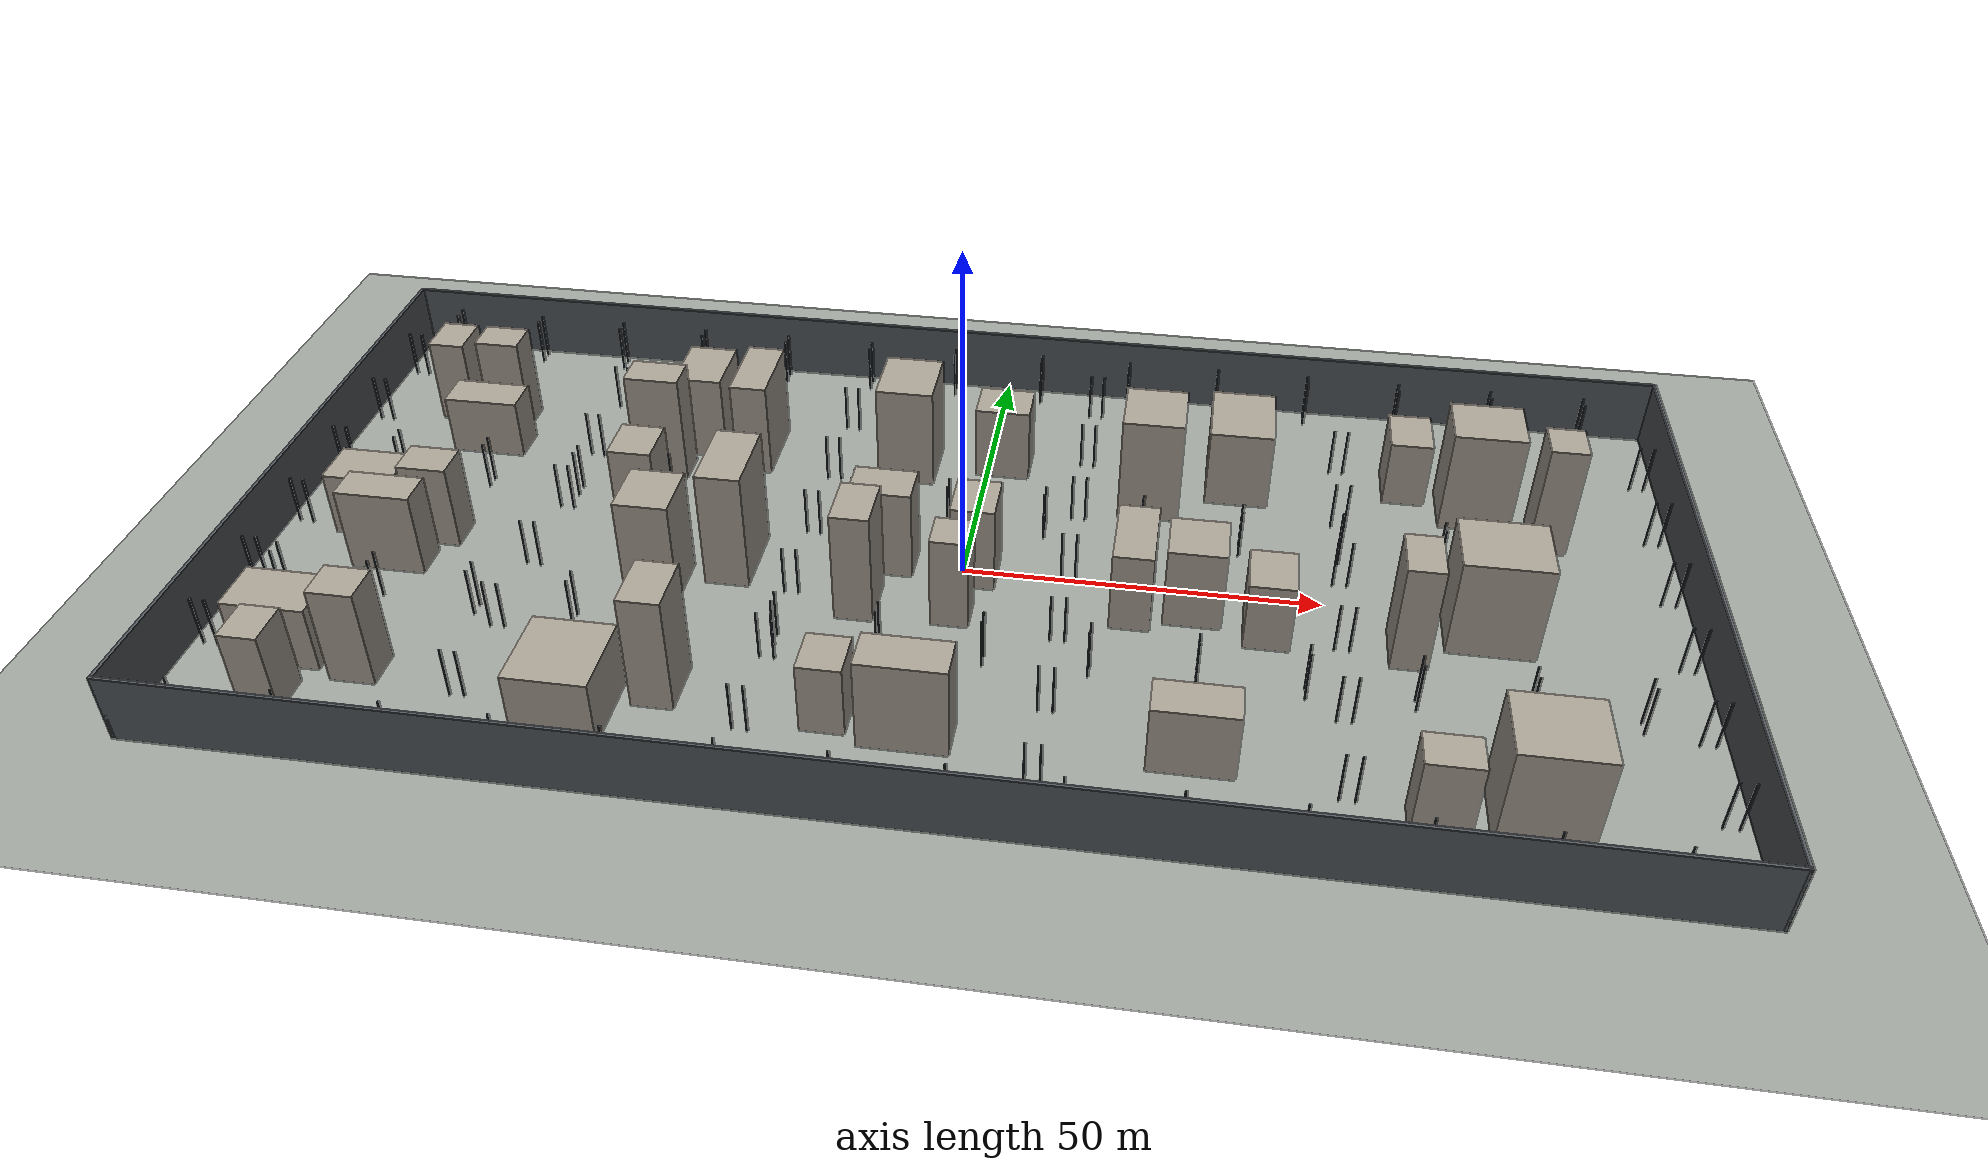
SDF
<sdf version="1.5">
 <world name="robocup_training_city_full_s7">
  <light type="directional" name="training_sun">
   <pose>0 0 30 0 0 0</pose>
   <diffuse>0.75 0.75 0.72 1</diffuse>
   <specular>0.12 0.12 0.12 1</specular>
   <direction>-0.4 0.3 -1</direction>
  </light>
  <model name="training_ground">
   <static>true</static>
   <link name="link">
    <collision name="collision">
     <geometry><plane><normal>0 0 1</normal><size>1000 1000</size></plane></geometry>
     <surface><friction><ode><mu>1</mu><mu2>1</mu2></ode></friction></surface>
    </collision>
    <visual name="visual">
     <geometry><plane><normal>0 0 1</normal><size>1000 1000</size></plane></geometry>
     <material>
      <ambient>0.279 0.288 0.279 1</ambient>
      <diffuse>0.62 0.64 0.62 1</diffuse>
      <specular>0.04 0.04 0.04 1</specular>
      <emissive>0 0 0 1</emissive>
     </material>
     <cast_shadows>false</cast_shadows>
    </visual>
   </link>
  </model>
  <model name="boundary_north">
   <static>true</static>
   <pose>0 49.75 0 0 0 0</pose>
   <link name="link">
    <pose>0 0 5 0 0 0</pose>
    <collision name="collision">
     <geometry><box><size>200 0.5 10</size></box></geometry>
     <surface><friction><ode><mu>1</mu><mu2>1</mu2></ode></friction></surface>
    </collision>
    <visual name="visual">
     <geometry><box><size>200 0.5 10</size></box></geometry>
     <material>
      <ambient>0.144 0.153 0.162 1</ambient>
      <diffuse>0.32 0.34 0.36 1</diffuse>
      <specular>0.04 0.04 0.04 1</specular>
      <emissive>0 0 0 1</emissive>
     </material>
    </visual>
    <inertial>
     <mass>1</mass>
     <inertia>
      <ixx>8.354167</ixx>
      <ixy>0</ixy>
      <ixz>0</ixz>
      <iyy>3341.666667</iyy>
      <iyz>0</iyz>
      <izz>3333.354167</izz>
     </inertia>
    </inertial>
   </link>
  </model>
  <model name="boundary_south">
   <static>true</static>
   <pose>0 -49.75 0 0 0 0</pose>
   <link name="link">
    <pose>0 0 5 0 0 0</pose>
    <collision name="collision">
     <geometry><box><size>200 0.5 10</size></box></geometry>
     <surface><friction><ode><mu>1</mu><mu2>1</mu2></ode></friction></surface>
    </collision>
    <visual name="visual">
     <geometry><box><size>200 0.5 10</size></box></geometry>
     <material>
      <ambient>0.144 0.153 0.162 1</ambient>
      <diffuse>0.32 0.34 0.36 1</diffuse>
      <specular>0.04 0.04 0.04 1</specular>
      <emissive>0 0 0 1</emissive>
     </material>
    </visual>
    <inertial>
     <mass>1</mass>
     <inertia>
      <ixx>8.354167</ixx>
      <ixy>0</ixy>
      <ixz>0</ixz>
      <iyy>3341.666667</iyy>
      <iyz>0</iyz>
      <izz>3333.354167</izz>
     </inertia>
    </inertial>
   </link>
  </model>
  <model name="boundary_east">
   <static>true</static>
   <pose>99.75 0 0 0 0 0</pose>
   <link name="link">
    <pose>0 0 5 0 0 0</pose>
    <collision name="collision">
     <geometry><box><size>0.5 100 10</size></box></geometry>
     <surface><friction><ode><mu>1</mu><mu2>1</mu2></ode></friction></surface>
    </collision>
    <visual name="visual">
     <geometry><box><size>0.5 100 10</size></box></geometry>
     <material>
      <ambient>0.144 0.153 0.162 1</ambient>
      <diffuse>0.32 0.34 0.36 1</diffuse>
      <specular>0.04 0.04 0.04 1</specular>
      <emissive>0 0 0 1</emissive>
     </material>
    </visual>
    <inertial>
     <mass>1</mass>
     <inertia>
      <ixx>841.666667</ixx>
      <ixy>0</ixy>
      <ixz>0</ixz>
      <iyy>8.354167</iyy>
      <iyz>0</iyz>
      <izz>833.354167</izz>
     </inertia>
    </inertial>
   </link>
  </model>
  <model name="boundary_west">
   <static>true</static>
   <pose>-99.75 0 0 0 0 0</pose>
   <link name="link">
    <pose>0 0 5 0 0 0</pose>
    <collision name="collision">
     <geometry><box><size>0.5 100 10</size></box></geometry>
     <surface><friction><ode><mu>1</mu><mu2>1</mu2></ode></friction></surface>
    </collision>
    <visual name="visual">
     <geometry><box><size>0.5 100 10</size></box></geometry>
     <material>
      <ambient>0.144 0.153 0.162 1</ambient>
      <diffuse>0.32 0.34 0.36 1</diffuse>
      <specular>0.04 0.04 0.04 1</specular>
      <emissive>0 0 0 1</emissive>
     </material>
    </visual>
    <inertial>
     <mass>1</mass>
     <inertia>
      <ixx>841.666667</ixx>
      <ixy>0</ixy>
      <ixz>0</ixz>
      <iyy>8.354167</iyy>
      <iyz>0</iyz>
      <izz>833.354167</izz>
     </inertia>
    </inertial>
   </link>
  </model>
  <model name="building_0001">
   <static>true</static>
   <pose>-85.959868 -29.937603 0 0 0 0</pose>
   <link name="link">
    <pose>0 0 4.923585 0 0 0</pose>
    <collision name="collision">
     <geometry><box><size>11.635058 7.763764 9.84717</size></box></geometry>
     <surface><friction><ode><mu>1</mu><mu2>1</mu2></ode></friction></surface>
    </collision>
    <visual name="visual">
     <geometry><box><size>11.635058 7.763764 9.84717</size></box></geometry>
     <material>
      <ambient>0.297 0.2835 0.261 1</ambient>
      <diffuse>0.66 0.63 0.58 1</diffuse>
      <specular>0.04 0.04 0.04 1</specular>
      <emissive>0 0 0 1</emissive>
     </material>
    </visual>
    <inertial>
     <mass>1</mass>
     <inertia>
      <ixx>13.103566</ixx>
      <ixy>0</ixy>
      <ixz>0</ixz>
      <iyy>19.361778</iyy>
      <iyz>0</iyz>
      <izz>16.304217</izz>
     </inertia>
    </inertial>
   </link>
  </model>
  <model name="building_0007">
   <static>true</static>
   <pose>-74.897354 -32.51899 0 0 0 0</pose>
   <link name="link">
    <pose>0 0 7.285543 0 0 0</pose>
    <collision name="collision">
     <geometry><box><size>6.315097 5.682014 14.571086</size></box></geometry>
     <surface><friction><ode><mu>1</mu><mu2>1</mu2></ode></friction></surface>
    </collision>
    <visual name="visual">
     <geometry><box><size>6.315097 5.682014 14.571086</size></box></geometry>
     <material>
      <ambient>0.297 0.2835 0.261 1</ambient>
      <diffuse>0.66 0.63 0.58 1</diffuse>
      <specular>0.04 0.04 0.04 1</specular>
      <emissive>0 0 0 1</emissive>
     </material>
    </visual>
    <inertial>
     <mass>1</mass>
     <inertia>
      <ixx>20.383486</ixx>
      <ixy>0</ixy>
      <ixz>0</ixz>
      <iyy>21.016416</iyy>
      <iyz>0</iyz>
      <izz>6.013811</izz>
     </inertia>
    </inertial>
   </link>
  </model>
  <model name="building_0083">
   <static>true</static>
   <pose>-84.11567 -39.307665 0 0 0 0</pose>
   <link name="link">
    <pose>0 0 6.138636 0 0 0</pose>
    <collision name="collision">
     <geometry><box><size>5.316662 6.297464 12.277272</size></box></geometry>
     <surface><friction><ode><mu>1</mu><mu2>1</mu2></ode></friction></surface>
    </collision>
    <visual name="visual">
     <geometry><box><size>5.316662 6.297464 12.277272</size></box></geometry>
     <material>
      <ambient>0.297 0.2835 0.261 1</ambient>
      <diffuse>0.66 0.63 0.58 1</diffuse>
      <specular>0.04 0.04 0.04 1</specular>
      <emissive>0 0 0 1</emissive>
     </material>
    </visual>
    <inertial>
     <mass>1</mass>
     <inertia>
      <ixx>15.865788</ixx>
      <ixy>0</ixy>
      <ixz>0</ixz>
      <iyy>14.916525</iyy>
      <iyz>0</iyz>
      <izz>5.660412</izz>
     </inertia>
    </inertial>
   </link>
  </model>
  <model name="building_0164">
   <static>true</static>
   <pose>-45.22436 -36.002927 0 0 0 0</pose>
   <link name="link">
    <pose>0 0 4.933902 0 0 0</pose>
    <collision name="collision">
     <geometry><box><size>11.184322 11.914767 9.867803</size></box></geometry>
     <surface><friction><ode><mu>1</mu><mu2>1</mu2></ode></friction></surface>
    </collision>
    <visual name="visual">
     <geometry><box><size>11.184322 11.914767 9.867803</size></box></geometry>
     <material>
      <ambient>0.297 0.2835 0.261 1</ambient>
      <diffuse>0.66 0.63 0.58 1</diffuse>
      <specular>0.04 0.04 0.04 1</specular>
      <emissive>0 0 0 1</emissive>
     </material>
    </visual>
    <inertial>
     <mass>1</mass>
     <inertia>
      <ixx>19.944601</ixx>
      <ixy>0</ixy>
      <ixz>0</ixz>
      <iyy>18.53855</iyy>
      <iyz>0</iyz>
      <izz>22.254228</izz>
     </inertia>
    </inertial>
   </link>
  </model>
  <model name="building_0171">
   <static>true</static>
   <pose>-34.935963 -29.924366 0 0 0 0</pose>
   <link name="link">
    <pose>0 0 8.61469 0 0 0</pose>
    <collision name="collision">
     <geometry><box><size>5.716327 8.323339 17.22938</size></box></geometry>
     <surface><friction><ode><mu>1</mu><mu2>1</mu2></ode></friction></surface>
    </collision>
    <visual name="visual">
     <geometry><box><size>5.716327 8.323339 17.22938</size></box></geometry>
     <material>
      <ambient>0.297 0.2835 0.261 1</ambient>
      <diffuse>0.66 0.63 0.58 1</diffuse>
      <specular>0.04 0.04 0.04 1</specular>
      <emissive>0 0 0 1</emissive>
     </material>
    </visual>
    <inertial>
     <mass>1</mass>
     <inertia>
      <ixx>30.510792</ixx>
      <ixy>0</ixy>
      <ixz>0</ixz>
      <iyy>27.460661</iyy>
      <iyz>0</iyz>
      <izz>8.496197</izz>
     </inertia>
    </inertial>
   </link>
  </model>
  <model name="building_0372">
   <static>true</static>
   <pose>-1.937773 -34.04671 0 0 0 0</pose>
   <link name="link">
    <pose>0 0 6.785066 0 0 0</pose>
    <collision name="collision">
     <geometry><box><size>11.849728 6.010458 13.570132</size></box></geometry>
     <surface><friction><ode><mu>1</mu><mu2>1</mu2></ode></friction></surface>
    </collision>
    <visual name="visual">
     <geometry><box><size>11.849728 6.010458 13.570132</size></box></geometry>
     <material>
      <ambient>0.297 0.2835 0.261 1</ambient>
      <diffuse>0.66 0.63 0.58 1</diffuse>
      <specular>0.04 0.04 0.04 1</specular>
      <emissive>0 0 0 1</emissive>
     </material>
    </visual>
    <inertial>
     <mass>1</mass>
     <inertia>
      <ixx>18.356174</ixx>
      <ixy>0</ixy>
      <ixz>0</ixz>
      <iyy>27.047045</iyy>
      <iyz>0</iyz>
      <izz>14.711805</izz>
     </inertia>
    </inertial>
   </link>
  </model>
  <model name="building_0386">
   <static>true</static>
   <pose>-12.499562 -31.948614 0 0 0 0</pose>
   <link name="link">
    <pose>0 0 5.255462 0 0 0</pose>
    <collision name="collision">
     <geometry><box><size>5.940601 6.704765 10.510924</size></box></geometry>
     <surface><friction><ode><mu>1</mu><mu2>1</mu2></ode></friction></surface>
    </collision>
    <visual name="visual">
     <geometry><box><size>5.940601 6.704765 10.510924</size></box></geometry>
     <material>
      <ambient>0.297 0.2835 0.261 1</ambient>
      <diffuse>0.66 0.63 0.58 1</diffuse>
      <specular>0.04 0.04 0.04 1</specular>
      <emissive>0 0 0 1</emissive>
     </material>
    </visual>
    <inertial>
     <mass>1</mass>
     <inertia>
      <ixx>12.952783</ixx>
      <ixy>0</ixy>
      <ixz>0</ixz>
      <iyy>12.147522</iyy>
      <iyz>0</iyz>
      <izz>6.687051</izz>
     </inertia>
    </inertial>
   </link>
  </model>
  <model name="building_0667">
   <static>true</static>
   <pose>33.540204 -32.883003 0 0 0 0</pose>
   <link name="link">
    <pose>0 0 5.029122 0 0 0</pose>
    <collision name="collision">
     <geometry><box><size>11.153431 5.819497 10.058244</size></box></geometry>
     <surface><friction><ode><mu>1</mu><mu2>1</mu2></ode></friction></surface>
    </collision>
    <visual name="visual">
     <geometry><box><size>11.153431 5.819497 10.058244</size></box></geometry>
     <material>
      <ambient>0.297 0.2835 0.261 1</ambient>
      <diffuse>0.66 0.63 0.58 1</diffuse>
      <specular>0.04 0.04 0.04 1</specular>
      <emissive>0 0 0 1</emissive>
     </material>
    </visual>
    <inertial>
     <mass>1</mass>
     <inertia>
      <ixx>11.252901</ixx>
      <ixy>0</ixy>
      <ixz>0</ixz>
      <iyy>18.797275</iyy>
      <iyz>0</iyz>
      <izz>13.188797</izz>
     </inertia>
    </inertial>
   </link>
  </model>
  <model name="building_0788">
   <static>true</static>
   <pose>74.495542 -36.841006 0 0 0 0</pose>
   <link name="link">
    <pose>0 0 7.563883 0 0 0</pose>
    <collision name="collision">
     <geometry><box><size>11.390095 10.860317 15.127766</size></box></geometry>
     <surface><friction><ode><mu>1</mu><mu2>1</mu2></ode></friction></surface>
    </collision>
    <visual name="visual">
     <geometry><box><size>11.390095 10.860317 15.127766</size></box></geometry>
     <material>
      <ambient>0.297 0.2835 0.261 1</ambient>
      <diffuse>0.66 0.63 0.58 1</diffuse>
      <specular>0.04 0.04 0.04 1</specular>
      <emissive>0 0 0 1</emissive>
     </material>
    </visual>
    <inertial>
     <mass>1</mass>
     <inertia>
      <ixx>28.899649</ixx>
      <ixy>0</ixy>
      <ixz>0</ixz>
      <iyy>29.881964</iyy>
      <iyz>0</iyz>
      <izz>20.640062</izz>
     </inertia>
    </inertial>
   </link>
  </model>
  <model name="building_0804">
   <static>true</static>
   <pose>62.766601 -39.588882 0 0 0 0</pose>
   <link name="link">
    <pose>0 0 6.126754 0 0 0</pose>
    <collision name="collision">
     <geometry><box><size>7.127302 5.447589 12.253508</size></box></geometry>
     <surface><friction><ode><mu>1</mu><mu2>1</mu2></ode></friction></surface>
    </collision>
    <visual name="visual">
     <geometry><box><size>7.127302 5.447589 12.253508</size></box></geometry>
     <material>
      <ambient>0.297 0.2835 0.261 1</ambient>
      <diffuse>0.66 0.63 0.58 1</diffuse>
      <specular>0.04 0.04 0.04 1</specular>
      <emissive>0 0 0 1</emissive>
     </material>
    </visual>
    <inertial>
     <mass>1</mass>
     <inertia>
      <ixx>14.98539</ixx>
      <ixy>0</ixy>
      <ixz>0</ixz>
      <iyy>16.745574</iyy>
      <iyz>0</iyz>
      <izz>6.706222</izz>
     </inertia>
    </inertial>
   </link>
  </model>
  <model name="building_0885">
   <static>true</static>
   <pose>-76.112356 -2.415043 0 0 0 0</pose>
   <link name="link">
    <pose>0 0 6.467856 0 0 0</pose>
    <collision name="collision">
     <geometry><box><size>7.175386 5.524574 12.935713</size></box></geometry>
     <surface><friction><ode><mu>1</mu><mu2>1</mu2></ode></friction></surface>
    </collision>
    <visual name="visual">
     <geometry><box><size>7.175386 5.524574 12.935713</size></box></geometry>
     <material>
      <ambient>0.297 0.2835 0.261 1</ambient>
      <diffuse>0.66 0.63 0.58 1</diffuse>
      <specular>0.04 0.04 0.04 1</specular>
      <emissive>0 0 0 1</emissive>
     </material>
    </visual>
    <inertial>
     <mass>1</mass>
     <inertia>
      <ixx>16.487799</ixx>
      <ixy>0</ixy>
      <ixz>0</ixz>
      <iyy>18.234903</iyy>
      <iyz>0</iyz>
      <izz>6.833924</izz>
     </inertia>
    </inertial>
   </link>
  </model>
  <model name="building_0888">
   <static>true</static>
   <pose>-86.619784 -1.004219 0 0 0 0</pose>
   <link name="link">
    <pose>0 0 4.895372 0 0 0</pose>
    <collision name="collision">
     <geometry><box><size>10.072908 7.202734 9.790745</size></box></geometry>
     <surface><friction><ode><mu>1</mu><mu2>1</mu2></ode></friction></surface>
    </collision>
    <visual name="visual">
     <geometry><box><size>10.072908 7.202734 9.790745</size></box></geometry>
     <material>
      <ambient>0.297 0.2835 0.261 1</ambient>
      <diffuse>0.66 0.63 0.58 1</diffuse>
      <specular>0.04 0.04 0.04 1</specular>
      <emissive>0 0 0 1</emissive>
     </material>
    </visual>
    <inertial>
     <mass>1</mass>
     <inertia>
      <ixx>12.311505</ixx>
      <ixy>0</ixy>
      <ixz>0</ixz>
      <iyy>16.443514</iyy>
      <iyz>0</iyz>
      <izz>12.778571</izz>
     </inertia>
    </inertial>
   </link>
  </model>
  <model name="building_0978">
   <static>true</static>
   <pose>-80.336144 -9.429474 0 0 0 0</pose>
   <link name="link">
    <pose>0 0 6.364518 0 0 0</pose>
    <collision name="collision">
     <geometry><box><size>10.800505 5.325004 12.729036</size></box></geometry>
     <surface><friction><ode><mu>1</mu><mu2>1</mu2></ode></friction></surface>
    </collision>
    <visual name="visual">
     <geometry><box><size>10.800505 5.325004 12.729036</size></box></geometry>
     <material>
      <ambient>0.297 0.2835 0.261 1</ambient>
      <diffuse>0.66 0.63 0.58 1</diffuse>
      <specular>0.04 0.04 0.04 1</specular>
      <emissive>0 0 0 1</emissive>
     </material>
    </visual>
    <inertial>
     <mass>1</mass>
     <inertia>
      <ixx>15.865335</ixx>
      <ixy>0</ixy>
      <ixz>0</ixz>
      <iyy>23.223272</iyy>
      <iyz>0</iyz>
      <izz>12.083881</izz>
     </inertia>
    </inertial>
   </link>
  </model>
  <model name="building_1099">
   <static>true</static>
   <pose>-46.131788 0.74101 0 0 0 0</pose>
   <link name="link">
    <pose>0 0 8.57422 0 0 0</pose>
    <collision name="collision">
     <geometry><box><size>6.117776 7.048076 17.148441</size></box></geometry>
     <surface><friction><ode><mu>1</mu><mu2>1</mu2></ode></friction></surface>
    </collision>
    <visual name="visual">
     <geometry><box><size>6.117776 7.048076 17.148441</size></box></geometry>
     <material>
      <ambient>0.297 0.2835 0.261 1</ambient>
      <diffuse>0.66 0.63 0.58 1</diffuse>
      <specular>0.04 0.04 0.04 1</specular>
      <emissive>0 0 0 1</emissive>
     </material>
    </visual>
    <inertial>
     <mass>1</mass>
     <inertia>
      <ixx>28.645367</ixx>
      <ixy>0</ixy>
      <ixz>0</ixz>
      <iyy>27.624684</iyy>
      <iyz>0</iyz>
      <izz>7.258547</izz>
     </inertia>
    </inertial>
   </link>
  </model>
  <model name="building_1106">
   <static>true</static>
   <pose>-41.575823 -8.622747 0 0 0 0</pose>
   <link name="link">
    <pose>0 0 7.890977 0 0 0</pose>
    <collision name="collision">
     <geometry><box><size>7.577471 8.568934 15.781954</size></box></geometry>
     <surface><friction><ode><mu>1</mu><mu2>1</mu2></ode></friction></surface>
    </collision>
    <visual name="visual">
     <geometry><box><size>7.577471 8.568934 15.781954</size></box></geometry>
     <material>
      <ambient>0.297 0.2835 0.261 1</ambient>
      <diffuse>0.66 0.63 0.58 1</diffuse>
      <specular>0.04 0.04 0.04 1</specular>
      <emissive>0 0 0 1</emissive>
     </material>
    </visual>
    <inertial>
     <mass>1</mass>
     <inertia>
      <ixx>26.874725</ixx>
      <ixy>0</ixy>
      <ixz>0</ixz>
      <iyy>25.540678</iyy>
      <iyz>0</iyz>
      <izz>10.903725</izz>
     </inertia>
    </inertial>
   </link>
  </model>
  <model name="building_1167">
   <static>true</static>
   <pose>-32.17039 -2.144799 0 0 0 0</pose>
   <link name="link">
    <pose>0 0 8.966534 0 0 0</pose>
    <collision name="collision">
     <geometry><box><size>6.315448 11.645999 17.933069</size></box></geometry>
     <surface><friction><ode><mu>1</mu><mu2>1</mu2></ode></friction></surface>
    </collision>
    <visual name="visual">
     <geometry><box><size>6.315448 11.645999 17.933069</size></box></geometry>
     <material>
      <ambient>0.297 0.2835 0.261 1</ambient>
      <diffuse>0.66 0.63 0.58 1</diffuse>
      <specular>0.04 0.04 0.04 1</specular>
      <emissive>0 0 0 1</emissive>
     </material>
    </visual>
    <inertial>
     <mass>1</mass>
     <inertia>
      <ixx>38.102021</ixx>
      <ixy>0</ixy>
      <ixz>0</ixz>
      <iyy>30.123321</iyy>
      <iyz>0</iyz>
      <izz>14.626181</izz>
     </inertia>
    </inertial>
   </link>
  </model>
  <model name="building_1168">
   <static>true</static>
   <pose>-0.093679 -9.409852 0 0 0 0</pose>
   <link name="link">
    <pose>0 0 7.013082 0 0 0</pose>
    <collision name="collision">
     <geometry><box><size>5.256418 5.571161 14.026164</size></box></geometry>
     <surface><friction><ode><mu>1</mu><mu2>1</mu2></ode></friction></surface>
    </collision>
    <visual name="visual">
     <geometry><box><size>5.256418 5.571161 14.026164</size></box></geometry>
     <material>
      <ambient>0.297 0.2835 0.261 1</ambient>
      <diffuse>0.66 0.63 0.58 1</diffuse>
      <specular>0.04 0.04 0.04 1</specular>
      <emissive>0 0 0 1</emissive>
     </material>
    </visual>
    <inertial>
     <mass>1</mass>
     <inertia>
      <ixx>18.980926</ixx>
      <ixy>0</ixy>
      <ixz>0</ixz>
      <iyy>18.696934</iyy>
      <iyz>0</iyz>
      <izz>4.88898</izz>
     </inertia>
    </inertial>
   </link>
  </model>
  <model name="building_1169">
   <static>true</static>
   <pose>1.740974 0.241653 0 0 0 0</pose>
   <link name="link">
    <pose>0 0 6.566435 0 0 0</pose>
    <collision name="collision">
     <geometry><box><size>6.207201 7.51585 13.132871</size></box></geometry>
     <surface><friction><ode><mu>1</mu><mu2>1</mu2></ode></friction></surface>
    </collision>
    <visual name="visual">
     <geometry><box><size>6.207201 7.51585 13.132871</size></box></geometry>
     <material>
      <ambient>0.297 0.2835 0.261 1</ambient>
      <diffuse>0.66 0.63 0.58 1</diffuse>
      <specular>0.04 0.04 0.04 1</specular>
      <emissive>0 0 0 1</emissive>
     </material>
    </visual>
    <inertial>
     <mass>1</mass>
     <inertia>
      <ixx>19.080025</ixx>
      <ixy>0</ixy>
      <ixz>0</ixz>
      <iyy>17.58347</iyy>
      <iyz>0</iyz>
      <izz>7.918112</izz>
     </inertia>
    </inertial>
   </link>
  </model>
  <model name="building_1171">
   <static>true</static>
   <pose>-11.314388 0.743348 0 0 0 0</pose>
   <link name="link">
    <pose>0 0 6.885413 0 0 0</pose>
    <collision name="collision">
     <geometry><box><size>8.821256 6.237443 13.770826</size></box></geometry>
     <surface><friction><ode><mu>1</mu><mu2>1</mu2></ode></friction></surface>
    </collision>
    <visual name="visual">
     <geometry><box><size>8.821256 6.237443 13.770826</size></box></geometry>
     <material>
      <ambient>0.297 0.2835 0.261 1</ambient>
      <diffuse>0.66 0.63 0.58 1</diffuse>
      <specular>0.04 0.04 0.04 1</specular>
      <emissive>0 0 0 1</emissive>
     </material>
    </visual>
    <inertial>
     <mass>1</mass>
     <inertia>
      <ixx>19.045112</ixx>
      <ixy>0</ixy>
      <ixz>0</ixz>
      <iyy>22.287517</iyy>
      <iyz>0</iyz>
      <izz>9.726688</izz>
     </inertia>
    </inertial>
   </link>
  </model>
  <model name="building_1189">
   <static>true</static>
   <pose>-13.171839 -8.790246 0 0 0 0</pose>
   <link name="link">
    <pose>0 0 8.476714 0 0 0</pose>
    <collision name="collision">
     <geometry><box><size>5.405041 8.122158 16.953428</size></box></geometry>
     <surface><friction><ode><mu>1</mu><mu2>1</mu2></ode></friction></surface>
    </collision>
    <visual name="visual">
     <geometry><box><size>5.405041 8.122158 16.953428</size></box></geometry>
     <material>
      <ambient>0.297 0.2835 0.261 1</ambient>
      <diffuse>0.66 0.63 0.58 1</diffuse>
      <specular>0.04 0.04 0.04 1</specular>
      <emissive>0 0 0 1</emissive>
     </material>
    </visual>
    <inertial>
     <mass>1</mass>
     <inertia>
      <ixx>29.449014</ixx>
      <ixy>0</ixy>
      <ixz>0</ixz>
      <iyy>26.386099</iyy>
      <iyz>0</iyz>
      <izz>7.931993</izz>
     </inertia>
    </inertial>
   </link>
  </model>
  <model name="building_1310">
   <static>true</static>
   <pose>32.338999 -3.36674 0 0 0 0</pose>
   <link name="link">
    <pose>0 0 6.127701 0 0 0</pose>
    <collision name="collision">
     <geometry><box><size>7.981018 7.94929 12.255402</size></box></geometry>
     <surface><friction><ode><mu>1</mu><mu2>1</mu2></ode></friction></surface>
    </collision>
    <visual name="visual">
     <geometry><box><size>7.981018 7.94929 12.255402</size></box></geometry>
     <material>
      <ambient>0.297 0.2835 0.261 1</ambient>
      <diffuse>0.66 0.63 0.58 1</diffuse>
      <specular>0.04 0.04 0.04 1</specular>
      <emissive>0 0 0 1</emissive>
     </material>
    </visual>
    <inertial>
     <mass>1</mass>
     <inertia>
      <ixx>17.782174</ixx>
      <ixy>0</ixy>
      <ixz>0</ixz>
      <iyy>17.824294</iyy>
      <iyz>0</iyz>
      <izz>10.573988</izz>
     </inertia>
    </inertial>
   </link>
  </model>
  <model name="building_1344">
   <static>true</static>
   <pose>24.014528 -3.276209 0 0 0 0</pose>
   <link name="link">
    <pose>0 0 6.074657 0 0 0</pose>
    <collision name="collision">
     <geometry><box><size>5.6072 11.893481 12.149315</size></box></geometry>
     <surface><friction><ode><mu>1</mu><mu2>1</mu2></ode></friction></surface>
    </collision>
    <visual name="visual">
     <geometry><box><size>5.6072 11.893481 12.149315</size></box></geometry>
     <material>
      <ambient>0.297 0.2835 0.261 1</ambient>
      <diffuse>0.66 0.63 0.58 1</diffuse>
      <specular>0.04 0.04 0.04 1</specular>
      <emissive>0 0 0 1</emissive>
     </material>
    </visual>
    <inertial>
     <mass>1</mass>
     <inertia>
      <ixx>24.088395</ixx>
      <ixy>0</ixy>
      <ixz>0</ixz>
      <iyy>14.920546</iyy>
      <iyz>0</iyz>
      <izz>14.407965</izz>
     </inertia>
    </inertial>
   </link>
  </model>
  <model name="building_1345">
   <static>true</static>
   <pose>42.341442 -6.593479 0 0 0 0</pose>
   <link name="link">
    <pose>0 0 5.240731 0 0 0</pose>
    <collision name="collision">
     <geometry><box><size>6.306943 8.052039 10.481462</size></box></geometry>
     <surface><friction><ode><mu>1</mu><mu2>1</mu2></ode></friction></surface>
    </collision>
    <visual name="visual">
     <geometry><box><size>6.306943 8.052039 10.481462</size></box></geometry>
     <material>
      <ambient>0.297 0.2835 0.261 1</ambient>
      <diffuse>0.66 0.63 0.58 1</diffuse>
      <specular>0.04 0.04 0.04 1</specular>
      <emissive>0 0 0 1</emissive>
     </material>
    </visual>
    <inertial>
     <mass>1</mass>
     <inertia>
      <ixx>14.558031</ixx>
      <ixy>0</ixy>
      <ixz>0</ixz>
      <iyy>12.469881</iyy>
      <iyz>0</iyz>
      <izz>8.717739</izz>
     </inertia>
    </inertial>
   </link>
  </model>
  <model name="building_1466">
   <static>true</static>
   <pose>71.767844 -2.276803 0 0 0 0</pose>
   <link name="link">
    <pose>0 0 7.371707 0 0 0</pose>
    <collision name="collision">
     <geometry><box><size>11.913461 10.386935 14.743413</size></box></geometry>
     <surface><friction><ode><mu>1</mu><mu2>1</mu2></ode></friction></surface>
    </collision>
    <visual name="visual">
     <geometry><box><size>11.913461 10.386935 14.743413</size></box></geometry>
     <material>
      <ambient>0.297 0.2835 0.261 1</ambient>
      <diffuse>0.66 0.63 0.58 1</diffuse>
      <specular>0.04 0.04 0.04 1</specular>
      <emissive>0 0 0 1</emissive>
     </material>
    </visual>
    <inertial>
     <mass>1</mass>
     <inertia>
      <ixx>27.10472</ixx>
      <ixy>0</ixy>
      <ixz>0</ixz>
      <iyy>29.941565</iyy>
      <iyz>0</iyz>
      <izz>20.818248</izz>
     </inertia>
    </inertial>
   </link>
  </model>
  <model name="building_1717">
   <static>true</static>
   <pose>60.892966 -7.826447 0 0 0 0</pose>
   <link name="link">
    <pose>0 0 8.139301 0 0 0</pose>
    <collision name="collision">
     <geometry><box><size>5.001045 7.930526 16.278602</size></box></geometry>
     <surface><friction><ode><mu>1</mu><mu2>1</mu2></ode></friction></surface>
    </collision>
    <visual name="visual">
     <geometry><box><size>5.001045 7.930526 16.278602</size></box></geometry>
     <material>
      <ambient>0.297 0.2835 0.261 1</ambient>
      <diffuse>0.66 0.63 0.58 1</diffuse>
      <specular>0.04 0.04 0.04 1</specular>
      <emissive>0 0 0 1</emissive>
     </material>
    </visual>
    <inertial>
     <mass>1</mass>
     <inertia>
      <ixx>27.323844</ixx>
      <ixy>0</ixy>
      <ixz>0</ixz>
      <iyy>24.166945</iyy>
      <iyz>0</iyz>
      <izz>7.325308</izz>
     </inertia>
    </inertial>
   </link>
  </model>
  <model name="building_1758">
   <static>true</static>
   <pose>-77.383457 21.271482 0 0 0 0</pose>
   <link name="link">
    <pose>0 0 4.608681 0 0 0</pose>
    <collision name="collision">
     <geometry><box><size>11.187578 5.742838 9.217361</size></box></geometry>
     <surface><friction><ode><mu>1</mu><mu2>1</mu2></ode></friction></surface>
    </collision>
    <visual name="visual">
     <geometry><box><size>11.187578 5.742838 9.217361</size></box></geometry>
     <material>
      <ambient>0.297 0.2835 0.261 1</ambient>
      <diffuse>0.66 0.63 0.58 1</diffuse>
      <specular>0.04 0.04 0.04 1</specular>
      <emissive>0 0 0 1</emissive>
     </material>
    </visual>
    <inertial>
     <mass>1</mass>
     <inertia>
      <ixx>9.828328</ixx>
      <ixy>0</ixy>
      <ixz>0</ixz>
      <iyy>17.510137</iyy>
      <iyz>0</iyz>
      <izz>13.178507</izz>
     </inertia>
    </inertial>
   </link>
  </model>
  <model name="building_1759">
   <static>true</static>
   <pose>-85.654073 30.366753 0 0 0 0</pose>
   <link name="link">
    <pose>0 0 6.721108 0 0 0</pose>
    <collision name="collision">
     <geometry><box><size>5.421987 6.764938 13.442216</size></box></geometry>
     <surface><friction><ode><mu>1</mu><mu2>1</mu2></ode></friction></surface>
    </collision>
    <visual name="visual">
     <geometry><box><size>5.421987 6.764938 13.442216</size></box></geometry>
     <material>
      <ambient>0.297 0.2835 0.261 1</ambient>
      <diffuse>0.66 0.63 0.58 1</diffuse>
      <specular>0.04 0.04 0.04 1</specular>
      <emissive>0 0 0 1</emissive>
     </material>
    </visual>
    <inertial>
     <mass>1</mass>
     <inertia>
      <ixx>18.871463</ixx>
      <ixy>0</ixy>
      <ixz>0</ixz>
      <iyy>17.507593</iyy>
      <iyz>0</iyz>
      <izz>6.263527</izz>
     </inertia>
    </inertial>
   </link>
  </model>
  <model name="building_1816">
   <static>true</static>
   <pose>-76.895274 28.776513 0 0 0 0</pose>
   <link name="link">
    <pose>0 0 7.425723 0 0 0</pose>
    <collision name="collision">
     <geometry><box><size>6.668007 5.290109 14.851446</size></box></geometry>
     <surface><friction><ode><mu>1</mu><mu2>1</mu2></ode></friction></surface>
    </collision>
    <visual name="visual">
     <geometry><box><size>6.668007 5.290109 14.851446</size></box></geometry>
     <material>
      <ambient>0.297 0.2835 0.261 1</ambient>
      <diffuse>0.66 0.63 0.58 1</diffuse>
      <specular>0.04 0.04 0.04 1</specular>
      <emissive>0 0 0 1</emissive>
     </material>
    </visual>
    <inertial>
     <mass>1</mass>
     <inertia>
      <ixx>20.712558</ixx>
      <ixy>0</ixy>
      <ixz>0</ixz>
      <iyy>22.085647</iyy>
      <iyz>0</iyz>
      <izz>6.037298</izz>
     </inertia>
    </inertial>
   </link>
  </model>
  <model name="building_1817">
   <static>true</static>
   <pose>-44.141686 27.758621 0 0 0 0</pose>
   <link name="link">
    <pose>0 0 6.721155 0 0 0</pose>
    <collision name="collision">
     <geometry><box><size>7.105225 9.745285 13.44231</size></box></geometry>
     <surface><friction><ode><mu>1</mu><mu2>1</mu2></ode></friction></surface>
    </collision>
    <visual name="visual">
     <geometry><box><size>7.105225 9.745285 13.44231</size></box></geometry>
     <material>
      <ambient>0.297 0.2835 0.261 1</ambient>
      <diffuse>0.66 0.63 0.58 1</diffuse>
      <specular>0.04 0.04 0.04 1</specular>
      <emissive>0 0 0 1</emissive>
     </material>
    </visual>
    <inertial>
     <mass>1</mass>
     <inertia>
      <ixx>22.97219</ixx>
      <ixy>0</ixy>
      <ixz>0</ixz>
      <iyy>19.264993</iyy>
      <iyz>0</iyz>
      <izz>12.121234</izz>
     </inertia>
    </inertial>
   </link>
  </model>
  <model name="building_1822">
   <static>true</static>
   <pose>-35.446435 25.714378 0 0 0 0</pose>
   <link name="link">
    <pose>0 0 7.390036 0 0 0</pose>
    <collision name="collision">
     <geometry><box><size>5.424396 11.925101 14.780072</size></box></geometry>
     <surface><friction><ode><mu>1</mu><mu2>1</mu2></ode></friction></surface>
    </collision>
    <visual name="visual">
     <geometry><box><size>5.424396 11.925101 14.780072</size></box></geometry>
     <material>
      <ambient>0.297 0.2835 0.261 1</ambient>
      <diffuse>0.66 0.63 0.58 1</diffuse>
      <specular>0.04 0.04 0.04 1</specular>
      <emissive>0 0 0 1</emissive>
     </material>
    </visual>
    <inertial>
     <mass>1</mass>
     <inertia>
      <ixx>30.05488</ixx>
      <ixy>0</ixy>
      <ixz>0</ixz>
      <iyy>20.656217</iyy>
      <iyz>0</iyz>
      <izz>14.302675</izz>
     </inertia>
    </inertial>
   </link>
  </model>
  <model name="building_1956">
   <static>true</static>
   <pose>-48.94655 18.779457 0 0 0 0</pose>
   <link name="link">
    <pose>0 0 8.530868 0 0 0</pose>
    <collision name="collision">
     <geometry><box><size>8.090095 5.209719 17.061736</size></box></geometry>
     <surface><friction><ode><mu>1</mu><mu2>1</mu2></ode></friction></surface>
    </collision>
    <visual name="visual">
     <geometry><box><size>8.090095 5.209719 17.061736</size></box></geometry>
     <material>
      <ambient>0.297 0.2835 0.261 1</ambient>
      <diffuse>0.66 0.63 0.58 1</diffuse>
      <specular>0.04 0.04 0.04 1</specular>
      <emissive>0 0 0 1</emissive>
     </material>
    </visual>
    <inertial>
     <mass>1</mass>
     <inertia>
      <ixx>26.520334</ixx>
      <ixy>0</ixy>
      <ixz>0</ixz>
      <iyy>29.712706</iyy>
      <iyz>0</iyz>
      <izz>7.715901</izz>
     </inertia>
    </inertial>
   </link>
  </model>
  <model name="building_1957">
   <static>true</static>
   <pose>-12.010483 25.467943 0 0 0 0</pose>
   <link name="link">
    <pose>0 0 7.846728 0 0 0</pose>
    <collision name="collision">
     <geometry><box><size>8.430052 9.921129 15.693456</size></box></geometry>
     <surface><friction><ode><mu>1</mu><mu2>1</mu2></ode></friction></surface>
    </collision>
    <visual name="visual">
     <geometry><box><size>8.430052 9.921129 15.693456</size></box></geometry>
     <material>
      <ambient>0.297 0.2835 0.261 1</ambient>
      <diffuse>0.66 0.63 0.58 1</diffuse>
      <specular>0.04 0.04 0.04 1</specular>
      <emissive>0 0 0 1</emissive>
     </material>
    </visual>
    <inertial>
     <mass>1</mass>
     <inertia>
      <ixx>28.726113</ixx>
      <ixy>0</ixy>
      <ixz>0</ixz>
      <iyy>26.445861</iyy>
      <iyz>0</iyz>
      <izz>14.124548</izz>
     </inertia>
    </inertial>
   </link>
  </model>
  <model name="building_1959">
   <static>true</static>
   <pose>2.16664 27.384567 0 0 0 0</pose>
   <link name="link">
    <pose>0 0 5.76333 0 0 0</pose>
    <collision name="collision">
     <geometry><box><size>8.048123 6.629066 11.526659</size></box></geometry>
     <surface><friction><ode><mu>1</mu><mu2>1</mu2></ode></friction></surface>
    </collision>
    <visual name="visual">
     <geometry><box><size>8.048123 6.629066 11.526659</size></box></geometry>
     <material>
      <ambient>0.297 0.2835 0.261 1</ambient>
      <diffuse>0.66 0.63 0.58 1</diffuse>
      <specular>0.04 0.04 0.04 1</specular>
      <emissive>0 0 0 1</emissive>
     </material>
    </visual>
    <inertial>
     <mass>1</mass>
     <inertia>
      <ixx>14.734032</ixx>
      <ixy>0</ixy>
      <ixz>0</ixz>
      <iyy>16.469679</iyy>
      <iyz>0</iyz>
      <izz>9.059733</izz>
     </inertia>
    </inertial>
   </link>
  </model>
  <model name="building_2040">
   <static>true</static>
   <pose>24.751277 21.360362 0 0 0 0</pose>
   <link name="link">
    <pose>0 0 8.185209 0 0 0</pose>
    <collision name="collision">
     <geometry><box><size>8.853988 9.58888 16.370419</size></box></geometry>
     <surface><friction><ode><mu>1</mu><mu2>1</mu2></ode></friction></surface>
    </collision>
    <visual name="visual">
     <geometry><box><size>8.853988 9.58888 16.370419</size></box></geometry>
     <material>
      <ambient>0.297 0.2835 0.261 1</ambient>
      <diffuse>0.66 0.63 0.58 1</diffuse>
      <specular>0.04 0.04 0.04 1</specular>
      <emissive>0 0 0 1</emissive>
     </material>
    </visual>
    <inertial>
     <mass>1</mass>
     <inertia>
      <ixx>29.99477</ixx>
      <ixy>0</ixy>
      <ixz>0</ixz>
      <iyy>28.86531</iyy>
      <iyz>0</iyz>
      <izz>14.194977</izz>
     </inertia>
    </inertial>
   </link>
  </model>
  <model name="building_2043">
   <static>true</static>
   <pose>37.455269 28.03509 0 0 0 0</pose>
   <link name="link">
    <pose>0 0 6.081235 0 0 0</pose>
    <collision name="collision">
     <geometry><box><size>9.21264 11.802354 12.16247</size></box></geometry>
     <surface><friction><ode><mu>1</mu><mu2>1</mu2></ode></friction></surface>
    </collision>
    <visual name="visual">
     <geometry><box><size>9.21264 11.802354 12.16247</size></box></geometry>
     <material>
      <ambient>0.297 0.2835 0.261 1</ambient>
      <diffuse>0.66 0.63 0.58 1</diffuse>
      <specular>0.04 0.04 0.04 1</specular>
      <emissive>0 0 0 1</emissive>
     </material>
    </visual>
    <inertial>
     <mass>1</mass>
     <inertia>
      <ixx>23.935103</ixx>
      <ixy>0</ixy>
      <ixz>0</ixz>
      <iyy>19.399868</iyy>
      <iyz>0</iyz>
      <izz>18.680691</izz>
     </inertia>
    </inertial>
   </link>
  </model>
  <model name="building_2324">
   <static>true</static>
   <pose>71.866077 25.630236 0 0 0 0</pose>
   <link name="link">
    <pose>0 0 7.895653 0 0 0</pose>
    <collision name="collision">
     <geometry><box><size>10.213127 8.963937 15.791307</size></box></geometry>
     <surface><friction><ode><mu>1</mu><mu2>1</mu2></ode></friction></surface>
    </collision>
    <visual name="visual">
     <geometry><box><size>10.213127 8.963937 15.791307</size></box></geometry>
     <material>
      <ambient>0.297 0.2835 0.261 1</ambient>
      <diffuse>0.66 0.63 0.58 1</diffuse>
      <specular>0.04 0.04 0.04 1</specular>
      <emissive>0 0 0 1</emissive>
     </material>
    </visual>
    <inertial>
     <mass>1</mass>
     <inertia>
      <ixx>27.476462</ixx>
      <ixy>0</ixy>
      <ixz>0</ixz>
      <iyy>29.472778</iyy>
      <iyz>0</iyz>
      <izz>15.388344</izz>
     </inertia>
    </inertial>
   </link>
  </model>
  <model name="building_2450">
   <static>true</static>
   <pose>62.026288 30.303946 0 0 0 0</pose>
   <link name="link">
    <pose>0 0 5.142759 0 0 0</pose>
    <collision name="collision">
     <geometry><box><size>6.104244 8.189022 10.285517</size></box></geometry>
     <surface><friction><ode><mu>1</mu><mu2>1</mu2></ode></friction></surface>
    </collision>
    <visual name="visual">
     <geometry><box><size>6.104244 8.189022 10.285517</size></box></geometry>
     <material>
      <ambient>0.297 0.2835 0.261 1</ambient>
      <diffuse>0.66 0.63 0.58 1</diffuse>
      <specular>0.04 0.04 0.04 1</specular>
      <emissive>0 0 0 1</emissive>
     </material>
    </visual>
    <inertial>
     <mass>1</mass>
     <inertia>
      <ixx>14.404328</ixx>
      <ixy>0</ixy>
      <ixz>0</ixz>
      <iyy>11.921138</iyy>
      <iyz>0</iyz>
      <izz>8.69349</izz>
     </inertia>
    </inertial>
   </link>
  </model>
  <model name="building_2464">
   <static>true</static>
   <pose>81.738285 19.941969 0 0 0 0</pose>
   <link name="link">
    <pose>0 0 8.679304 0 0 0</pose>
    <collision name="collision">
     <geometry><box><size>5.261979 6.129536 17.358608</size></box></geometry>
     <surface><friction><ode><mu>1</mu><mu2>1</mu2></ode></friction></surface>
    </collision>
    <visual name="visual">
     <geometry><box><size>5.261979 6.129536 17.358608</size></box></geometry>
     <material>
      <ambient>0.297 0.2835 0.261 1</ambient>
      <diffuse>0.66 0.63 0.58 1</diffuse>
      <specular>0.04 0.04 0.04 1</specular>
      <emissive>0 0 0 1</emissive>
     </material>
    </visual>
    <inertial>
     <mass>1</mass>
     <inertia>
      <ixx>28.24104</ixx>
      <ixy>0</ixy>
      <ixz>0</ixz>
      <iyy>27.417475</iyy>
      <iyz>0</iyz>
      <izz>5.438303</izz>
     </inertia>
    </inertial>
   </link>
  </model>
  <model name="lamp_post_2505">
   <static>true</static>
   <pose>-98 -30.925353 0 0 0 0</pose>
   <link name="link">
    <pose>0 0 3.75 0 0 0</pose>
    <collision name="collision">
     <geometry><cylinder><radius>0.15</radius><length>7.5</length></cylinder></geometry>
     <surface><friction><ode><mu>1</mu><mu2>1</mu2></ode></friction></surface>
    </collision>
    <visual name="visual">
     <geometry><cylinder><radius>0.15</radius><length>7.5</length></cylinder></geometry>
     <material>
      <ambient>0.09 0.099 0.108 1</ambient>
      <diffuse>0.2 0.22 0.24 1</diffuse>
      <specular>0.04 0.04 0.04 1</specular>
      <emissive>0 0 0 1</emissive>
     </material>
    </visual>
    <inertial>
     <mass>1</mass>
     <inertia>
      <ixx>4.693125</ixx>
      <ixy>0</ixy>
      <ixz>0</ixz>
      <iyy>4.693125</iyy>
      <iyz>0</iyz>
      <izz>0.01125</izz>
     </inertia>
    </inertial>
   </link>
  </model>
  <model name="lamp_post_2506">
   <static>true</static>
   <pose>-96 -30.925353 0 0 0 0</pose>
   <link name="link">
    <pose>0 0 3.75 0 0 0</pose>
    <collision name="collision">
     <geometry><cylinder><radius>0.15</radius><length>7.5</length></cylinder></geometry>
     <surface><friction><ode><mu>1</mu><mu2>1</mu2></ode></friction></surface>
    </collision>
    <visual name="visual">
     <geometry><cylinder><radius>0.15</radius><length>7.5</length></cylinder></geometry>
     <material>
      <ambient>0.09 0.099 0.108 1</ambient>
      <diffuse>0.2 0.22 0.24 1</diffuse>
      <specular>0.04 0.04 0.04 1</specular>
      <emissive>0 0 0 1</emissive>
     </material>
    </visual>
    <inertial>
     <mass>1</mass>
     <inertia>
      <ixx>4.693125</ixx>
      <ixy>0</ixy>
      <ixz>0</ixz>
      <iyy>4.693125</iyy>
      <iyz>0</iyz>
      <izz>0.01125</izz>
     </inertia>
    </inertial>
   </link>
  </model>
  <model name="lamp_post_2507">
   <static>true</static>
   <pose>-98 -16.925353 0 0 0 0</pose>
   <link name="link">
    <pose>0 0 3.75 0 0 0</pose>
    <collision name="collision">
     <geometry><cylinder><radius>0.15</radius><length>7.5</length></cylinder></geometry>
     <surface><friction><ode><mu>1</mu><mu2>1</mu2></ode></friction></surface>
    </collision>
    <visual name="visual">
     <geometry><cylinder><radius>0.15</radius><length>7.5</length></cylinder></geometry>
     <material>
      <ambient>0.09 0.099 0.108 1</ambient>
      <diffuse>0.2 0.22 0.24 1</diffuse>
      <specular>0.04 0.04 0.04 1</specular>
      <emissive>0 0 0 1</emissive>
     </material>
    </visual>
    <inertial>
     <mass>1</mass>
     <inertia>
      <ixx>4.693125</ixx>
      <ixy>0</ixy>
      <ixz>0</ixz>
      <iyy>4.693125</iyy>
      <iyz>0</iyz>
      <izz>0.01125</izz>
     </inertia>
    </inertial>
   </link>
  </model>
  <model name="lamp_post_2508">
   <static>true</static>
   <pose>-96 -16.925353 0 0 0 0</pose>
   <link name="link">
    <pose>0 0 3.75 0 0 0</pose>
    <collision name="collision">
     <geometry><cylinder><radius>0.15</radius><length>7.5</length></cylinder></geometry>
     <surface><friction><ode><mu>1</mu><mu2>1</mu2></ode></friction></surface>
    </collision>
    <visual name="visual">
     <geometry><cylinder><radius>0.15</radius><length>7.5</length></cylinder></geometry>
     <material>
      <ambient>0.09 0.099 0.108 1</ambient>
      <diffuse>0.2 0.22 0.24 1</diffuse>
      <specular>0.04 0.04 0.04 1</specular>
      <emissive>0 0 0 1</emissive>
     </material>
    </visual>
    <inertial>
     <mass>1</mass>
     <inertia>
      <ixx>4.693125</ixx>
      <ixy>0</ixy>
      <ixz>0</ixz>
      <iyy>4.693125</iyy>
      <iyz>0</iyz>
      <izz>0.01125</izz>
     </inertia>
    </inertial>
   </link>
  </model>
  <model name="lamp_post_2509">
   <static>true</static>
   <pose>-98 -2.925353 0 0 0 0</pose>
   <link name="link">
    <pose>0 0 3.75 0 0 0</pose>
    <collision name="collision">
     <geometry><cylinder><radius>0.15</radius><length>7.5</length></cylinder></geometry>
     <surface><friction><ode><mu>1</mu><mu2>1</mu2></ode></friction></surface>
    </collision>
    <visual name="visual">
     <geometry><cylinder><radius>0.15</radius><length>7.5</length></cylinder></geometry>
     <material>
      <ambient>0.09 0.099 0.108 1</ambient>
      <diffuse>0.2 0.22 0.24 1</diffuse>
      <specular>0.04 0.04 0.04 1</specular>
      <emissive>0 0 0 1</emissive>
     </material>
    </visual>
    <inertial>
     <mass>1</mass>
     <inertia>
      <ixx>4.693125</ixx>
      <ixy>0</ixy>
      <ixz>0</ixz>
      <iyy>4.693125</iyy>
      <iyz>0</iyz>
      <izz>0.01125</izz>
     </inertia>
    </inertial>
   </link>
  </model>
  <model name="lamp_post_2510">
   <static>true</static>
   <pose>-96 -2.925353 0 0 0 0</pose>
   <link name="link">
    <pose>0 0 3.75 0 0 0</pose>
    <collision name="collision">
     <geometry><cylinder><radius>0.15</radius><length>7.5</length></cylinder></geometry>
     <surface><friction><ode><mu>1</mu><mu2>1</mu2></ode></friction></surface>
    </collision>
    <visual name="visual">
     <geometry><cylinder><radius>0.15</radius><length>7.5</length></cylinder></geometry>
     <material>
      <ambient>0.09 0.099 0.108 1</ambient>
      <diffuse>0.2 0.22 0.24 1</diffuse>
      <specular>0.04 0.04 0.04 1</specular>
      <emissive>0 0 0 1</emissive>
     </material>
    </visual>
    <inertial>
     <mass>1</mass>
     <inertia>
      <ixx>4.693125</ixx>
      <ixy>0</ixy>
      <ixz>0</ixz>
      <iyy>4.693125</iyy>
      <iyz>0</iyz>
      <izz>0.01125</izz>
     </inertia>
    </inertial>
   </link>
  </model>
  <model name="lamp_post_2511">
   <static>true</static>
   <pose>-98 11.074647 0 0 0 0</pose>
   <link name="link">
    <pose>0 0 3.75 0 0 0</pose>
    <collision name="collision">
     <geometry><cylinder><radius>0.15</radius><length>7.5</length></cylinder></geometry>
     <surface><friction><ode><mu>1</mu><mu2>1</mu2></ode></friction></surface>
    </collision>
    <visual name="visual">
     <geometry><cylinder><radius>0.15</radius><length>7.5</length></cylinder></geometry>
     <material>
      <ambient>0.09 0.099 0.108 1</ambient>
      <diffuse>0.2 0.22 0.24 1</diffuse>
      <specular>0.04 0.04 0.04 1</specular>
      <emissive>0 0 0 1</emissive>
     </material>
    </visual>
    <inertial>
     <mass>1</mass>
     <inertia>
      <ixx>4.693125</ixx>
      <ixy>0</ixy>
      <ixz>0</ixz>
      <iyy>4.693125</iyy>
      <iyz>0</iyz>
      <izz>0.01125</izz>
     </inertia>
    </inertial>
   </link>
  </model>
  <model name="lamp_post_2512">
   <static>true</static>
   <pose>-96 11.074647 0 0 0 0</pose>
   <link name="link">
    <pose>0 0 3.75 0 0 0</pose>
    <collision name="collision">
     <geometry><cylinder><radius>0.15</radius><length>7.5</length></cylinder></geometry>
     <surface><friction><ode><mu>1</mu><mu2>1</mu2></ode></friction></surface>
    </collision>
    <visual name="visual">
     <geometry><cylinder><radius>0.15</radius><length>7.5</length></cylinder></geometry>
     <material>
      <ambient>0.09 0.099 0.108 1</ambient>
      <diffuse>0.2 0.22 0.24 1</diffuse>
      <specular>0.04 0.04 0.04 1</specular>
      <emissive>0 0 0 1</emissive>
     </material>
    </visual>
    <inertial>
     <mass>1</mass>
     <inertia>
      <ixx>4.693125</ixx>
      <ixy>0</ixy>
      <ixz>0</ixz>
      <iyy>4.693125</iyy>
      <iyz>0</iyz>
      <izz>0.01125</izz>
     </inertia>
    </inertial>
   </link>
  </model>
  <model name="lamp_post_2513">
   <static>true</static>
   <pose>-98 25.074647 0 0 0 0</pose>
   <link name="link">
    <pose>0 0 3.75 0 0 0</pose>
    <collision name="collision">
     <geometry><cylinder><radius>0.15</radius><length>7.5</length></cylinder></geometry>
     <surface><friction><ode><mu>1</mu><mu2>1</mu2></ode></friction></surface>
    </collision>
    <visual name="visual">
     <geometry><cylinder><radius>0.15</radius><length>7.5</length></cylinder></geometry>
     <material>
      <ambient>0.09 0.099 0.108 1</ambient>
      <diffuse>0.2 0.22 0.24 1</diffuse>
      <specular>0.04 0.04 0.04 1</specular>
      <emissive>0 0 0 1</emissive>
     </material>
    </visual>
    <inertial>
     <mass>1</mass>
     <inertia>
      <ixx>4.693125</ixx>
      <ixy>0</ixy>
      <ixz>0</ixz>
      <iyy>4.693125</iyy>
      <iyz>0</iyz>
      <izz>0.01125</izz>
     </inertia>
    </inertial>
   </link>
  </model>
  <model name="lamp_post_2514">
   <static>true</static>
   <pose>-96 25.074647 0 0 0 0</pose>
   <link name="link">
    <pose>0 0 3.75 0 0 0</pose>
    <collision name="collision">
     <geometry><cylinder><radius>0.15</radius><length>7.5</length></cylinder></geometry>
     <surface><friction><ode><mu>1</mu><mu2>1</mu2></ode></friction></surface>
    </collision>
    <visual name="visual">
     <geometry><cylinder><radius>0.15</radius><length>7.5</length></cylinder></geometry>
     <material>
      <ambient>0.09 0.099 0.108 1</ambient>
      <diffuse>0.2 0.22 0.24 1</diffuse>
      <specular>0.04 0.04 0.04 1</specular>
      <emissive>0 0 0 1</emissive>
     </material>
    </visual>
    <inertial>
     <mass>1</mass>
     <inertia>
      <ixx>4.693125</ixx>
      <ixy>0</ixy>
      <ixz>0</ixz>
      <iyy>4.693125</iyy>
      <iyz>0</iyz>
      <izz>0.01125</izz>
     </inertia>
    </inertial>
   </link>
  </model>
  <model name="lamp_post_2515">
   <static>true</static>
   <pose>-98 39.074647 0 0 0 0</pose>
   <link name="link">
    <pose>0 0 3.75 0 0 0</pose>
    <collision name="collision">
     <geometry><cylinder><radius>0.15</radius><length>7.5</length></cylinder></geometry>
     <surface><friction><ode><mu>1</mu><mu2>1</mu2></ode></friction></surface>
    </collision>
    <visual name="visual">
     <geometry><cylinder><radius>0.15</radius><length>7.5</length></cylinder></geometry>
     <material>
      <ambient>0.09 0.099 0.108 1</ambient>
      <diffuse>0.2 0.22 0.24 1</diffuse>
      <specular>0.04 0.04 0.04 1</specular>
      <emissive>0 0 0 1</emissive>
     </material>
    </visual>
    <inertial>
     <mass>1</mass>
     <inertia>
      <ixx>4.693125</ixx>
      <ixy>0</ixy>
      <ixz>0</ixz>
      <iyy>4.693125</iyy>
      <iyz>0</iyz>
      <izz>0.01125</izz>
     </inertia>
    </inertial>
   </link>
  </model>
  <model name="lamp_post_2516">
   <static>true</static>
   <pose>-96 39.074647 0 0 0 0</pose>
   <link name="link">
    <pose>0 0 3.75 0 0 0</pose>
    <collision name="collision">
     <geometry><cylinder><radius>0.15</radius><length>7.5</length></cylinder></geometry>
     <surface><friction><ode><mu>1</mu><mu2>1</mu2></ode></friction></surface>
    </collision>
    <visual name="visual">
     <geometry><cylinder><radius>0.15</radius><length>7.5</length></cylinder></geometry>
     <material>
      <ambient>0.09 0.099 0.108 1</ambient>
      <diffuse>0.2 0.22 0.24 1</diffuse>
      <specular>0.04 0.04 0.04 1</specular>
      <emissive>0 0 0 1</emissive>
     </material>
    </visual>
    <inertial>
     <mass>1</mass>
     <inertia>
      <ixx>4.693125</ixx>
      <ixy>0</ixy>
      <ixz>0</ixz>
      <iyy>4.693125</iyy>
      <iyz>0</iyz>
      <izz>0.01125</izz>
     </inertia>
    </inertial>
   </link>
  </model>
  <model name="lamp_post_2517">
   <static>true</static>
   <pose>-61.4 -35.696036 0 0 0 0</pose>
   <link name="link">
    <pose>0 0 3.75 0 0 0</pose>
    <collision name="collision">
     <geometry><cylinder><radius>0.15</radius><length>7.5</length></cylinder></geometry>
     <surface><friction><ode><mu>1</mu><mu2>1</mu2></ode></friction></surface>
    </collision>
    <visual name="visual">
     <geometry><cylinder><radius>0.15</radius><length>7.5</length></cylinder></geometry>
     <material>
      <ambient>0.09 0.099 0.108 1</ambient>
      <diffuse>0.2 0.22 0.24 1</diffuse>
      <specular>0.04 0.04 0.04 1</specular>
      <emissive>0 0 0 1</emissive>
     </material>
    </visual>
    <inertial>
     <mass>1</mass>
     <inertia>
      <ixx>4.693125</ixx>
      <ixy>0</ixy>
      <ixz>0</ixz>
      <iyy>4.693125</iyy>
      <iyz>0</iyz>
      <izz>0.01125</izz>
     </inertia>
    </inertial>
   </link>
  </model>
  <model name="lamp_post_2518">
   <static>true</static>
   <pose>-59.4 -35.696036 0 0 0 0</pose>
   <link name="link">
    <pose>0 0 3.75 0 0 0</pose>
    <collision name="collision">
     <geometry><cylinder><radius>0.15</radius><length>7.5</length></cylinder></geometry>
     <surface><friction><ode><mu>1</mu><mu2>1</mu2></ode></friction></surface>
    </collision>
    <visual name="visual">
     <geometry><cylinder><radius>0.15</radius><length>7.5</length></cylinder></geometry>
     <material>
      <ambient>0.09 0.099 0.108 1</ambient>
      <diffuse>0.2 0.22 0.24 1</diffuse>
      <specular>0.04 0.04 0.04 1</specular>
      <emissive>0 0 0 1</emissive>
     </material>
    </visual>
    <inertial>
     <mass>1</mass>
     <inertia>
      <ixx>4.693125</ixx>
      <ixy>0</ixy>
      <ixz>0</ixz>
      <iyy>4.693125</iyy>
      <iyz>0</iyz>
      <izz>0.01125</izz>
     </inertia>
    </inertial>
   </link>
  </model>
  <model name="lamp_post_2519">
   <static>true</static>
   <pose>-61.4 -21.696036 0 0 0 0</pose>
   <link name="link">
    <pose>0 0 3.75 0 0 0</pose>
    <collision name="collision">
     <geometry><cylinder><radius>0.15</radius><length>7.5</length></cylinder></geometry>
     <surface><friction><ode><mu>1</mu><mu2>1</mu2></ode></friction></surface>
    </collision>
    <visual name="visual">
     <geometry><cylinder><radius>0.15</radius><length>7.5</length></cylinder></geometry>
     <material>
      <ambient>0.09 0.099 0.108 1</ambient>
      <diffuse>0.2 0.22 0.24 1</diffuse>
      <specular>0.04 0.04 0.04 1</specular>
      <emissive>0 0 0 1</emissive>
     </material>
    </visual>
    <inertial>
     <mass>1</mass>
     <inertia>
      <ixx>4.693125</ixx>
      <ixy>0</ixy>
      <ixz>0</ixz>
      <iyy>4.693125</iyy>
      <iyz>0</iyz>
      <izz>0.01125</izz>
     </inertia>
    </inertial>
   </link>
  </model>
  <model name="lamp_post_2520">
   <static>true</static>
   <pose>-59.4 -21.696036 0 0 0 0</pose>
   <link name="link">
    <pose>0 0 3.75 0 0 0</pose>
    <collision name="collision">
     <geometry><cylinder><radius>0.15</radius><length>7.5</length></cylinder></geometry>
     <surface><friction><ode><mu>1</mu><mu2>1</mu2></ode></friction></surface>
    </collision>
    <visual name="visual">
     <geometry><cylinder><radius>0.15</radius><length>7.5</length></cylinder></geometry>
     <material>
      <ambient>0.09 0.099 0.108 1</ambient>
      <diffuse>0.2 0.22 0.24 1</diffuse>
      <specular>0.04 0.04 0.04 1</specular>
      <emissive>0 0 0 1</emissive>
     </material>
    </visual>
    <inertial>
     <mass>1</mass>
     <inertia>
      <ixx>4.693125</ixx>
      <ixy>0</ixy>
      <ixz>0</ixz>
      <iyy>4.693125</iyy>
      <iyz>0</iyz>
      <izz>0.01125</izz>
     </inertia>
    </inertial>
   </link>
  </model>
  <model name="lamp_post_2521">
   <static>true</static>
   <pose>-61.4 -7.696036 0 0 0 0</pose>
   <link name="link">
    <pose>0 0 3.75 0 0 0</pose>
    <collision name="collision">
     <geometry><cylinder><radius>0.15</radius><length>7.5</length></cylinder></geometry>
     <surface><friction><ode><mu>1</mu><mu2>1</mu2></ode></friction></surface>
    </collision>
    <visual name="visual">
     <geometry><cylinder><radius>0.15</radius><length>7.5</length></cylinder></geometry>
     <material>
      <ambient>0.09 0.099 0.108 1</ambient>
      <diffuse>0.2 0.22 0.24 1</diffuse>
      <specular>0.04 0.04 0.04 1</specular>
      <emissive>0 0 0 1</emissive>
     </material>
    </visual>
    <inertial>
     <mass>1</mass>
     <inertia>
      <ixx>4.693125</ixx>
      <ixy>0</ixy>
      <ixz>0</ixz>
      <iyy>4.693125</iyy>
      <iyz>0</iyz>
      <izz>0.01125</izz>
     </inertia>
    </inertial>
   </link>
  </model>
  <model name="lamp_post_2522">
   <static>true</static>
   <pose>-59.4 -7.696036 0 0 0 0</pose>
   <link name="link">
    <pose>0 0 3.75 0 0 0</pose>
    <collision name="collision">
     <geometry><cylinder><radius>0.15</radius><length>7.5</length></cylinder></geometry>
     <surface><friction><ode><mu>1</mu><mu2>1</mu2></ode></friction></surface>
    </collision>
    <visual name="visual">
     <geometry><cylinder><radius>0.15</radius><length>7.5</length></cylinder></geometry>
     <material>
      <ambient>0.09 0.099 0.108 1</ambient>
      <diffuse>0.2 0.22 0.24 1</diffuse>
      <specular>0.04 0.04 0.04 1</specular>
      <emissive>0 0 0 1</emissive>
     </material>
    </visual>
    <inertial>
     <mass>1</mass>
     <inertia>
      <ixx>4.693125</ixx>
      <ixy>0</ixy>
      <ixz>0</ixz>
      <iyy>4.693125</iyy>
      <iyz>0</iyz>
      <izz>0.01125</izz>
     </inertia>
    </inertial>
   </link>
  </model>
  <model name="lamp_post_2523">
   <static>true</static>
   <pose>-61.4 6.303964 0 0 0 0</pose>
   <link name="link">
    <pose>0 0 3.75 0 0 0</pose>
    <collision name="collision">
     <geometry><cylinder><radius>0.15</radius><length>7.5</length></cylinder></geometry>
     <surface><friction><ode><mu>1</mu><mu2>1</mu2></ode></friction></surface>
    </collision>
    <visual name="visual">
     <geometry><cylinder><radius>0.15</radius><length>7.5</length></cylinder></geometry>
     <material>
      <ambient>0.09 0.099 0.108 1</ambient>
      <diffuse>0.2 0.22 0.24 1</diffuse>
      <specular>0.04 0.04 0.04 1</specular>
      <emissive>0 0 0 1</emissive>
     </material>
    </visual>
    <inertial>
     <mass>1</mass>
     <inertia>
      <ixx>4.693125</ixx>
      <ixy>0</ixy>
      <ixz>0</ixz>
      <iyy>4.693125</iyy>
      <iyz>0</iyz>
      <izz>0.01125</izz>
     </inertia>
    </inertial>
   </link>
  </model>
  <model name="lamp_post_2524">
   <static>true</static>
   <pose>-59.4 6.303964 0 0 0 0</pose>
   <link name="link">
    <pose>0 0 3.75 0 0 0</pose>
    <collision name="collision">
     <geometry><cylinder><radius>0.15</radius><length>7.5</length></cylinder></geometry>
     <surface><friction><ode><mu>1</mu><mu2>1</mu2></ode></friction></surface>
    </collision>
    <visual name="visual">
     <geometry><cylinder><radius>0.15</radius><length>7.5</length></cylinder></geometry>
     <material>
      <ambient>0.09 0.099 0.108 1</ambient>
      <diffuse>0.2 0.22 0.24 1</diffuse>
      <specular>0.04 0.04 0.04 1</specular>
      <emissive>0 0 0 1</emissive>
     </material>
    </visual>
    <inertial>
     <mass>1</mass>
     <inertia>
      <ixx>4.693125</ixx>
      <ixy>0</ixy>
      <ixz>0</ixz>
      <iyy>4.693125</iyy>
      <iyz>0</iyz>
      <izz>0.01125</izz>
     </inertia>
    </inertial>
   </link>
  </model>
  <model name="lamp_post_2525">
   <static>true</static>
   <pose>-61.4 20.303964 0 0 0 0</pose>
   <link name="link">
    <pose>0 0 3.75 0 0 0</pose>
    <collision name="collision">
     <geometry><cylinder><radius>0.15</radius><length>7.5</length></cylinder></geometry>
     <surface><friction><ode><mu>1</mu><mu2>1</mu2></ode></friction></surface>
    </collision>
    <visual name="visual">
     <geometry><cylinder><radius>0.15</radius><length>7.5</length></cylinder></geometry>
     <material>
      <ambient>0.09 0.099 0.108 1</ambient>
      <diffuse>0.2 0.22 0.24 1</diffuse>
      <specular>0.04 0.04 0.04 1</specular>
      <emissive>0 0 0 1</emissive>
     </material>
    </visual>
    <inertial>
     <mass>1</mass>
     <inertia>
      <ixx>4.693125</ixx>
      <ixy>0</ixy>
      <ixz>0</ixz>
      <iyy>4.693125</iyy>
      <iyz>0</iyz>
      <izz>0.01125</izz>
     </inertia>
    </inertial>
   </link>
  </model>
  <model name="lamp_post_2526">
   <static>true</static>
   <pose>-59.4 20.303964 0 0 0 0</pose>
   <link name="link">
    <pose>0 0 3.75 0 0 0</pose>
    <collision name="collision">
     <geometry><cylinder><radius>0.15</radius><length>7.5</length></cylinder></geometry>
     <surface><friction><ode><mu>1</mu><mu2>1</mu2></ode></friction></surface>
    </collision>
    <visual name="visual">
     <geometry><cylinder><radius>0.15</radius><length>7.5</length></cylinder></geometry>
     <material>
      <ambient>0.09 0.099 0.108 1</ambient>
      <diffuse>0.2 0.22 0.24 1</diffuse>
      <specular>0.04 0.04 0.04 1</specular>
      <emissive>0 0 0 1</emissive>
     </material>
    </visual>
    <inertial>
     <mass>1</mass>
     <inertia>
      <ixx>4.693125</ixx>
      <ixy>0</ixy>
      <ixz>0</ixz>
      <iyy>4.693125</iyy>
      <iyz>0</iyz>
      <izz>0.01125</izz>
     </inertia>
    </inertial>
   </link>
  </model>
  <model name="lamp_post_2527">
   <static>true</static>
   <pose>-61.4 34.303964 0 0 0 0</pose>
   <link name="link">
    <pose>0 0 3.75 0 0 0</pose>
    <collision name="collision">
     <geometry><cylinder><radius>0.15</radius><length>7.5</length></cylinder></geometry>
     <surface><friction><ode><mu>1</mu><mu2>1</mu2></ode></friction></surface>
    </collision>
    <visual name="visual">
     <geometry><cylinder><radius>0.15</radius><length>7.5</length></cylinder></geometry>
     <material>
      <ambient>0.09 0.099 0.108 1</ambient>
      <diffuse>0.2 0.22 0.24 1</diffuse>
      <specular>0.04 0.04 0.04 1</specular>
      <emissive>0 0 0 1</emissive>
     </material>
    </visual>
    <inertial>
     <mass>1</mass>
     <inertia>
      <ixx>4.693125</ixx>
      <ixy>0</ixy>
      <ixz>0</ixz>
      <iyy>4.693125</iyy>
      <iyz>0</iyz>
      <izz>0.01125</izz>
     </inertia>
    </inertial>
   </link>
  </model>
  <model name="lamp_post_2528">
   <static>true</static>
   <pose>-59.4 34.303964 0 0 0 0</pose>
   <link name="link">
    <pose>0 0 3.75 0 0 0</pose>
    <collision name="collision">
     <geometry><cylinder><radius>0.15</radius><length>7.5</length></cylinder></geometry>
     <surface><friction><ode><mu>1</mu><mu2>1</mu2></ode></friction></surface>
    </collision>
    <visual name="visual">
     <geometry><cylinder><radius>0.15</radius><length>7.5</length></cylinder></geometry>
     <material>
      <ambient>0.09 0.099 0.108 1</ambient>
      <diffuse>0.2 0.22 0.24 1</diffuse>
      <specular>0.04 0.04 0.04 1</specular>
      <emissive>0 0 0 1</emissive>
     </material>
    </visual>
    <inertial>
     <mass>1</mass>
     <inertia>
      <ixx>4.693125</ixx>
      <ixy>0</ixy>
      <ixz>0</ixz>
      <iyy>4.693125</iyy>
      <iyz>0</iyz>
      <izz>0.01125</izz>
     </inertia>
    </inertial>
   </link>
  </model>
  <model name="lamp_post_2529">
   <static>true</static>
   <pose>-23.8 -36.355631 0 0 0 0</pose>
   <link name="link">
    <pose>0 0 3.75 0 0 0</pose>
    <collision name="collision">
     <geometry><cylinder><radius>0.15</radius><length>7.5</length></cylinder></geometry>
     <surface><friction><ode><mu>1</mu><mu2>1</mu2></ode></friction></surface>
    </collision>
    <visual name="visual">
     <geometry><cylinder><radius>0.15</radius><length>7.5</length></cylinder></geometry>
     <material>
      <ambient>0.09 0.099 0.108 1</ambient>
      <diffuse>0.2 0.22 0.24 1</diffuse>
      <specular>0.04 0.04 0.04 1</specular>
      <emissive>0 0 0 1</emissive>
     </material>
    </visual>
    <inertial>
     <mass>1</mass>
     <inertia>
      <ixx>4.693125</ixx>
      <ixy>0</ixy>
      <ixz>0</ixz>
      <iyy>4.693125</iyy>
      <iyz>0</iyz>
      <izz>0.01125</izz>
     </inertia>
    </inertial>
   </link>
  </model>
  <model name="lamp_post_2530">
   <static>true</static>
   <pose>-21.8 -36.355631 0 0 0 0</pose>
   <link name="link">
    <pose>0 0 3.75 0 0 0</pose>
    <collision name="collision">
     <geometry><cylinder><radius>0.15</radius><length>7.5</length></cylinder></geometry>
     <surface><friction><ode><mu>1</mu><mu2>1</mu2></ode></friction></surface>
    </collision>
    <visual name="visual">
     <geometry><cylinder><radius>0.15</radius><length>7.5</length></cylinder></geometry>
     <material>
      <ambient>0.09 0.099 0.108 1</ambient>
      <diffuse>0.2 0.22 0.24 1</diffuse>
      <specular>0.04 0.04 0.04 1</specular>
      <emissive>0 0 0 1</emissive>
     </material>
    </visual>
    <inertial>
     <mass>1</mass>
     <inertia>
      <ixx>4.693125</ixx>
      <ixy>0</ixy>
      <ixz>0</ixz>
      <iyy>4.693125</iyy>
      <iyz>0</iyz>
      <izz>0.01125</izz>
     </inertia>
    </inertial>
   </link>
  </model>
  <model name="lamp_post_2531">
   <static>true</static>
   <pose>-23.8 -22.355631 0 0 0 0</pose>
   <link name="link">
    <pose>0 0 3.75 0 0 0</pose>
    <collision name="collision">
     <geometry><cylinder><radius>0.15</radius><length>7.5</length></cylinder></geometry>
     <surface><friction><ode><mu>1</mu><mu2>1</mu2></ode></friction></surface>
    </collision>
    <visual name="visual">
     <geometry><cylinder><radius>0.15</radius><length>7.5</length></cylinder></geometry>
     <material>
      <ambient>0.09 0.099 0.108 1</ambient>
      <diffuse>0.2 0.22 0.24 1</diffuse>
      <specular>0.04 0.04 0.04 1</specular>
      <emissive>0 0 0 1</emissive>
     </material>
    </visual>
    <inertial>
     <mass>1</mass>
     <inertia>
      <ixx>4.693125</ixx>
      <ixy>0</ixy>
      <ixz>0</ixz>
      <iyy>4.693125</iyy>
      <iyz>0</iyz>
      <izz>0.01125</izz>
     </inertia>
    </inertial>
   </link>
  </model>
  <model name="lamp_post_2532">
   <static>true</static>
   <pose>-21.8 -22.355631 0 0 0 0</pose>
   <link name="link">
    <pose>0 0 3.75 0 0 0</pose>
    <collision name="collision">
     <geometry><cylinder><radius>0.15</radius><length>7.5</length></cylinder></geometry>
     <surface><friction><ode><mu>1</mu><mu2>1</mu2></ode></friction></surface>
    </collision>
    <visual name="visual">
     <geometry><cylinder><radius>0.15</radius><length>7.5</length></cylinder></geometry>
     <material>
      <ambient>0.09 0.099 0.108 1</ambient>
      <diffuse>0.2 0.22 0.24 1</diffuse>
      <specular>0.04 0.04 0.04 1</specular>
      <emissive>0 0 0 1</emissive>
     </material>
    </visual>
    <inertial>
     <mass>1</mass>
     <inertia>
      <ixx>4.693125</ixx>
      <ixy>0</ixy>
      <ixz>0</ixz>
      <iyy>4.693125</iyy>
      <iyz>0</iyz>
      <izz>0.01125</izz>
     </inertia>
    </inertial>
   </link>
  </model>
  <model name="lamp_post_2533">
   <static>true</static>
   <pose>-23.8 -8.355631 0 0 0 0</pose>
   <link name="link">
    <pose>0 0 3.75 0 0 0</pose>
    <collision name="collision">
     <geometry><cylinder><radius>0.15</radius><length>7.5</length></cylinder></geometry>
     <surface><friction><ode><mu>1</mu><mu2>1</mu2></ode></friction></surface>
    </collision>
    <visual name="visual">
     <geometry><cylinder><radius>0.15</radius><length>7.5</length></cylinder></geometry>
     <material>
      <ambient>0.09 0.099 0.108 1</ambient>
      <diffuse>0.2 0.22 0.24 1</diffuse>
      <specular>0.04 0.04 0.04 1</specular>
      <emissive>0 0 0 1</emissive>
     </material>
    </visual>
    <inertial>
     <mass>1</mass>
     <inertia>
      <ixx>4.693125</ixx>
      <ixy>0</ixy>
      <ixz>0</ixz>
      <iyy>4.693125</iyy>
      <iyz>0</iyz>
      <izz>0.01125</izz>
     </inertia>
    </inertial>
   </link>
  </model>
  <model name="lamp_post_2534">
   <static>true</static>
   <pose>-21.8 -8.355631 0 0 0 0</pose>
   <link name="link">
    <pose>0 0 3.75 0 0 0</pose>
    <collision name="collision">
     <geometry><cylinder><radius>0.15</radius><length>7.5</length></cylinder></geometry>
     <surface><friction><ode><mu>1</mu><mu2>1</mu2></ode></friction></surface>
    </collision>
    <visual name="visual">
     <geometry><cylinder><radius>0.15</radius><length>7.5</length></cylinder></geometry>
     <material>
      <ambient>0.09 0.099 0.108 1</ambient>
      <diffuse>0.2 0.22 0.24 1</diffuse>
      <specular>0.04 0.04 0.04 1</specular>
      <emissive>0 0 0 1</emissive>
     </material>
    </visual>
    <inertial>
     <mass>1</mass>
     <inertia>
      <ixx>4.693125</ixx>
      <ixy>0</ixy>
      <ixz>0</ixz>
      <iyy>4.693125</iyy>
      <iyz>0</iyz>
      <izz>0.01125</izz>
     </inertia>
    </inertial>
   </link>
  </model>
  <model name="lamp_post_2535">
   <static>true</static>
   <pose>-23.8 5.644369 0 0 0 0</pose>
   <link name="link">
    <pose>0 0 3.75 0 0 0</pose>
    <collision name="collision">
     <geometry><cylinder><radius>0.15</radius><length>7.5</length></cylinder></geometry>
     <surface><friction><ode><mu>1</mu><mu2>1</mu2></ode></friction></surface>
    </collision>
    <visual name="visual">
     <geometry><cylinder><radius>0.15</radius><length>7.5</length></cylinder></geometry>
     <material>
      <ambient>0.09 0.099 0.108 1</ambient>
      <diffuse>0.2 0.22 0.24 1</diffuse>
      <specular>0.04 0.04 0.04 1</specular>
      <emissive>0 0 0 1</emissive>
     </material>
    </visual>
    <inertial>
     <mass>1</mass>
     <inertia>
      <ixx>4.693125</ixx>
      <ixy>0</ixy>
      <ixz>0</ixz>
      <iyy>4.693125</iyy>
      <iyz>0</iyz>
      <izz>0.01125</izz>
     </inertia>
    </inertial>
   </link>
  </model>
  <model name="lamp_post_2536">
   <static>true</static>
   <pose>-21.8 5.644369 0 0 0 0</pose>
   <link name="link">
    <pose>0 0 3.75 0 0 0</pose>
    <collision name="collision">
     <geometry><cylinder><radius>0.15</radius><length>7.5</length></cylinder></geometry>
     <surface><friction><ode><mu>1</mu><mu2>1</mu2></ode></friction></surface>
    </collision>
    <visual name="visual">
     <geometry><cylinder><radius>0.15</radius><length>7.5</length></cylinder></geometry>
     <material>
      <ambient>0.09 0.099 0.108 1</ambient>
      <diffuse>0.2 0.22 0.24 1</diffuse>
      <specular>0.04 0.04 0.04 1</specular>
      <emissive>0 0 0 1</emissive>
     </material>
    </visual>
    <inertial>
     <mass>1</mass>
     <inertia>
      <ixx>4.693125</ixx>
      <ixy>0</ixy>
      <ixz>0</ixz>
      <iyy>4.693125</iyy>
      <iyz>0</iyz>
      <izz>0.01125</izz>
     </inertia>
    </inertial>
   </link>
  </model>
  <model name="lamp_post_2537">
   <static>true</static>
   <pose>-23.8 19.644369 0 0 0 0</pose>
   <link name="link">
    <pose>0 0 3.75 0 0 0</pose>
    <collision name="collision">
     <geometry><cylinder><radius>0.15</radius><length>7.5</length></cylinder></geometry>
     <surface><friction><ode><mu>1</mu><mu2>1</mu2></ode></friction></surface>
    </collision>
    <visual name="visual">
     <geometry><cylinder><radius>0.15</radius><length>7.5</length></cylinder></geometry>
     <material>
      <ambient>0.09 0.099 0.108 1</ambient>
      <diffuse>0.2 0.22 0.24 1</diffuse>
      <specular>0.04 0.04 0.04 1</specular>
      <emissive>0 0 0 1</emissive>
     </material>
    </visual>
    <inertial>
     <mass>1</mass>
     <inertia>
      <ixx>4.693125</ixx>
      <ixy>0</ixy>
      <ixz>0</ixz>
      <iyy>4.693125</iyy>
      <iyz>0</iyz>
      <izz>0.01125</izz>
     </inertia>
    </inertial>
   </link>
  </model>
  <model name="lamp_post_2538">
   <static>true</static>
   <pose>-21.8 19.644369 0 0 0 0</pose>
   <link name="link">
    <pose>0 0 3.75 0 0 0</pose>
    <collision name="collision">
     <geometry><cylinder><radius>0.15</radius><length>7.5</length></cylinder></geometry>
     <surface><friction><ode><mu>1</mu><mu2>1</mu2></ode></friction></surface>
    </collision>
    <visual name="visual">
     <geometry><cylinder><radius>0.15</radius><length>7.5</length></cylinder></geometry>
     <material>
      <ambient>0.09 0.099 0.108 1</ambient>
      <diffuse>0.2 0.22 0.24 1</diffuse>
      <specular>0.04 0.04 0.04 1</specular>
      <emissive>0 0 0 1</emissive>
     </material>
    </visual>
    <inertial>
     <mass>1</mass>
     <inertia>
      <ixx>4.693125</ixx>
      <ixy>0</ixy>
      <ixz>0</ixz>
      <iyy>4.693125</iyy>
      <iyz>0</iyz>
      <izz>0.01125</izz>
     </inertia>
    </inertial>
   </link>
  </model>
  <model name="lamp_post_2539">
   <static>true</static>
   <pose>-23.8 33.644369 0 0 0 0</pose>
   <link name="link">
    <pose>0 0 3.75 0 0 0</pose>
    <collision name="collision">
     <geometry><cylinder><radius>0.15</radius><length>7.5</length></cylinder></geometry>
     <surface><friction><ode><mu>1</mu><mu2>1</mu2></ode></friction></surface>
    </collision>
    <visual name="visual">
     <geometry><cylinder><radius>0.15</radius><length>7.5</length></cylinder></geometry>
     <material>
      <ambient>0.09 0.099 0.108 1</ambient>
      <diffuse>0.2 0.22 0.24 1</diffuse>
      <specular>0.04 0.04 0.04 1</specular>
      <emissive>0 0 0 1</emissive>
     </material>
    </visual>
    <inertial>
     <mass>1</mass>
     <inertia>
      <ixx>4.693125</ixx>
      <ixy>0</ixy>
      <ixz>0</ixz>
      <iyy>4.693125</iyy>
      <iyz>0</iyz>
      <izz>0.01125</izz>
     </inertia>
    </inertial>
   </link>
  </model>
  <model name="lamp_post_2540">
   <static>true</static>
   <pose>-21.8 33.644369 0 0 0 0</pose>
   <link name="link">
    <pose>0 0 3.75 0 0 0</pose>
    <collision name="collision">
     <geometry><cylinder><radius>0.15</radius><length>7.5</length></cylinder></geometry>
     <surface><friction><ode><mu>1</mu><mu2>1</mu2></ode></friction></surface>
    </collision>
    <visual name="visual">
     <geometry><cylinder><radius>0.15</radius><length>7.5</length></cylinder></geometry>
     <material>
      <ambient>0.09 0.099 0.108 1</ambient>
      <diffuse>0.2 0.22 0.24 1</diffuse>
      <specular>0.04 0.04 0.04 1</specular>
      <emissive>0 0 0 1</emissive>
     </material>
    </visual>
    <inertial>
     <mass>1</mass>
     <inertia>
      <ixx>4.693125</ixx>
      <ixy>0</ixy>
      <ixz>0</ixz>
      <iyy>4.693125</iyy>
      <iyz>0</iyz>
      <izz>0.01125</izz>
     </inertia>
    </inertial>
   </link>
  </model>
  <model name="lamp_post_2541">
   <static>true</static>
   <pose>13.8 -41.062914 0 0 0 0</pose>
   <link name="link">
    <pose>0 0 3.75 0 0 0</pose>
    <collision name="collision">
     <geometry><cylinder><radius>0.15</radius><length>7.5</length></cylinder></geometry>
     <surface><friction><ode><mu>1</mu><mu2>1</mu2></ode></friction></surface>
    </collision>
    <visual name="visual">
     <geometry><cylinder><radius>0.15</radius><length>7.5</length></cylinder></geometry>
     <material>
      <ambient>0.09 0.099 0.108 1</ambient>
      <diffuse>0.2 0.22 0.24 1</diffuse>
      <specular>0.04 0.04 0.04 1</specular>
      <emissive>0 0 0 1</emissive>
     </material>
    </visual>
    <inertial>
     <mass>1</mass>
     <inertia>
      <ixx>4.693125</ixx>
      <ixy>0</ixy>
      <ixz>0</ixz>
      <iyy>4.693125</iyy>
      <iyz>0</iyz>
      <izz>0.01125</izz>
     </inertia>
    </inertial>
   </link>
  </model>
  <model name="lamp_post_2542">
   <static>true</static>
   <pose>15.8 -41.062914 0 0 0 0</pose>
   <link name="link">
    <pose>0 0 3.75 0 0 0</pose>
    <collision name="collision">
     <geometry><cylinder><radius>0.15</radius><length>7.5</length></cylinder></geometry>
     <surface><friction><ode><mu>1</mu><mu2>1</mu2></ode></friction></surface>
    </collision>
    <visual name="visual">
     <geometry><cylinder><radius>0.15</radius><length>7.5</length></cylinder></geometry>
     <material>
      <ambient>0.09 0.099 0.108 1</ambient>
      <diffuse>0.2 0.22 0.24 1</diffuse>
      <specular>0.04 0.04 0.04 1</specular>
      <emissive>0 0 0 1</emissive>
     </material>
    </visual>
    <inertial>
     <mass>1</mass>
     <inertia>
      <ixx>4.693125</ixx>
      <ixy>0</ixy>
      <ixz>0</ixz>
      <iyy>4.693125</iyy>
      <iyz>0</iyz>
      <izz>0.01125</izz>
     </inertia>
    </inertial>
   </link>
  </model>
  <model name="lamp_post_2543">
   <static>true</static>
   <pose>13.8 -27.062914 0 0 0 0</pose>
   <link name="link">
    <pose>0 0 3.75 0 0 0</pose>
    <collision name="collision">
     <geometry><cylinder><radius>0.15</radius><length>7.5</length></cylinder></geometry>
     <surface><friction><ode><mu>1</mu><mu2>1</mu2></ode></friction></surface>
    </collision>
    <visual name="visual">
     <geometry><cylinder><radius>0.15</radius><length>7.5</length></cylinder></geometry>
     <material>
      <ambient>0.09 0.099 0.108 1</ambient>
      <diffuse>0.2 0.22 0.24 1</diffuse>
      <specular>0.04 0.04 0.04 1</specular>
      <emissive>0 0 0 1</emissive>
     </material>
    </visual>
    <inertial>
     <mass>1</mass>
     <inertia>
      <ixx>4.693125</ixx>
      <ixy>0</ixy>
      <ixz>0</ixz>
      <iyy>4.693125</iyy>
      <iyz>0</iyz>
      <izz>0.01125</izz>
     </inertia>
    </inertial>
   </link>
  </model>
  <model name="lamp_post_2544">
   <static>true</static>
   <pose>15.8 -27.062914 0 0 0 0</pose>
   <link name="link">
    <pose>0 0 3.75 0 0 0</pose>
    <collision name="collision">
     <geometry><cylinder><radius>0.15</radius><length>7.5</length></cylinder></geometry>
     <surface><friction><ode><mu>1</mu><mu2>1</mu2></ode></friction></surface>
    </collision>
    <visual name="visual">
     <geometry><cylinder><radius>0.15</radius><length>7.5</length></cylinder></geometry>
     <material>
      <ambient>0.09 0.099 0.108 1</ambient>
      <diffuse>0.2 0.22 0.24 1</diffuse>
      <specular>0.04 0.04 0.04 1</specular>
      <emissive>0 0 0 1</emissive>
     </material>
    </visual>
    <inertial>
     <mass>1</mass>
     <inertia>
      <ixx>4.693125</ixx>
      <ixy>0</ixy>
      <ixz>0</ixz>
      <iyy>4.693125</iyy>
      <iyz>0</iyz>
      <izz>0.01125</izz>
     </inertia>
    </inertial>
   </link>
  </model>
  <model name="lamp_post_2545">
   <static>true</static>
   <pose>13.8 -13.062914 0 0 0 0</pose>
   <link name="link">
    <pose>0 0 3.75 0 0 0</pose>
    <collision name="collision">
     <geometry><cylinder><radius>0.15</radius><length>7.5</length></cylinder></geometry>
     <surface><friction><ode><mu>1</mu><mu2>1</mu2></ode></friction></surface>
    </collision>
    <visual name="visual">
     <geometry><cylinder><radius>0.15</radius><length>7.5</length></cylinder></geometry>
     <material>
      <ambient>0.09 0.099 0.108 1</ambient>
      <diffuse>0.2 0.22 0.24 1</diffuse>
      <specular>0.04 0.04 0.04 1</specular>
      <emissive>0 0 0 1</emissive>
     </material>
    </visual>
    <inertial>
     <mass>1</mass>
     <inertia>
      <ixx>4.693125</ixx>
      <ixy>0</ixy>
      <ixz>0</ixz>
      <iyy>4.693125</iyy>
      <iyz>0</iyz>
      <izz>0.01125</izz>
     </inertia>
    </inertial>
   </link>
  </model>
  <model name="lamp_post_2546">
   <static>true</static>
   <pose>15.8 -13.062914 0 0 0 0</pose>
   <link name="link">
    <pose>0 0 3.75 0 0 0</pose>
    <collision name="collision">
     <geometry><cylinder><radius>0.15</radius><length>7.5</length></cylinder></geometry>
     <surface><friction><ode><mu>1</mu><mu2>1</mu2></ode></friction></surface>
    </collision>
    <visual name="visual">
     <geometry><cylinder><radius>0.15</radius><length>7.5</length></cylinder></geometry>
     <material>
      <ambient>0.09 0.099 0.108 1</ambient>
      <diffuse>0.2 0.22 0.24 1</diffuse>
      <specular>0.04 0.04 0.04 1</specular>
      <emissive>0 0 0 1</emissive>
     </material>
    </visual>
    <inertial>
     <mass>1</mass>
     <inertia>
      <ixx>4.693125</ixx>
      <ixy>0</ixy>
      <ixz>0</ixz>
      <iyy>4.693125</iyy>
      <iyz>0</iyz>
      <izz>0.01125</izz>
     </inertia>
    </inertial>
   </link>
  </model>
  <model name="lamp_post_2547">
   <static>true</static>
   <pose>13.8 0.937086 0 0 0 0</pose>
   <link name="link">
    <pose>0 0 3.75 0 0 0</pose>
    <collision name="collision">
     <geometry><cylinder><radius>0.15</radius><length>7.5</length></cylinder></geometry>
     <surface><friction><ode><mu>1</mu><mu2>1</mu2></ode></friction></surface>
    </collision>
    <visual name="visual">
     <geometry><cylinder><radius>0.15</radius><length>7.5</length></cylinder></geometry>
     <material>
      <ambient>0.09 0.099 0.108 1</ambient>
      <diffuse>0.2 0.22 0.24 1</diffuse>
      <specular>0.04 0.04 0.04 1</specular>
      <emissive>0 0 0 1</emissive>
     </material>
    </visual>
    <inertial>
     <mass>1</mass>
     <inertia>
      <ixx>4.693125</ixx>
      <ixy>0</ixy>
      <ixz>0</ixz>
      <iyy>4.693125</iyy>
      <iyz>0</iyz>
      <izz>0.01125</izz>
     </inertia>
    </inertial>
   </link>
  </model>
  <model name="lamp_post_2548">
   <static>true</static>
   <pose>15.8 0.937086 0 0 0 0</pose>
   <link name="link">
    <pose>0 0 3.75 0 0 0</pose>
    <collision name="collision">
     <geometry><cylinder><radius>0.15</radius><length>7.5</length></cylinder></geometry>
     <surface><friction><ode><mu>1</mu><mu2>1</mu2></ode></friction></surface>
    </collision>
    <visual name="visual">
     <geometry><cylinder><radius>0.15</radius><length>7.5</length></cylinder></geometry>
     <material>
      <ambient>0.09 0.099 0.108 1</ambient>
      <diffuse>0.2 0.22 0.24 1</diffuse>
      <specular>0.04 0.04 0.04 1</specular>
      <emissive>0 0 0 1</emissive>
     </material>
    </visual>
    <inertial>
     <mass>1</mass>
     <inertia>
      <ixx>4.693125</ixx>
      <ixy>0</ixy>
      <ixz>0</ixz>
      <iyy>4.693125</iyy>
      <iyz>0</iyz>
      <izz>0.01125</izz>
     </inertia>
    </inertial>
   </link>
  </model>
  <model name="lamp_post_2549">
   <static>true</static>
   <pose>13.8 14.937086 0 0 0 0</pose>
   <link name="link">
    <pose>0 0 3.75 0 0 0</pose>
    <collision name="collision">
     <geometry><cylinder><radius>0.15</radius><length>7.5</length></cylinder></geometry>
     <surface><friction><ode><mu>1</mu><mu2>1</mu2></ode></friction></surface>
    </collision>
    <visual name="visual">
     <geometry><cylinder><radius>0.15</radius><length>7.5</length></cylinder></geometry>
     <material>
      <ambient>0.09 0.099 0.108 1</ambient>
      <diffuse>0.2 0.22 0.24 1</diffuse>
      <specular>0.04 0.04 0.04 1</specular>
      <emissive>0 0 0 1</emissive>
     </material>
    </visual>
    <inertial>
     <mass>1</mass>
     <inertia>
      <ixx>4.693125</ixx>
      <ixy>0</ixy>
      <ixz>0</ixz>
      <iyy>4.693125</iyy>
      <iyz>0</iyz>
      <izz>0.01125</izz>
     </inertia>
    </inertial>
   </link>
  </model>
  <model name="lamp_post_2550">
   <static>true</static>
   <pose>15.8 14.937086 0 0 0 0</pose>
   <link name="link">
    <pose>0 0 3.75 0 0 0</pose>
    <collision name="collision">
     <geometry><cylinder><radius>0.15</radius><length>7.5</length></cylinder></geometry>
     <surface><friction><ode><mu>1</mu><mu2>1</mu2></ode></friction></surface>
    </collision>
    <visual name="visual">
     <geometry><cylinder><radius>0.15</radius><length>7.5</length></cylinder></geometry>
     <material>
      <ambient>0.09 0.099 0.108 1</ambient>
      <diffuse>0.2 0.22 0.24 1</diffuse>
      <specular>0.04 0.04 0.04 1</specular>
      <emissive>0 0 0 1</emissive>
     </material>
    </visual>
    <inertial>
     <mass>1</mass>
     <inertia>
      <ixx>4.693125</ixx>
      <ixy>0</ixy>
      <ixz>0</ixz>
      <iyy>4.693125</iyy>
      <iyz>0</iyz>
      <izz>0.01125</izz>
     </inertia>
    </inertial>
   </link>
  </model>
  <model name="lamp_post_2551">
   <static>true</static>
   <pose>13.8 28.937086 0 0 0 0</pose>
   <link name="link">
    <pose>0 0 3.75 0 0 0</pose>
    <collision name="collision">
     <geometry><cylinder><radius>0.15</radius><length>7.5</length></cylinder></geometry>
     <surface><friction><ode><mu>1</mu><mu2>1</mu2></ode></friction></surface>
    </collision>
    <visual name="visual">
     <geometry><cylinder><radius>0.15</radius><length>7.5</length></cylinder></geometry>
     <material>
      <ambient>0.09 0.099 0.108 1</ambient>
      <diffuse>0.2 0.22 0.24 1</diffuse>
      <specular>0.04 0.04 0.04 1</specular>
      <emissive>0 0 0 1</emissive>
     </material>
    </visual>
    <inertial>
     <mass>1</mass>
     <inertia>
      <ixx>4.693125</ixx>
      <ixy>0</ixy>
      <ixz>0</ixz>
      <iyy>4.693125</iyy>
      <iyz>0</iyz>
      <izz>0.01125</izz>
     </inertia>
    </inertial>
   </link>
  </model>
  <model name="lamp_post_2552">
   <static>true</static>
   <pose>15.8 28.937086 0 0 0 0</pose>
   <link name="link">
    <pose>0 0 3.75 0 0 0</pose>
    <collision name="collision">
     <geometry><cylinder><radius>0.15</radius><length>7.5</length></cylinder></geometry>
     <surface><friction><ode><mu>1</mu><mu2>1</mu2></ode></friction></surface>
    </collision>
    <visual name="visual">
     <geometry><cylinder><radius>0.15</radius><length>7.5</length></cylinder></geometry>
     <material>
      <ambient>0.09 0.099 0.108 1</ambient>
      <diffuse>0.2 0.22 0.24 1</diffuse>
      <specular>0.04 0.04 0.04 1</specular>
      <emissive>0 0 0 1</emissive>
     </material>
    </visual>
    <inertial>
     <mass>1</mass>
     <inertia>
      <ixx>4.693125</ixx>
      <ixy>0</ixy>
      <ixz>0</ixz>
      <iyy>4.693125</iyy>
      <iyz>0</iyz>
      <izz>0.01125</izz>
     </inertia>
    </inertial>
   </link>
  </model>
  <model name="lamp_post_2553">
   <static>true</static>
   <pose>13.8 42.937086 0 0 0 0</pose>
   <link name="link">
    <pose>0 0 3.75 0 0 0</pose>
    <collision name="collision">
     <geometry><cylinder><radius>0.15</radius><length>7.5</length></cylinder></geometry>
     <surface><friction><ode><mu>1</mu><mu2>1</mu2></ode></friction></surface>
    </collision>
    <visual name="visual">
     <geometry><cylinder><radius>0.15</radius><length>7.5</length></cylinder></geometry>
     <material>
      <ambient>0.09 0.099 0.108 1</ambient>
      <diffuse>0.2 0.22 0.24 1</diffuse>
      <specular>0.04 0.04 0.04 1</specular>
      <emissive>0 0 0 1</emissive>
     </material>
    </visual>
    <inertial>
     <mass>1</mass>
     <inertia>
      <ixx>4.693125</ixx>
      <ixy>0</ixy>
      <ixz>0</ixz>
      <iyy>4.693125</iyy>
      <iyz>0</iyz>
      <izz>0.01125</izz>
     </inertia>
    </inertial>
   </link>
  </model>
  <model name="lamp_post_2554">
   <static>true</static>
   <pose>15.8 42.937086 0 0 0 0</pose>
   <link name="link">
    <pose>0 0 3.75 0 0 0</pose>
    <collision name="collision">
     <geometry><cylinder><radius>0.15</radius><length>7.5</length></cylinder></geometry>
     <surface><friction><ode><mu>1</mu><mu2>1</mu2></ode></friction></surface>
    </collision>
    <visual name="visual">
     <geometry><cylinder><radius>0.15</radius><length>7.5</length></cylinder></geometry>
     <material>
      <ambient>0.09 0.099 0.108 1</ambient>
      <diffuse>0.2 0.22 0.24 1</diffuse>
      <specular>0.04 0.04 0.04 1</specular>
      <emissive>0 0 0 1</emissive>
     </material>
    </visual>
    <inertial>
     <mass>1</mass>
     <inertia>
      <ixx>4.693125</ixx>
      <ixy>0</ixy>
      <ixz>0</ixz>
      <iyy>4.693125</iyy>
      <iyz>0</iyz>
      <izz>0.01125</izz>
     </inertia>
    </inertial>
   </link>
  </model>
  <model name="lamp_post_2555">
   <static>true</static>
   <pose>51.4 -37.222369 0 0 0 0</pose>
   <link name="link">
    <pose>0 0 3.75 0 0 0</pose>
    <collision name="collision">
     <geometry><cylinder><radius>0.15</radius><length>7.5</length></cylinder></geometry>
     <surface><friction><ode><mu>1</mu><mu2>1</mu2></ode></friction></surface>
    </collision>
    <visual name="visual">
     <geometry><cylinder><radius>0.15</radius><length>7.5</length></cylinder></geometry>
     <material>
      <ambient>0.09 0.099 0.108 1</ambient>
      <diffuse>0.2 0.22 0.24 1</diffuse>
      <specular>0.04 0.04 0.04 1</specular>
      <emissive>0 0 0 1</emissive>
     </material>
    </visual>
    <inertial>
     <mass>1</mass>
     <inertia>
      <ixx>4.693125</ixx>
      <ixy>0</ixy>
      <ixz>0</ixz>
      <iyy>4.693125</iyy>
      <iyz>0</iyz>
      <izz>0.01125</izz>
     </inertia>
    </inertial>
   </link>
  </model>
  <model name="lamp_post_2556">
   <static>true</static>
   <pose>53.4 -37.222369 0 0 0 0</pose>
   <link name="link">
    <pose>0 0 3.75 0 0 0</pose>
    <collision name="collision">
     <geometry><cylinder><radius>0.15</radius><length>7.5</length></cylinder></geometry>
     <surface><friction><ode><mu>1</mu><mu2>1</mu2></ode></friction></surface>
    </collision>
    <visual name="visual">
     <geometry><cylinder><radius>0.15</radius><length>7.5</length></cylinder></geometry>
     <material>
      <ambient>0.09 0.099 0.108 1</ambient>
      <diffuse>0.2 0.22 0.24 1</diffuse>
      <specular>0.04 0.04 0.04 1</specular>
      <emissive>0 0 0 1</emissive>
     </material>
    </visual>
    <inertial>
     <mass>1</mass>
     <inertia>
      <ixx>4.693125</ixx>
      <ixy>0</ixy>
      <ixz>0</ixz>
      <iyy>4.693125</iyy>
      <iyz>0</iyz>
      <izz>0.01125</izz>
     </inertia>
    </inertial>
   </link>
  </model>
  <model name="lamp_post_2557">
   <static>true</static>
   <pose>51.4 -23.222369 0 0 0 0</pose>
   <link name="link">
    <pose>0 0 3.75 0 0 0</pose>
    <collision name="collision">
     <geometry><cylinder><radius>0.15</radius><length>7.5</length></cylinder></geometry>
     <surface><friction><ode><mu>1</mu><mu2>1</mu2></ode></friction></surface>
    </collision>
    <visual name="visual">
     <geometry><cylinder><radius>0.15</radius><length>7.5</length></cylinder></geometry>
     <material>
      <ambient>0.09 0.099 0.108 1</ambient>
      <diffuse>0.2 0.22 0.24 1</diffuse>
      <specular>0.04 0.04 0.04 1</specular>
      <emissive>0 0 0 1</emissive>
     </material>
    </visual>
    <inertial>
     <mass>1</mass>
     <inertia>
      <ixx>4.693125</ixx>
      <ixy>0</ixy>
      <ixz>0</ixz>
      <iyy>4.693125</iyy>
      <iyz>0</iyz>
      <izz>0.01125</izz>
     </inertia>
    </inertial>
   </link>
  </model>
  <model name="lamp_post_2558">
   <static>true</static>
   <pose>53.4 -23.222369 0 0 0 0</pose>
   <link name="link">
    <pose>0 0 3.75 0 0 0</pose>
    <collision name="collision">
     <geometry><cylinder><radius>0.15</radius><length>7.5</length></cylinder></geometry>
     <surface><friction><ode><mu>1</mu><mu2>1</mu2></ode></friction></surface>
    </collision>
    <visual name="visual">
     <geometry><cylinder><radius>0.15</radius><length>7.5</length></cylinder></geometry>
     <material>
      <ambient>0.09 0.099 0.108 1</ambient>
      <diffuse>0.2 0.22 0.24 1</diffuse>
      <specular>0.04 0.04 0.04 1</specular>
      <emissive>0 0 0 1</emissive>
     </material>
    </visual>
    <inertial>
     <mass>1</mass>
     <inertia>
      <ixx>4.693125</ixx>
      <ixy>0</ixy>
      <ixz>0</ixz>
      <iyy>4.693125</iyy>
      <iyz>0</iyz>
      <izz>0.01125</izz>
     </inertia>
    </inertial>
   </link>
  </model>
  <model name="lamp_post_2559">
   <static>true</static>
   <pose>51.4 -9.222369 0 0 0 0</pose>
   <link name="link">
    <pose>0 0 3.75 0 0 0</pose>
    <collision name="collision">
     <geometry><cylinder><radius>0.15</radius><length>7.5</length></cylinder></geometry>
     <surface><friction><ode><mu>1</mu><mu2>1</mu2></ode></friction></surface>
    </collision>
    <visual name="visual">
     <geometry><cylinder><radius>0.15</radius><length>7.5</length></cylinder></geometry>
     <material>
      <ambient>0.09 0.099 0.108 1</ambient>
      <diffuse>0.2 0.22 0.24 1</diffuse>
      <specular>0.04 0.04 0.04 1</specular>
      <emissive>0 0 0 1</emissive>
     </material>
    </visual>
    <inertial>
     <mass>1</mass>
     <inertia>
      <ixx>4.693125</ixx>
      <ixy>0</ixy>
      <ixz>0</ixz>
      <iyy>4.693125</iyy>
      <iyz>0</iyz>
      <izz>0.01125</izz>
     </inertia>
    </inertial>
   </link>
  </model>
  <model name="lamp_post_2560">
   <static>true</static>
   <pose>53.4 -9.222369 0 0 0 0</pose>
   <link name="link">
    <pose>0 0 3.75 0 0 0</pose>
    <collision name="collision">
     <geometry><cylinder><radius>0.15</radius><length>7.5</length></cylinder></geometry>
     <surface><friction><ode><mu>1</mu><mu2>1</mu2></ode></friction></surface>
    </collision>
    <visual name="visual">
     <geometry><cylinder><radius>0.15</radius><length>7.5</length></cylinder></geometry>
     <material>
      <ambient>0.09 0.099 0.108 1</ambient>
      <diffuse>0.2 0.22 0.24 1</diffuse>
      <specular>0.04 0.04 0.04 1</specular>
      <emissive>0 0 0 1</emissive>
     </material>
    </visual>
    <inertial>
     <mass>1</mass>
     <inertia>
      <ixx>4.693125</ixx>
      <ixy>0</ixy>
      <ixz>0</ixz>
      <iyy>4.693125</iyy>
      <iyz>0</iyz>
      <izz>0.01125</izz>
     </inertia>
    </inertial>
   </link>
  </model>
  <model name="lamp_post_2561">
   <static>true</static>
   <pose>51.4 4.777631 0 0 0 0</pose>
   <link name="link">
    <pose>0 0 3.75 0 0 0</pose>
    <collision name="collision">
     <geometry><cylinder><radius>0.15</radius><length>7.5</length></cylinder></geometry>
     <surface><friction><ode><mu>1</mu><mu2>1</mu2></ode></friction></surface>
    </collision>
    <visual name="visual">
     <geometry><cylinder><radius>0.15</radius><length>7.5</length></cylinder></geometry>
     <material>
      <ambient>0.09 0.099 0.108 1</ambient>
      <diffuse>0.2 0.22 0.24 1</diffuse>
      <specular>0.04 0.04 0.04 1</specular>
      <emissive>0 0 0 1</emissive>
     </material>
    </visual>
    <inertial>
     <mass>1</mass>
     <inertia>
      <ixx>4.693125</ixx>
      <ixy>0</ixy>
      <ixz>0</ixz>
      <iyy>4.693125</iyy>
      <iyz>0</iyz>
      <izz>0.01125</izz>
     </inertia>
    </inertial>
   </link>
  </model>
  <model name="lamp_post_2562">
   <static>true</static>
   <pose>53.4 4.777631 0 0 0 0</pose>
   <link name="link">
    <pose>0 0 3.75 0 0 0</pose>
    <collision name="collision">
     <geometry><cylinder><radius>0.15</radius><length>7.5</length></cylinder></geometry>
     <surface><friction><ode><mu>1</mu><mu2>1</mu2></ode></friction></surface>
    </collision>
    <visual name="visual">
     <geometry><cylinder><radius>0.15</radius><length>7.5</length></cylinder></geometry>
     <material>
      <ambient>0.09 0.099 0.108 1</ambient>
      <diffuse>0.2 0.22 0.24 1</diffuse>
      <specular>0.04 0.04 0.04 1</specular>
      <emissive>0 0 0 1</emissive>
     </material>
    </visual>
    <inertial>
     <mass>1</mass>
     <inertia>
      <ixx>4.693125</ixx>
      <ixy>0</ixy>
      <ixz>0</ixz>
      <iyy>4.693125</iyy>
      <iyz>0</iyz>
      <izz>0.01125</izz>
     </inertia>
    </inertial>
   </link>
  </model>
  <model name="lamp_post_2563">
   <static>true</static>
   <pose>51.4 18.777631 0 0 0 0</pose>
   <link name="link">
    <pose>0 0 3.75 0 0 0</pose>
    <collision name="collision">
     <geometry><cylinder><radius>0.15</radius><length>7.5</length></cylinder></geometry>
     <surface><friction><ode><mu>1</mu><mu2>1</mu2></ode></friction></surface>
    </collision>
    <visual name="visual">
     <geometry><cylinder><radius>0.15</radius><length>7.5</length></cylinder></geometry>
     <material>
      <ambient>0.09 0.099 0.108 1</ambient>
      <diffuse>0.2 0.22 0.24 1</diffuse>
      <specular>0.04 0.04 0.04 1</specular>
      <emissive>0 0 0 1</emissive>
     </material>
    </visual>
    <inertial>
     <mass>1</mass>
     <inertia>
      <ixx>4.693125</ixx>
      <ixy>0</ixy>
      <ixz>0</ixz>
      <iyy>4.693125</iyy>
      <iyz>0</iyz>
      <izz>0.01125</izz>
     </inertia>
    </inertial>
   </link>
  </model>
  <model name="lamp_post_2564">
   <static>true</static>
   <pose>53.4 18.777631 0 0 0 0</pose>
   <link name="link">
    <pose>0 0 3.75 0 0 0</pose>
    <collision name="collision">
     <geometry><cylinder><radius>0.15</radius><length>7.5</length></cylinder></geometry>
     <surface><friction><ode><mu>1</mu><mu2>1</mu2></ode></friction></surface>
    </collision>
    <visual name="visual">
     <geometry><cylinder><radius>0.15</radius><length>7.5</length></cylinder></geometry>
     <material>
      <ambient>0.09 0.099 0.108 1</ambient>
      <diffuse>0.2 0.22 0.24 1</diffuse>
      <specular>0.04 0.04 0.04 1</specular>
      <emissive>0 0 0 1</emissive>
     </material>
    </visual>
    <inertial>
     <mass>1</mass>
     <inertia>
      <ixx>4.693125</ixx>
      <ixy>0</ixy>
      <ixz>0</ixz>
      <iyy>4.693125</iyy>
      <iyz>0</iyz>
      <izz>0.01125</izz>
     </inertia>
    </inertial>
   </link>
  </model>
  <model name="lamp_post_2565">
   <static>true</static>
   <pose>51.4 32.777631 0 0 0 0</pose>
   <link name="link">
    <pose>0 0 3.75 0 0 0</pose>
    <collision name="collision">
     <geometry><cylinder><radius>0.15</radius><length>7.5</length></cylinder></geometry>
     <surface><friction><ode><mu>1</mu><mu2>1</mu2></ode></friction></surface>
    </collision>
    <visual name="visual">
     <geometry><cylinder><radius>0.15</radius><length>7.5</length></cylinder></geometry>
     <material>
      <ambient>0.09 0.099 0.108 1</ambient>
      <diffuse>0.2 0.22 0.24 1</diffuse>
      <specular>0.04 0.04 0.04 1</specular>
      <emissive>0 0 0 1</emissive>
     </material>
    </visual>
    <inertial>
     <mass>1</mass>
     <inertia>
      <ixx>4.693125</ixx>
      <ixy>0</ixy>
      <ixz>0</ixz>
      <iyy>4.693125</iyy>
      <iyz>0</iyz>
      <izz>0.01125</izz>
     </inertia>
    </inertial>
   </link>
  </model>
  <model name="lamp_post_2566">
   <static>true</static>
   <pose>53.4 32.777631 0 0 0 0</pose>
   <link name="link">
    <pose>0 0 3.75 0 0 0</pose>
    <collision name="collision">
     <geometry><cylinder><radius>0.15</radius><length>7.5</length></cylinder></geometry>
     <surface><friction><ode><mu>1</mu><mu2>1</mu2></ode></friction></surface>
    </collision>
    <visual name="visual">
     <geometry><cylinder><radius>0.15</radius><length>7.5</length></cylinder></geometry>
     <material>
      <ambient>0.09 0.099 0.108 1</ambient>
      <diffuse>0.2 0.22 0.24 1</diffuse>
      <specular>0.04 0.04 0.04 1</specular>
      <emissive>0 0 0 1</emissive>
     </material>
    </visual>
    <inertial>
     <mass>1</mass>
     <inertia>
      <ixx>4.693125</ixx>
      <ixy>0</ixy>
      <ixz>0</ixz>
      <iyy>4.693125</iyy>
      <iyz>0</iyz>
      <izz>0.01125</izz>
     </inertia>
    </inertial>
   </link>
  </model>
  <model name="lamp_post_2567">
   <static>true</static>
   <pose>96 -34.838925 0 0 0 0</pose>
   <link name="link">
    <pose>0 0 3.75 0 0 0</pose>
    <collision name="collision">
     <geometry><cylinder><radius>0.15</radius><length>7.5</length></cylinder></geometry>
     <surface><friction><ode><mu>1</mu><mu2>1</mu2></ode></friction></surface>
    </collision>
    <visual name="visual">
     <geometry><cylinder><radius>0.15</radius><length>7.5</length></cylinder></geometry>
     <material>
      <ambient>0.09 0.099 0.108 1</ambient>
      <diffuse>0.2 0.22 0.24 1</diffuse>
      <specular>0.04 0.04 0.04 1</specular>
      <emissive>0 0 0 1</emissive>
     </material>
    </visual>
    <inertial>
     <mass>1</mass>
     <inertia>
      <ixx>4.693125</ixx>
      <ixy>0</ixy>
      <ixz>0</ixz>
      <iyy>4.693125</iyy>
      <iyz>0</iyz>
      <izz>0.01125</izz>
     </inertia>
    </inertial>
   </link>
  </model>
  <model name="lamp_post_2568">
   <static>true</static>
   <pose>98 -34.838925 0 0 0 0</pose>
   <link name="link">
    <pose>0 0 3.75 0 0 0</pose>
    <collision name="collision">
     <geometry><cylinder><radius>0.15</radius><length>7.5</length></cylinder></geometry>
     <surface><friction><ode><mu>1</mu><mu2>1</mu2></ode></friction></surface>
    </collision>
    <visual name="visual">
     <geometry><cylinder><radius>0.15</radius><length>7.5</length></cylinder></geometry>
     <material>
      <ambient>0.09 0.099 0.108 1</ambient>
      <diffuse>0.2 0.22 0.24 1</diffuse>
      <specular>0.04 0.04 0.04 1</specular>
      <emissive>0 0 0 1</emissive>
     </material>
    </visual>
    <inertial>
     <mass>1</mass>
     <inertia>
      <ixx>4.693125</ixx>
      <ixy>0</ixy>
      <ixz>0</ixz>
      <iyy>4.693125</iyy>
      <iyz>0</iyz>
      <izz>0.01125</izz>
     </inertia>
    </inertial>
   </link>
  </model>
  <model name="lamp_post_2569">
   <static>true</static>
   <pose>96 -20.838925 0 0 0 0</pose>
   <link name="link">
    <pose>0 0 3.75 0 0 0</pose>
    <collision name="collision">
     <geometry><cylinder><radius>0.15</radius><length>7.5</length></cylinder></geometry>
     <surface><friction><ode><mu>1</mu><mu2>1</mu2></ode></friction></surface>
    </collision>
    <visual name="visual">
     <geometry><cylinder><radius>0.15</radius><length>7.5</length></cylinder></geometry>
     <material>
      <ambient>0.09 0.099 0.108 1</ambient>
      <diffuse>0.2 0.22 0.24 1</diffuse>
      <specular>0.04 0.04 0.04 1</specular>
      <emissive>0 0 0 1</emissive>
     </material>
    </visual>
    <inertial>
     <mass>1</mass>
     <inertia>
      <ixx>4.693125</ixx>
      <ixy>0</ixy>
      <ixz>0</ixz>
      <iyy>4.693125</iyy>
      <iyz>0</iyz>
      <izz>0.01125</izz>
     </inertia>
    </inertial>
   </link>
  </model>
  <model name="lamp_post_2570">
   <static>true</static>
   <pose>98 -20.838925 0 0 0 0</pose>
   <link name="link">
    <pose>0 0 3.75 0 0 0</pose>
    <collision name="collision">
     <geometry><cylinder><radius>0.15</radius><length>7.5</length></cylinder></geometry>
     <surface><friction><ode><mu>1</mu><mu2>1</mu2></ode></friction></surface>
    </collision>
    <visual name="visual">
     <geometry><cylinder><radius>0.15</radius><length>7.5</length></cylinder></geometry>
     <material>
      <ambient>0.09 0.099 0.108 1</ambient>
      <diffuse>0.2 0.22 0.24 1</diffuse>
      <specular>0.04 0.04 0.04 1</specular>
      <emissive>0 0 0 1</emissive>
     </material>
    </visual>
    <inertial>
     <mass>1</mass>
     <inertia>
      <ixx>4.693125</ixx>
      <ixy>0</ixy>
      <ixz>0</ixz>
      <iyy>4.693125</iyy>
      <iyz>0</iyz>
      <izz>0.01125</izz>
     </inertia>
    </inertial>
   </link>
  </model>
  <model name="lamp_post_2571">
   <static>true</static>
   <pose>96 -6.838925 0 0 0 0</pose>
   <link name="link">
    <pose>0 0 3.75 0 0 0</pose>
    <collision name="collision">
     <geometry><cylinder><radius>0.15</radius><length>7.5</length></cylinder></geometry>
     <surface><friction><ode><mu>1</mu><mu2>1</mu2></ode></friction></surface>
    </collision>
    <visual name="visual">
     <geometry><cylinder><radius>0.15</radius><length>7.5</length></cylinder></geometry>
     <material>
      <ambient>0.09 0.099 0.108 1</ambient>
      <diffuse>0.2 0.22 0.24 1</diffuse>
      <specular>0.04 0.04 0.04 1</specular>
      <emissive>0 0 0 1</emissive>
     </material>
    </visual>
    <inertial>
     <mass>1</mass>
     <inertia>
      <ixx>4.693125</ixx>
      <ixy>0</ixy>
      <ixz>0</ixz>
      <iyy>4.693125</iyy>
      <iyz>0</iyz>
      <izz>0.01125</izz>
     </inertia>
    </inertial>
   </link>
  </model>
  <model name="lamp_post_2572">
   <static>true</static>
   <pose>98 -6.838925 0 0 0 0</pose>
   <link name="link">
    <pose>0 0 3.75 0 0 0</pose>
    <collision name="collision">
     <geometry><cylinder><radius>0.15</radius><length>7.5</length></cylinder></geometry>
     <surface><friction><ode><mu>1</mu><mu2>1</mu2></ode></friction></surface>
    </collision>
    <visual name="visual">
     <geometry><cylinder><radius>0.15</radius><length>7.5</length></cylinder></geometry>
     <material>
      <ambient>0.09 0.099 0.108 1</ambient>
      <diffuse>0.2 0.22 0.24 1</diffuse>
      <specular>0.04 0.04 0.04 1</specular>
      <emissive>0 0 0 1</emissive>
     </material>
    </visual>
    <inertial>
     <mass>1</mass>
     <inertia>
      <ixx>4.693125</ixx>
      <ixy>0</ixy>
      <ixz>0</ixz>
      <iyy>4.693125</iyy>
      <iyz>0</iyz>
      <izz>0.01125</izz>
     </inertia>
    </inertial>
   </link>
  </model>
  <model name="lamp_post_2573">
   <static>true</static>
   <pose>96 7.161075 0 0 0 0</pose>
   <link name="link">
    <pose>0 0 3.75 0 0 0</pose>
    <collision name="collision">
     <geometry><cylinder><radius>0.15</radius><length>7.5</length></cylinder></geometry>
     <surface><friction><ode><mu>1</mu><mu2>1</mu2></ode></friction></surface>
    </collision>
    <visual name="visual">
     <geometry><cylinder><radius>0.15</radius><length>7.5</length></cylinder></geometry>
     <material>
      <ambient>0.09 0.099 0.108 1</ambient>
      <diffuse>0.2 0.22 0.24 1</diffuse>
      <specular>0.04 0.04 0.04 1</specular>
      <emissive>0 0 0 1</emissive>
     </material>
    </visual>
    <inertial>
     <mass>1</mass>
     <inertia>
      <ixx>4.693125</ixx>
      <ixy>0</ixy>
      <ixz>0</ixz>
      <iyy>4.693125</iyy>
      <iyz>0</iyz>
      <izz>0.01125</izz>
     </inertia>
    </inertial>
   </link>
  </model>
  <model name="lamp_post_2574">
   <static>true</static>
   <pose>98 7.161075 0 0 0 0</pose>
   <link name="link">
    <pose>0 0 3.75 0 0 0</pose>
    <collision name="collision">
     <geometry><cylinder><radius>0.15</radius><length>7.5</length></cylinder></geometry>
     <surface><friction><ode><mu>1</mu><mu2>1</mu2></ode></friction></surface>
    </collision>
    <visual name="visual">
     <geometry><cylinder><radius>0.15</radius><length>7.5</length></cylinder></geometry>
     <material>
      <ambient>0.09 0.099 0.108 1</ambient>
      <diffuse>0.2 0.22 0.24 1</diffuse>
      <specular>0.04 0.04 0.04 1</specular>
      <emissive>0 0 0 1</emissive>
     </material>
    </visual>
    <inertial>
     <mass>1</mass>
     <inertia>
      <ixx>4.693125</ixx>
      <ixy>0</ixy>
      <ixz>0</ixz>
      <iyy>4.693125</iyy>
      <iyz>0</iyz>
      <izz>0.01125</izz>
     </inertia>
    </inertial>
   </link>
  </model>
  <model name="lamp_post_2575">
   <static>true</static>
   <pose>96 21.161075 0 0 0 0</pose>
   <link name="link">
    <pose>0 0 3.75 0 0 0</pose>
    <collision name="collision">
     <geometry><cylinder><radius>0.15</radius><length>7.5</length></cylinder></geometry>
     <surface><friction><ode><mu>1</mu><mu2>1</mu2></ode></friction></surface>
    </collision>
    <visual name="visual">
     <geometry><cylinder><radius>0.15</radius><length>7.5</length></cylinder></geometry>
     <material>
      <ambient>0.09 0.099 0.108 1</ambient>
      <diffuse>0.2 0.22 0.24 1</diffuse>
      <specular>0.04 0.04 0.04 1</specular>
      <emissive>0 0 0 1</emissive>
     </material>
    </visual>
    <inertial>
     <mass>1</mass>
     <inertia>
      <ixx>4.693125</ixx>
      <ixy>0</ixy>
      <ixz>0</ixz>
      <iyy>4.693125</iyy>
      <iyz>0</iyz>
      <izz>0.01125</izz>
     </inertia>
    </inertial>
   </link>
  </model>
  <model name="lamp_post_2576">
   <static>true</static>
   <pose>98 21.161075 0 0 0 0</pose>
   <link name="link">
    <pose>0 0 3.75 0 0 0</pose>
    <collision name="collision">
     <geometry><cylinder><radius>0.15</radius><length>7.5</length></cylinder></geometry>
     <surface><friction><ode><mu>1</mu><mu2>1</mu2></ode></friction></surface>
    </collision>
    <visual name="visual">
     <geometry><cylinder><radius>0.15</radius><length>7.5</length></cylinder></geometry>
     <material>
      <ambient>0.09 0.099 0.108 1</ambient>
      <diffuse>0.2 0.22 0.24 1</diffuse>
      <specular>0.04 0.04 0.04 1</specular>
      <emissive>0 0 0 1</emissive>
     </material>
    </visual>
    <inertial>
     <mass>1</mass>
     <inertia>
      <ixx>4.693125</ixx>
      <ixy>0</ixy>
      <ixz>0</ixz>
      <iyy>4.693125</iyy>
      <iyz>0</iyz>
      <izz>0.01125</izz>
     </inertia>
    </inertial>
   </link>
  </model>
  <model name="lamp_post_2577">
   <static>true</static>
   <pose>96 35.161075 0 0 0 0</pose>
   <link name="link">
    <pose>0 0 3.75 0 0 0</pose>
    <collision name="collision">
     <geometry><cylinder><radius>0.15</radius><length>7.5</length></cylinder></geometry>
     <surface><friction><ode><mu>1</mu><mu2>1</mu2></ode></friction></surface>
    </collision>
    <visual name="visual">
     <geometry><cylinder><radius>0.15</radius><length>7.5</length></cylinder></geometry>
     <material>
      <ambient>0.09 0.099 0.108 1</ambient>
      <diffuse>0.2 0.22 0.24 1</diffuse>
      <specular>0.04 0.04 0.04 1</specular>
      <emissive>0 0 0 1</emissive>
     </material>
    </visual>
    <inertial>
     <mass>1</mass>
     <inertia>
      <ixx>4.693125</ixx>
      <ixy>0</ixy>
      <ixz>0</ixz>
      <iyy>4.693125</iyy>
      <iyz>0</iyz>
      <izz>0.01125</izz>
     </inertia>
    </inertial>
   </link>
  </model>
  <model name="lamp_post_2578">
   <static>true</static>
   <pose>98 35.161075 0 0 0 0</pose>
   <link name="link">
    <pose>0 0 3.75 0 0 0</pose>
    <collision name="collision">
     <geometry><cylinder><radius>0.15</radius><length>7.5</length></cylinder></geometry>
     <surface><friction><ode><mu>1</mu><mu2>1</mu2></ode></friction></surface>
    </collision>
    <visual name="visual">
     <geometry><cylinder><radius>0.15</radius><length>7.5</length></cylinder></geometry>
     <material>
      <ambient>0.09 0.099 0.108 1</ambient>
      <diffuse>0.2 0.22 0.24 1</diffuse>
      <specular>0.04 0.04 0.04 1</specular>
      <emissive>0 0 0 1</emissive>
     </material>
    </visual>
    <inertial>
     <mass>1</mass>
     <inertia>
      <ixx>4.693125</ixx>
      <ixy>0</ixy>
      <ixz>0</ixz>
      <iyy>4.693125</iyy>
      <iyz>0</iyz>
      <izz>0.01125</izz>
     </inertia>
    </inertial>
   </link>
  </model>
  <model name="lamp_post_2579">
   <static>true</static>
   <pose>-92.92744 -48 0 0 0 0</pose>
   <link name="link">
    <pose>0 0 3.75 0 0 0</pose>
    <collision name="collision">
     <geometry><cylinder><radius>0.15</radius><length>7.5</length></cylinder></geometry>
     <surface><friction><ode><mu>1</mu><mu2>1</mu2></ode></friction></surface>
    </collision>
    <visual name="visual">
     <geometry><cylinder><radius>0.15</radius><length>7.5</length></cylinder></geometry>
     <material>
      <ambient>0.09 0.099 0.108 1</ambient>
      <diffuse>0.2 0.22 0.24 1</diffuse>
      <specular>0.04 0.04 0.04 1</specular>
      <emissive>0 0 0 1</emissive>
     </material>
    </visual>
    <inertial>
     <mass>1</mass>
     <inertia>
      <ixx>4.693125</ixx>
      <ixy>0</ixy>
      <ixz>0</ixz>
      <iyy>4.693125</iyy>
      <iyz>0</iyz>
      <izz>0.01125</izz>
     </inertia>
    </inertial>
   </link>
  </model>
  <model name="lamp_post_2580">
   <static>true</static>
   <pose>-92.92744 -46 0 0 0 0</pose>
   <link name="link">
    <pose>0 0 3.75 0 0 0</pose>
    <collision name="collision">
     <geometry><cylinder><radius>0.15</radius><length>7.5</length></cylinder></geometry>
     <surface><friction><ode><mu>1</mu><mu2>1</mu2></ode></friction></surface>
    </collision>
    <visual name="visual">
     <geometry><cylinder><radius>0.15</radius><length>7.5</length></cylinder></geometry>
     <material>
      <ambient>0.09 0.099 0.108 1</ambient>
      <diffuse>0.2 0.22 0.24 1</diffuse>
      <specular>0.04 0.04 0.04 1</specular>
      <emissive>0 0 0 1</emissive>
     </material>
    </visual>
    <inertial>
     <mass>1</mass>
     <inertia>
      <ixx>4.693125</ixx>
      <ixy>0</ixy>
      <ixz>0</ixz>
      <iyy>4.693125</iyy>
      <iyz>0</iyz>
      <izz>0.01125</izz>
     </inertia>
    </inertial>
   </link>
  </model>
  <model name="lamp_post_2581">
   <static>true</static>
   <pose>-78.92744 -48 0 0 0 0</pose>
   <link name="link">
    <pose>0 0 3.75 0 0 0</pose>
    <collision name="collision">
     <geometry><cylinder><radius>0.15</radius><length>7.5</length></cylinder></geometry>
     <surface><friction><ode><mu>1</mu><mu2>1</mu2></ode></friction></surface>
    </collision>
    <visual name="visual">
     <geometry><cylinder><radius>0.15</radius><length>7.5</length></cylinder></geometry>
     <material>
      <ambient>0.09 0.099 0.108 1</ambient>
      <diffuse>0.2 0.22 0.24 1</diffuse>
      <specular>0.04 0.04 0.04 1</specular>
      <emissive>0 0 0 1</emissive>
     </material>
    </visual>
    <inertial>
     <mass>1</mass>
     <inertia>
      <ixx>4.693125</ixx>
      <ixy>0</ixy>
      <ixz>0</ixz>
      <iyy>4.693125</iyy>
      <iyz>0</iyz>
      <izz>0.01125</izz>
     </inertia>
    </inertial>
   </link>
  </model>
  <model name="lamp_post_2582">
   <static>true</static>
   <pose>-78.92744 -46 0 0 0 0</pose>
   <link name="link">
    <pose>0 0 3.75 0 0 0</pose>
    <collision name="collision">
     <geometry><cylinder><radius>0.15</radius><length>7.5</length></cylinder></geometry>
     <surface><friction><ode><mu>1</mu><mu2>1</mu2></ode></friction></surface>
    </collision>
    <visual name="visual">
     <geometry><cylinder><radius>0.15</radius><length>7.5</length></cylinder></geometry>
     <material>
      <ambient>0.09 0.099 0.108 1</ambient>
      <diffuse>0.2 0.22 0.24 1</diffuse>
      <specular>0.04 0.04 0.04 1</specular>
      <emissive>0 0 0 1</emissive>
     </material>
    </visual>
    <inertial>
     <mass>1</mass>
     <inertia>
      <ixx>4.693125</ixx>
      <ixy>0</ixy>
      <ixz>0</ixz>
      <iyy>4.693125</iyy>
      <iyz>0</iyz>
      <izz>0.01125</izz>
     </inertia>
    </inertial>
   </link>
  </model>
  <model name="lamp_post_2583">
   <static>true</static>
   <pose>-64.92744 -48 0 0 0 0</pose>
   <link name="link">
    <pose>0 0 3.75 0 0 0</pose>
    <collision name="collision">
     <geometry><cylinder><radius>0.15</radius><length>7.5</length></cylinder></geometry>
     <surface><friction><ode><mu>1</mu><mu2>1</mu2></ode></friction></surface>
    </collision>
    <visual name="visual">
     <geometry><cylinder><radius>0.15</radius><length>7.5</length></cylinder></geometry>
     <material>
      <ambient>0.09 0.099 0.108 1</ambient>
      <diffuse>0.2 0.22 0.24 1</diffuse>
      <specular>0.04 0.04 0.04 1</specular>
      <emissive>0 0 0 1</emissive>
     </material>
    </visual>
    <inertial>
     <mass>1</mass>
     <inertia>
      <ixx>4.693125</ixx>
      <ixy>0</ixy>
      <ixz>0</ixz>
      <iyy>4.693125</iyy>
      <iyz>0</iyz>
      <izz>0.01125</izz>
     </inertia>
    </inertial>
   </link>
  </model>
  <model name="lamp_post_2584">
   <static>true</static>
   <pose>-64.92744 -46 0 0 0 0</pose>
   <link name="link">
    <pose>0 0 3.75 0 0 0</pose>
    <collision name="collision">
     <geometry><cylinder><radius>0.15</radius><length>7.5</length></cylinder></geometry>
     <surface><friction><ode><mu>1</mu><mu2>1</mu2></ode></friction></surface>
    </collision>
    <visual name="visual">
     <geometry><cylinder><radius>0.15</radius><length>7.5</length></cylinder></geometry>
     <material>
      <ambient>0.09 0.099 0.108 1</ambient>
      <diffuse>0.2 0.22 0.24 1</diffuse>
      <specular>0.04 0.04 0.04 1</specular>
      <emissive>0 0 0 1</emissive>
     </material>
    </visual>
    <inertial>
     <mass>1</mass>
     <inertia>
      <ixx>4.693125</ixx>
      <ixy>0</ixy>
      <ixz>0</ixz>
      <iyy>4.693125</iyy>
      <iyz>0</iyz>
      <izz>0.01125</izz>
     </inertia>
    </inertial>
   </link>
  </model>
  <model name="lamp_post_2585">
   <static>true</static>
   <pose>-50.92744 -48 0 0 0 0</pose>
   <link name="link">
    <pose>0 0 3.75 0 0 0</pose>
    <collision name="collision">
     <geometry><cylinder><radius>0.15</radius><length>7.5</length></cylinder></geometry>
     <surface><friction><ode><mu>1</mu><mu2>1</mu2></ode></friction></surface>
    </collision>
    <visual name="visual">
     <geometry><cylinder><radius>0.15</radius><length>7.5</length></cylinder></geometry>
     <material>
      <ambient>0.09 0.099 0.108 1</ambient>
      <diffuse>0.2 0.22 0.24 1</diffuse>
      <specular>0.04 0.04 0.04 1</specular>
      <emissive>0 0 0 1</emissive>
     </material>
    </visual>
    <inertial>
     <mass>1</mass>
     <inertia>
      <ixx>4.693125</ixx>
      <ixy>0</ixy>
      <ixz>0</ixz>
      <iyy>4.693125</iyy>
      <iyz>0</iyz>
      <izz>0.01125</izz>
     </inertia>
    </inertial>
   </link>
  </model>
  <model name="lamp_post_2586">
   <static>true</static>
   <pose>-50.92744 -46 0 0 0 0</pose>
   <link name="link">
    <pose>0 0 3.75 0 0 0</pose>
    <collision name="collision">
     <geometry><cylinder><radius>0.15</radius><length>7.5</length></cylinder></geometry>
     <surface><friction><ode><mu>1</mu><mu2>1</mu2></ode></friction></surface>
    </collision>
    <visual name="visual">
     <geometry><cylinder><radius>0.15</radius><length>7.5</length></cylinder></geometry>
     <material>
      <ambient>0.09 0.099 0.108 1</ambient>
      <diffuse>0.2 0.22 0.24 1</diffuse>
      <specular>0.04 0.04 0.04 1</specular>
      <emissive>0 0 0 1</emissive>
     </material>
    </visual>
    <inertial>
     <mass>1</mass>
     <inertia>
      <ixx>4.693125</ixx>
      <ixy>0</ixy>
      <ixz>0</ixz>
      <iyy>4.693125</iyy>
      <iyz>0</iyz>
      <izz>0.01125</izz>
     </inertia>
    </inertial>
   </link>
  </model>
  <model name="lamp_post_2587">
   <static>true</static>
   <pose>-36.92744 -48 0 0 0 0</pose>
   <link name="link">
    <pose>0 0 3.75 0 0 0</pose>
    <collision name="collision">
     <geometry><cylinder><radius>0.15</radius><length>7.5</length></cylinder></geometry>
     <surface><friction><ode><mu>1</mu><mu2>1</mu2></ode></friction></surface>
    </collision>
    <visual name="visual">
     <geometry><cylinder><radius>0.15</radius><length>7.5</length></cylinder></geometry>
     <material>
      <ambient>0.09 0.099 0.108 1</ambient>
      <diffuse>0.2 0.22 0.24 1</diffuse>
      <specular>0.04 0.04 0.04 1</specular>
      <emissive>0 0 0 1</emissive>
     </material>
    </visual>
    <inertial>
     <mass>1</mass>
     <inertia>
      <ixx>4.693125</ixx>
      <ixy>0</ixy>
      <ixz>0</ixz>
      <iyy>4.693125</iyy>
      <iyz>0</iyz>
      <izz>0.01125</izz>
     </inertia>
    </inertial>
   </link>
  </model>
  <model name="lamp_post_2588">
   <static>true</static>
   <pose>-36.92744 -46 0 0 0 0</pose>
   <link name="link">
    <pose>0 0 3.75 0 0 0</pose>
    <collision name="collision">
     <geometry><cylinder><radius>0.15</radius><length>7.5</length></cylinder></geometry>
     <surface><friction><ode><mu>1</mu><mu2>1</mu2></ode></friction></surface>
    </collision>
    <visual name="visual">
     <geometry><cylinder><radius>0.15</radius><length>7.5</length></cylinder></geometry>
     <material>
      <ambient>0.09 0.099 0.108 1</ambient>
      <diffuse>0.2 0.22 0.24 1</diffuse>
      <specular>0.04 0.04 0.04 1</specular>
      <emissive>0 0 0 1</emissive>
     </material>
    </visual>
    <inertial>
     <mass>1</mass>
     <inertia>
      <ixx>4.693125</ixx>
      <ixy>0</ixy>
      <ixz>0</ixz>
      <iyy>4.693125</iyy>
      <iyz>0</iyz>
      <izz>0.01125</izz>
     </inertia>
    </inertial>
   </link>
  </model>
  <model name="lamp_post_2589">
   <static>true</static>
   <pose>-22.92744 -48 0 0 0 0</pose>
   <link name="link">
    <pose>0 0 3.75 0 0 0</pose>
    <collision name="collision">
     <geometry><cylinder><radius>0.15</radius><length>7.5</length></cylinder></geometry>
     <surface><friction><ode><mu>1</mu><mu2>1</mu2></ode></friction></surface>
    </collision>
    <visual name="visual">
     <geometry><cylinder><radius>0.15</radius><length>7.5</length></cylinder></geometry>
     <material>
      <ambient>0.09 0.099 0.108 1</ambient>
      <diffuse>0.2 0.22 0.24 1</diffuse>
      <specular>0.04 0.04 0.04 1</specular>
      <emissive>0 0 0 1</emissive>
     </material>
    </visual>
    <inertial>
     <mass>1</mass>
     <inertia>
      <ixx>4.693125</ixx>
      <ixy>0</ixy>
      <ixz>0</ixz>
      <iyy>4.693125</iyy>
      <iyz>0</iyz>
      <izz>0.01125</izz>
     </inertia>
    </inertial>
   </link>
  </model>
  <model name="lamp_post_2590">
   <static>true</static>
   <pose>-22.92744 -46 0 0 0 0</pose>
   <link name="link">
    <pose>0 0 3.75 0 0 0</pose>
    <collision name="collision">
     <geometry><cylinder><radius>0.15</radius><length>7.5</length></cylinder></geometry>
     <surface><friction><ode><mu>1</mu><mu2>1</mu2></ode></friction></surface>
    </collision>
    <visual name="visual">
     <geometry><cylinder><radius>0.15</radius><length>7.5</length></cylinder></geometry>
     <material>
      <ambient>0.09 0.099 0.108 1</ambient>
      <diffuse>0.2 0.22 0.24 1</diffuse>
      <specular>0.04 0.04 0.04 1</specular>
      <emissive>0 0 0 1</emissive>
     </material>
    </visual>
    <inertial>
     <mass>1</mass>
     <inertia>
      <ixx>4.693125</ixx>
      <ixy>0</ixy>
      <ixz>0</ixz>
      <iyy>4.693125</iyy>
      <iyz>0</iyz>
      <izz>0.01125</izz>
     </inertia>
    </inertial>
   </link>
  </model>
  <model name="lamp_post_2591">
   <static>true</static>
   <pose>-8.92744 -48 0 0 0 0</pose>
   <link name="link">
    <pose>0 0 3.75 0 0 0</pose>
    <collision name="collision">
     <geometry><cylinder><radius>0.15</radius><length>7.5</length></cylinder></geometry>
     <surface><friction><ode><mu>1</mu><mu2>1</mu2></ode></friction></surface>
    </collision>
    <visual name="visual">
     <geometry><cylinder><radius>0.15</radius><length>7.5</length></cylinder></geometry>
     <material>
      <ambient>0.09 0.099 0.108 1</ambient>
      <diffuse>0.2 0.22 0.24 1</diffuse>
      <specular>0.04 0.04 0.04 1</specular>
      <emissive>0 0 0 1</emissive>
     </material>
    </visual>
    <inertial>
     <mass>1</mass>
     <inertia>
      <ixx>4.693125</ixx>
      <ixy>0</ixy>
      <ixz>0</ixz>
      <iyy>4.693125</iyy>
      <iyz>0</iyz>
      <izz>0.01125</izz>
     </inertia>
    </inertial>
   </link>
  </model>
  <model name="lamp_post_2592">
   <static>true</static>
   <pose>-8.92744 -46 0 0 0 0</pose>
   <link name="link">
    <pose>0 0 3.75 0 0 0</pose>
    <collision name="collision">
     <geometry><cylinder><radius>0.15</radius><length>7.5</length></cylinder></geometry>
     <surface><friction><ode><mu>1</mu><mu2>1</mu2></ode></friction></surface>
    </collision>
    <visual name="visual">
     <geometry><cylinder><radius>0.15</radius><length>7.5</length></cylinder></geometry>
     <material>
      <ambient>0.09 0.099 0.108 1</ambient>
      <diffuse>0.2 0.22 0.24 1</diffuse>
      <specular>0.04 0.04 0.04 1</specular>
      <emissive>0 0 0 1</emissive>
     </material>
    </visual>
    <inertial>
     <mass>1</mass>
     <inertia>
      <ixx>4.693125</ixx>
      <ixy>0</ixy>
      <ixz>0</ixz>
      <iyy>4.693125</iyy>
      <iyz>0</iyz>
      <izz>0.01125</izz>
     </inertia>
    </inertial>
   </link>
  </model>
  <model name="lamp_post_2593">
   <static>true</static>
   <pose>5.07256 -48 0 0 0 0</pose>
   <link name="link">
    <pose>0 0 3.75 0 0 0</pose>
    <collision name="collision">
     <geometry><cylinder><radius>0.15</radius><length>7.5</length></cylinder></geometry>
     <surface><friction><ode><mu>1</mu><mu2>1</mu2></ode></friction></surface>
    </collision>
    <visual name="visual">
     <geometry><cylinder><radius>0.15</radius><length>7.5</length></cylinder></geometry>
     <material>
      <ambient>0.09 0.099 0.108 1</ambient>
      <diffuse>0.2 0.22 0.24 1</diffuse>
      <specular>0.04 0.04 0.04 1</specular>
      <emissive>0 0 0 1</emissive>
     </material>
    </visual>
    <inertial>
     <mass>1</mass>
     <inertia>
      <ixx>4.693125</ixx>
      <ixy>0</ixy>
      <ixz>0</ixz>
      <iyy>4.693125</iyy>
      <iyz>0</iyz>
      <izz>0.01125</izz>
     </inertia>
    </inertial>
   </link>
  </model>
  <model name="lamp_post_2594">
   <static>true</static>
   <pose>5.07256 -46 0 0 0 0</pose>
   <link name="link">
    <pose>0 0 3.75 0 0 0</pose>
    <collision name="collision">
     <geometry><cylinder><radius>0.15</radius><length>7.5</length></cylinder></geometry>
     <surface><friction><ode><mu>1</mu><mu2>1</mu2></ode></friction></surface>
    </collision>
    <visual name="visual">
     <geometry><cylinder><radius>0.15</radius><length>7.5</length></cylinder></geometry>
     <material>
      <ambient>0.09 0.099 0.108 1</ambient>
      <diffuse>0.2 0.22 0.24 1</diffuse>
      <specular>0.04 0.04 0.04 1</specular>
      <emissive>0 0 0 1</emissive>
     </material>
    </visual>
    <inertial>
     <mass>1</mass>
     <inertia>
      <ixx>4.693125</ixx>
      <ixy>0</ixy>
      <ixz>0</ixz>
      <iyy>4.693125</iyy>
      <iyz>0</iyz>
      <izz>0.01125</izz>
     </inertia>
    </inertial>
   </link>
  </model>
  <model name="lamp_post_2595">
   <static>true</static>
   <pose>19.07256 -48 0 0 0 0</pose>
   <link name="link">
    <pose>0 0 3.75 0 0 0</pose>
    <collision name="collision">
     <geometry><cylinder><radius>0.15</radius><length>7.5</length></cylinder></geometry>
     <surface><friction><ode><mu>1</mu><mu2>1</mu2></ode></friction></surface>
    </collision>
    <visual name="visual">
     <geometry><cylinder><radius>0.15</radius><length>7.5</length></cylinder></geometry>
     <material>
      <ambient>0.09 0.099 0.108 1</ambient>
      <diffuse>0.2 0.22 0.24 1</diffuse>
      <specular>0.04 0.04 0.04 1</specular>
      <emissive>0 0 0 1</emissive>
     </material>
    </visual>
    <inertial>
     <mass>1</mass>
     <inertia>
      <ixx>4.693125</ixx>
      <ixy>0</ixy>
      <ixz>0</ixz>
      <iyy>4.693125</iyy>
      <iyz>0</iyz>
      <izz>0.01125</izz>
     </inertia>
    </inertial>
   </link>
  </model>
  <model name="lamp_post_2596">
   <static>true</static>
   <pose>19.07256 -46 0 0 0 0</pose>
   <link name="link">
    <pose>0 0 3.75 0 0 0</pose>
    <collision name="collision">
     <geometry><cylinder><radius>0.15</radius><length>7.5</length></cylinder></geometry>
     <surface><friction><ode><mu>1</mu><mu2>1</mu2></ode></friction></surface>
    </collision>
    <visual name="visual">
     <geometry><cylinder><radius>0.15</radius><length>7.5</length></cylinder></geometry>
     <material>
      <ambient>0.09 0.099 0.108 1</ambient>
      <diffuse>0.2 0.22 0.24 1</diffuse>
      <specular>0.04 0.04 0.04 1</specular>
      <emissive>0 0 0 1</emissive>
     </material>
    </visual>
    <inertial>
     <mass>1</mass>
     <inertia>
      <ixx>4.693125</ixx>
      <ixy>0</ixy>
      <ixz>0</ixz>
      <iyy>4.693125</iyy>
      <iyz>0</iyz>
      <izz>0.01125</izz>
     </inertia>
    </inertial>
   </link>
  </model>
  <model name="lamp_post_2597">
   <static>true</static>
   <pose>33.07256 -48 0 0 0 0</pose>
   <link name="link">
    <pose>0 0 3.75 0 0 0</pose>
    <collision name="collision">
     <geometry><cylinder><radius>0.15</radius><length>7.5</length></cylinder></geometry>
     <surface><friction><ode><mu>1</mu><mu2>1</mu2></ode></friction></surface>
    </collision>
    <visual name="visual">
     <geometry><cylinder><radius>0.15</radius><length>7.5</length></cylinder></geometry>
     <material>
      <ambient>0.09 0.099 0.108 1</ambient>
      <diffuse>0.2 0.22 0.24 1</diffuse>
      <specular>0.04 0.04 0.04 1</specular>
      <emissive>0 0 0 1</emissive>
     </material>
    </visual>
    <inertial>
     <mass>1</mass>
     <inertia>
      <ixx>4.693125</ixx>
      <ixy>0</ixy>
      <ixz>0</ixz>
      <iyy>4.693125</iyy>
      <iyz>0</iyz>
      <izz>0.01125</izz>
     </inertia>
    </inertial>
   </link>
  </model>
  <model name="lamp_post_2598">
   <static>true</static>
   <pose>33.07256 -46 0 0 0 0</pose>
   <link name="link">
    <pose>0 0 3.75 0 0 0</pose>
    <collision name="collision">
     <geometry><cylinder><radius>0.15</radius><length>7.5</length></cylinder></geometry>
     <surface><friction><ode><mu>1</mu><mu2>1</mu2></ode></friction></surface>
    </collision>
    <visual name="visual">
     <geometry><cylinder><radius>0.15</radius><length>7.5</length></cylinder></geometry>
     <material>
      <ambient>0.09 0.099 0.108 1</ambient>
      <diffuse>0.2 0.22 0.24 1</diffuse>
      <specular>0.04 0.04 0.04 1</specular>
      <emissive>0 0 0 1</emissive>
     </material>
    </visual>
    <inertial>
     <mass>1</mass>
     <inertia>
      <ixx>4.693125</ixx>
      <ixy>0</ixy>
      <ixz>0</ixz>
      <iyy>4.693125</iyy>
      <iyz>0</iyz>
      <izz>0.01125</izz>
     </inertia>
    </inertial>
   </link>
  </model>
  <model name="lamp_post_2599">
   <static>true</static>
   <pose>47.07256 -48 0 0 0 0</pose>
   <link name="link">
    <pose>0 0 3.75 0 0 0</pose>
    <collision name="collision">
     <geometry><cylinder><radius>0.15</radius><length>7.5</length></cylinder></geometry>
     <surface><friction><ode><mu>1</mu><mu2>1</mu2></ode></friction></surface>
    </collision>
    <visual name="visual">
     <geometry><cylinder><radius>0.15</radius><length>7.5</length></cylinder></geometry>
     <material>
      <ambient>0.09 0.099 0.108 1</ambient>
      <diffuse>0.2 0.22 0.24 1</diffuse>
      <specular>0.04 0.04 0.04 1</specular>
      <emissive>0 0 0 1</emissive>
     </material>
    </visual>
    <inertial>
     <mass>1</mass>
     <inertia>
      <ixx>4.693125</ixx>
      <ixy>0</ixy>
      <ixz>0</ixz>
      <iyy>4.693125</iyy>
      <iyz>0</iyz>
      <izz>0.01125</izz>
     </inertia>
    </inertial>
   </link>
  </model>
  <model name="lamp_post_2600">
   <static>true</static>
   <pose>47.07256 -46 0 0 0 0</pose>
   <link name="link">
    <pose>0 0 3.75 0 0 0</pose>
    <collision name="collision">
     <geometry><cylinder><radius>0.15</radius><length>7.5</length></cylinder></geometry>
     <surface><friction><ode><mu>1</mu><mu2>1</mu2></ode></friction></surface>
    </collision>
    <visual name="visual">
     <geometry><cylinder><radius>0.15</radius><length>7.5</length></cylinder></geometry>
     <material>
      <ambient>0.09 0.099 0.108 1</ambient>
      <diffuse>0.2 0.22 0.24 1</diffuse>
      <specular>0.04 0.04 0.04 1</specular>
      <emissive>0 0 0 1</emissive>
     </material>
    </visual>
    <inertial>
     <mass>1</mass>
     <inertia>
      <ixx>4.693125</ixx>
      <ixy>0</ixy>
      <ixz>0</ixz>
      <iyy>4.693125</iyy>
      <iyz>0</iyz>
      <izz>0.01125</izz>
     </inertia>
    </inertial>
   </link>
  </model>
  <model name="lamp_post_2601">
   <static>true</static>
   <pose>61.07256 -48 0 0 0 0</pose>
   <link name="link">
    <pose>0 0 3.75 0 0 0</pose>
    <collision name="collision">
     <geometry><cylinder><radius>0.15</radius><length>7.5</length></cylinder></geometry>
     <surface><friction><ode><mu>1</mu><mu2>1</mu2></ode></friction></surface>
    </collision>
    <visual name="visual">
     <geometry><cylinder><radius>0.15</radius><length>7.5</length></cylinder></geometry>
     <material>
      <ambient>0.09 0.099 0.108 1</ambient>
      <diffuse>0.2 0.22 0.24 1</diffuse>
      <specular>0.04 0.04 0.04 1</specular>
      <emissive>0 0 0 1</emissive>
     </material>
    </visual>
    <inertial>
     <mass>1</mass>
     <inertia>
      <ixx>4.693125</ixx>
      <ixy>0</ixy>
      <ixz>0</ixz>
      <iyy>4.693125</iyy>
      <iyz>0</iyz>
      <izz>0.01125</izz>
     </inertia>
    </inertial>
   </link>
  </model>
  <model name="lamp_post_2602">
   <static>true</static>
   <pose>61.07256 -46 0 0 0 0</pose>
   <link name="link">
    <pose>0 0 3.75 0 0 0</pose>
    <collision name="collision">
     <geometry><cylinder><radius>0.15</radius><length>7.5</length></cylinder></geometry>
     <surface><friction><ode><mu>1</mu><mu2>1</mu2></ode></friction></surface>
    </collision>
    <visual name="visual">
     <geometry><cylinder><radius>0.15</radius><length>7.5</length></cylinder></geometry>
     <material>
      <ambient>0.09 0.099 0.108 1</ambient>
      <diffuse>0.2 0.22 0.24 1</diffuse>
      <specular>0.04 0.04 0.04 1</specular>
      <emissive>0 0 0 1</emissive>
     </material>
    </visual>
    <inertial>
     <mass>1</mass>
     <inertia>
      <ixx>4.693125</ixx>
      <ixy>0</ixy>
      <ixz>0</ixz>
      <iyy>4.693125</iyy>
      <iyz>0</iyz>
      <izz>0.01125</izz>
     </inertia>
    </inertial>
   </link>
  </model>
  <model name="lamp_post_2603">
   <static>true</static>
   <pose>75.07256 -48 0 0 0 0</pose>
   <link name="link">
    <pose>0 0 3.75 0 0 0</pose>
    <collision name="collision">
     <geometry><cylinder><radius>0.15</radius><length>7.5</length></cylinder></geometry>
     <surface><friction><ode><mu>1</mu><mu2>1</mu2></ode></friction></surface>
    </collision>
    <visual name="visual">
     <geometry><cylinder><radius>0.15</radius><length>7.5</length></cylinder></geometry>
     <material>
      <ambient>0.09 0.099 0.108 1</ambient>
      <diffuse>0.2 0.22 0.24 1</diffuse>
      <specular>0.04 0.04 0.04 1</specular>
      <emissive>0 0 0 1</emissive>
     </material>
    </visual>
    <inertial>
     <mass>1</mass>
     <inertia>
      <ixx>4.693125</ixx>
      <ixy>0</ixy>
      <ixz>0</ixz>
      <iyy>4.693125</iyy>
      <iyz>0</iyz>
      <izz>0.01125</izz>
     </inertia>
    </inertial>
   </link>
  </model>
  <model name="lamp_post_2604">
   <static>true</static>
   <pose>75.07256 -46 0 0 0 0</pose>
   <link name="link">
    <pose>0 0 3.75 0 0 0</pose>
    <collision name="collision">
     <geometry><cylinder><radius>0.15</radius><length>7.5</length></cylinder></geometry>
     <surface><friction><ode><mu>1</mu><mu2>1</mu2></ode></friction></surface>
    </collision>
    <visual name="visual">
     <geometry><cylinder><radius>0.15</radius><length>7.5</length></cylinder></geometry>
     <material>
      <ambient>0.09 0.099 0.108 1</ambient>
      <diffuse>0.2 0.22 0.24 1</diffuse>
      <specular>0.04 0.04 0.04 1</specular>
      <emissive>0 0 0 1</emissive>
     </material>
    </visual>
    <inertial>
     <mass>1</mass>
     <inertia>
      <ixx>4.693125</ixx>
      <ixy>0</ixy>
      <ixz>0</ixz>
      <iyy>4.693125</iyy>
      <iyz>0</iyz>
      <izz>0.01125</izz>
     </inertia>
    </inertial>
   </link>
  </model>
  <model name="lamp_post_2605">
   <static>true</static>
   <pose>89.07256 -48 0 0 0 0</pose>
   <link name="link">
    <pose>0 0 3.75 0 0 0</pose>
    <collision name="collision">
     <geometry><cylinder><radius>0.15</radius><length>7.5</length></cylinder></geometry>
     <surface><friction><ode><mu>1</mu><mu2>1</mu2></ode></friction></surface>
    </collision>
    <visual name="visual">
     <geometry><cylinder><radius>0.15</radius><length>7.5</length></cylinder></geometry>
     <material>
      <ambient>0.09 0.099 0.108 1</ambient>
      <diffuse>0.2 0.22 0.24 1</diffuse>
      <specular>0.04 0.04 0.04 1</specular>
      <emissive>0 0 0 1</emissive>
     </material>
    </visual>
    <inertial>
     <mass>1</mass>
     <inertia>
      <ixx>4.693125</ixx>
      <ixy>0</ixy>
      <ixz>0</ixz>
      <iyy>4.693125</iyy>
      <iyz>0</iyz>
      <izz>0.01125</izz>
     </inertia>
    </inertial>
   </link>
  </model>
  <model name="lamp_post_2606">
   <static>true</static>
   <pose>89.07256 -46 0 0 0 0</pose>
   <link name="link">
    <pose>0 0 3.75 0 0 0</pose>
    <collision name="collision">
     <geometry><cylinder><radius>0.15</radius><length>7.5</length></cylinder></geometry>
     <surface><friction><ode><mu>1</mu><mu2>1</mu2></ode></friction></surface>
    </collision>
    <visual name="visual">
     <geometry><cylinder><radius>0.15</radius><length>7.5</length></cylinder></geometry>
     <material>
      <ambient>0.09 0.099 0.108 1</ambient>
      <diffuse>0.2 0.22 0.24 1</diffuse>
      <specular>0.04 0.04 0.04 1</specular>
      <emissive>0 0 0 1</emissive>
     </material>
    </visual>
    <inertial>
     <mass>1</mass>
     <inertia>
      <ixx>4.693125</ixx>
      <ixy>0</ixy>
      <ixz>0</ixz>
      <iyy>4.693125</iyy>
      <iyz>0</iyz>
      <izz>0.01125</izz>
     </inertia>
    </inertial>
   </link>
  </model>
  <model name="lamp_post_2607">
   <static>true</static>
   <pose>-92.491232 -19.666667 0 0 0 0</pose>
   <link name="link">
    <pose>0 0 3.75 0 0 0</pose>
    <collision name="collision">
     <geometry><cylinder><radius>0.15</radius><length>7.5</length></cylinder></geometry>
     <surface><friction><ode><mu>1</mu><mu2>1</mu2></ode></friction></surface>
    </collision>
    <visual name="visual">
     <geometry><cylinder><radius>0.15</radius><length>7.5</length></cylinder></geometry>
     <material>
      <ambient>0.09 0.099 0.108 1</ambient>
      <diffuse>0.2 0.22 0.24 1</diffuse>
      <specular>0.04 0.04 0.04 1</specular>
      <emissive>0 0 0 1</emissive>
     </material>
    </visual>
    <inertial>
     <mass>1</mass>
     <inertia>
      <ixx>4.693125</ixx>
      <ixy>0</ixy>
      <ixz>0</ixz>
      <iyy>4.693125</iyy>
      <iyz>0</iyz>
      <izz>0.01125</izz>
     </inertia>
    </inertial>
   </link>
  </model>
  <model name="lamp_post_2608">
   <static>true</static>
   <pose>-92.491232 -17.666667 0 0 0 0</pose>
   <link name="link">
    <pose>0 0 3.75 0 0 0</pose>
    <collision name="collision">
     <geometry><cylinder><radius>0.15</radius><length>7.5</length></cylinder></geometry>
     <surface><friction><ode><mu>1</mu><mu2>1</mu2></ode></friction></surface>
    </collision>
    <visual name="visual">
     <geometry><cylinder><radius>0.15</radius><length>7.5</length></cylinder></geometry>
     <material>
      <ambient>0.09 0.099 0.108 1</ambient>
      <diffuse>0.2 0.22 0.24 1</diffuse>
      <specular>0.04 0.04 0.04 1</specular>
      <emissive>0 0 0 1</emissive>
     </material>
    </visual>
    <inertial>
     <mass>1</mass>
     <inertia>
      <ixx>4.693125</ixx>
      <ixy>0</ixy>
      <ixz>0</ixz>
      <iyy>4.693125</iyy>
      <iyz>0</iyz>
      <izz>0.01125</izz>
     </inertia>
    </inertial>
   </link>
  </model>
  <model name="lamp_post_2609">
   <static>true</static>
   <pose>-78.491232 -19.666667 0 0 0 0</pose>
   <link name="link">
    <pose>0 0 3.75 0 0 0</pose>
    <collision name="collision">
     <geometry><cylinder><radius>0.15</radius><length>7.5</length></cylinder></geometry>
     <surface><friction><ode><mu>1</mu><mu2>1</mu2></ode></friction></surface>
    </collision>
    <visual name="visual">
     <geometry><cylinder><radius>0.15</radius><length>7.5</length></cylinder></geometry>
     <material>
      <ambient>0.09 0.099 0.108 1</ambient>
      <diffuse>0.2 0.22 0.24 1</diffuse>
      <specular>0.04 0.04 0.04 1</specular>
      <emissive>0 0 0 1</emissive>
     </material>
    </visual>
    <inertial>
     <mass>1</mass>
     <inertia>
      <ixx>4.693125</ixx>
      <ixy>0</ixy>
      <ixz>0</ixz>
      <iyy>4.693125</iyy>
      <iyz>0</iyz>
      <izz>0.01125</izz>
     </inertia>
    </inertial>
   </link>
  </model>
  <model name="lamp_post_2610">
   <static>true</static>
   <pose>-78.491232 -17.666667 0 0 0 0</pose>
   <link name="link">
    <pose>0 0 3.75 0 0 0</pose>
    <collision name="collision">
     <geometry><cylinder><radius>0.15</radius><length>7.5</length></cylinder></geometry>
     <surface><friction><ode><mu>1</mu><mu2>1</mu2></ode></friction></surface>
    </collision>
    <visual name="visual">
     <geometry><cylinder><radius>0.15</radius><length>7.5</length></cylinder></geometry>
     <material>
      <ambient>0.09 0.099 0.108 1</ambient>
      <diffuse>0.2 0.22 0.24 1</diffuse>
      <specular>0.04 0.04 0.04 1</specular>
      <emissive>0 0 0 1</emissive>
     </material>
    </visual>
    <inertial>
     <mass>1</mass>
     <inertia>
      <ixx>4.693125</ixx>
      <ixy>0</ixy>
      <ixz>0</ixz>
      <iyy>4.693125</iyy>
      <iyz>0</iyz>
      <izz>0.01125</izz>
     </inertia>
    </inertial>
   </link>
  </model>
  <model name="lamp_post_2611">
   <static>true</static>
   <pose>-64.491232 -19.666667 0 0 0 0</pose>
   <link name="link">
    <pose>0 0 3.75 0 0 0</pose>
    <collision name="collision">
     <geometry><cylinder><radius>0.15</radius><length>7.5</length></cylinder></geometry>
     <surface><friction><ode><mu>1</mu><mu2>1</mu2></ode></friction></surface>
    </collision>
    <visual name="visual">
     <geometry><cylinder><radius>0.15</radius><length>7.5</length></cylinder></geometry>
     <material>
      <ambient>0.09 0.099 0.108 1</ambient>
      <diffuse>0.2 0.22 0.24 1</diffuse>
      <specular>0.04 0.04 0.04 1</specular>
      <emissive>0 0 0 1</emissive>
     </material>
    </visual>
    <inertial>
     <mass>1</mass>
     <inertia>
      <ixx>4.693125</ixx>
      <ixy>0</ixy>
      <ixz>0</ixz>
      <iyy>4.693125</iyy>
      <iyz>0</iyz>
      <izz>0.01125</izz>
     </inertia>
    </inertial>
   </link>
  </model>
  <model name="lamp_post_2612">
   <static>true</static>
   <pose>-64.491232 -17.666667 0 0 0 0</pose>
   <link name="link">
    <pose>0 0 3.75 0 0 0</pose>
    <collision name="collision">
     <geometry><cylinder><radius>0.15</radius><length>7.5</length></cylinder></geometry>
     <surface><friction><ode><mu>1</mu><mu2>1</mu2></ode></friction></surface>
    </collision>
    <visual name="visual">
     <geometry><cylinder><radius>0.15</radius><length>7.5</length></cylinder></geometry>
     <material>
      <ambient>0.09 0.099 0.108 1</ambient>
      <diffuse>0.2 0.22 0.24 1</diffuse>
      <specular>0.04 0.04 0.04 1</specular>
      <emissive>0 0 0 1</emissive>
     </material>
    </visual>
    <inertial>
     <mass>1</mass>
     <inertia>
      <ixx>4.693125</ixx>
      <ixy>0</ixy>
      <ixz>0</ixz>
      <iyy>4.693125</iyy>
      <iyz>0</iyz>
      <izz>0.01125</izz>
     </inertia>
    </inertial>
   </link>
  </model>
  <model name="lamp_post_2613">
   <static>true</static>
   <pose>-50.491232 -19.666667 0 0 0 0</pose>
   <link name="link">
    <pose>0 0 3.75 0 0 0</pose>
    <collision name="collision">
     <geometry><cylinder><radius>0.15</radius><length>7.5</length></cylinder></geometry>
     <surface><friction><ode><mu>1</mu><mu2>1</mu2></ode></friction></surface>
    </collision>
    <visual name="visual">
     <geometry><cylinder><radius>0.15</radius><length>7.5</length></cylinder></geometry>
     <material>
      <ambient>0.09 0.099 0.108 1</ambient>
      <diffuse>0.2 0.22 0.24 1</diffuse>
      <specular>0.04 0.04 0.04 1</specular>
      <emissive>0 0 0 1</emissive>
     </material>
    </visual>
    <inertial>
     <mass>1</mass>
     <inertia>
      <ixx>4.693125</ixx>
      <ixy>0</ixy>
      <ixz>0</ixz>
      <iyy>4.693125</iyy>
      <iyz>0</iyz>
      <izz>0.01125</izz>
     </inertia>
    </inertial>
   </link>
  </model>
  <model name="lamp_post_2614">
   <static>true</static>
   <pose>-50.491232 -17.666667 0 0 0 0</pose>
   <link name="link">
    <pose>0 0 3.75 0 0 0</pose>
    <collision name="collision">
     <geometry><cylinder><radius>0.15</radius><length>7.5</length></cylinder></geometry>
     <surface><friction><ode><mu>1</mu><mu2>1</mu2></ode></friction></surface>
    </collision>
    <visual name="visual">
     <geometry><cylinder><radius>0.15</radius><length>7.5</length></cylinder></geometry>
     <material>
      <ambient>0.09 0.099 0.108 1</ambient>
      <diffuse>0.2 0.22 0.24 1</diffuse>
      <specular>0.04 0.04 0.04 1</specular>
      <emissive>0 0 0 1</emissive>
     </material>
    </visual>
    <inertial>
     <mass>1</mass>
     <inertia>
      <ixx>4.693125</ixx>
      <ixy>0</ixy>
      <ixz>0</ixz>
      <iyy>4.693125</iyy>
      <iyz>0</iyz>
      <izz>0.01125</izz>
     </inertia>
    </inertial>
   </link>
  </model>
  <model name="lamp_post_2615">
   <static>true</static>
   <pose>-36.491232 -19.666667 0 0 0 0</pose>
   <link name="link">
    <pose>0 0 3.75 0 0 0</pose>
    <collision name="collision">
     <geometry><cylinder><radius>0.15</radius><length>7.5</length></cylinder></geometry>
     <surface><friction><ode><mu>1</mu><mu2>1</mu2></ode></friction></surface>
    </collision>
    <visual name="visual">
     <geometry><cylinder><radius>0.15</radius><length>7.5</length></cylinder></geometry>
     <material>
      <ambient>0.09 0.099 0.108 1</ambient>
      <diffuse>0.2 0.22 0.24 1</diffuse>
      <specular>0.04 0.04 0.04 1</specular>
      <emissive>0 0 0 1</emissive>
     </material>
    </visual>
    <inertial>
     <mass>1</mass>
     <inertia>
      <ixx>4.693125</ixx>
      <ixy>0</ixy>
      <ixz>0</ixz>
      <iyy>4.693125</iyy>
      <iyz>0</iyz>
      <izz>0.01125</izz>
     </inertia>
    </inertial>
   </link>
  </model>
  <model name="lamp_post_2616">
   <static>true</static>
   <pose>-36.491232 -17.666667 0 0 0 0</pose>
   <link name="link">
    <pose>0 0 3.75 0 0 0</pose>
    <collision name="collision">
     <geometry><cylinder><radius>0.15</radius><length>7.5</length></cylinder></geometry>
     <surface><friction><ode><mu>1</mu><mu2>1</mu2></ode></friction></surface>
    </collision>
    <visual name="visual">
     <geometry><cylinder><radius>0.15</radius><length>7.5</length></cylinder></geometry>
     <material>
      <ambient>0.09 0.099 0.108 1</ambient>
      <diffuse>0.2 0.22 0.24 1</diffuse>
      <specular>0.04 0.04 0.04 1</specular>
      <emissive>0 0 0 1</emissive>
     </material>
    </visual>
    <inertial>
     <mass>1</mass>
     <inertia>
      <ixx>4.693125</ixx>
      <ixy>0</ixy>
      <ixz>0</ixz>
      <iyy>4.693125</iyy>
      <iyz>0</iyz>
      <izz>0.01125</izz>
     </inertia>
    </inertial>
   </link>
  </model>
  <model name="lamp_post_2617">
   <static>true</static>
   <pose>-22.491232 -19.666667 0 0 0 0</pose>
   <link name="link">
    <pose>0 0 3.75 0 0 0</pose>
    <collision name="collision">
     <geometry><cylinder><radius>0.15</radius><length>7.5</length></cylinder></geometry>
     <surface><friction><ode><mu>1</mu><mu2>1</mu2></ode></friction></surface>
    </collision>
    <visual name="visual">
     <geometry><cylinder><radius>0.15</radius><length>7.5</length></cylinder></geometry>
     <material>
      <ambient>0.09 0.099 0.108 1</ambient>
      <diffuse>0.2 0.22 0.24 1</diffuse>
      <specular>0.04 0.04 0.04 1</specular>
      <emissive>0 0 0 1</emissive>
     </material>
    </visual>
    <inertial>
     <mass>1</mass>
     <inertia>
      <ixx>4.693125</ixx>
      <ixy>0</ixy>
      <ixz>0</ixz>
      <iyy>4.693125</iyy>
      <iyz>0</iyz>
      <izz>0.01125</izz>
     </inertia>
    </inertial>
   </link>
  </model>
  <model name="lamp_post_2618">
   <static>true</static>
   <pose>-22.491232 -17.666667 0 0 0 0</pose>
   <link name="link">
    <pose>0 0 3.75 0 0 0</pose>
    <collision name="collision">
     <geometry><cylinder><radius>0.15</radius><length>7.5</length></cylinder></geometry>
     <surface><friction><ode><mu>1</mu><mu2>1</mu2></ode></friction></surface>
    </collision>
    <visual name="visual">
     <geometry><cylinder><radius>0.15</radius><length>7.5</length></cylinder></geometry>
     <material>
      <ambient>0.09 0.099 0.108 1</ambient>
      <diffuse>0.2 0.22 0.24 1</diffuse>
      <specular>0.04 0.04 0.04 1</specular>
      <emissive>0 0 0 1</emissive>
     </material>
    </visual>
    <inertial>
     <mass>1</mass>
     <inertia>
      <ixx>4.693125</ixx>
      <ixy>0</ixy>
      <ixz>0</ixz>
      <iyy>4.693125</iyy>
      <iyz>0</iyz>
      <izz>0.01125</izz>
     </inertia>
    </inertial>
   </link>
  </model>
  <model name="lamp_post_2619">
   <static>true</static>
   <pose>-8.491232 -19.666667 0 0 0 0</pose>
   <link name="link">
    <pose>0 0 3.75 0 0 0</pose>
    <collision name="collision">
     <geometry><cylinder><radius>0.15</radius><length>7.5</length></cylinder></geometry>
     <surface><friction><ode><mu>1</mu><mu2>1</mu2></ode></friction></surface>
    </collision>
    <visual name="visual">
     <geometry><cylinder><radius>0.15</radius><length>7.5</length></cylinder></geometry>
     <material>
      <ambient>0.09 0.099 0.108 1</ambient>
      <diffuse>0.2 0.22 0.24 1</diffuse>
      <specular>0.04 0.04 0.04 1</specular>
      <emissive>0 0 0 1</emissive>
     </material>
    </visual>
    <inertial>
     <mass>1</mass>
     <inertia>
      <ixx>4.693125</ixx>
      <ixy>0</ixy>
      <ixz>0</ixz>
      <iyy>4.693125</iyy>
      <iyz>0</iyz>
      <izz>0.01125</izz>
     </inertia>
    </inertial>
   </link>
  </model>
  <model name="lamp_post_2620">
   <static>true</static>
   <pose>-8.491232 -17.666667 0 0 0 0</pose>
   <link name="link">
    <pose>0 0 3.75 0 0 0</pose>
    <collision name="collision">
     <geometry><cylinder><radius>0.15</radius><length>7.5</length></cylinder></geometry>
     <surface><friction><ode><mu>1</mu><mu2>1</mu2></ode></friction></surface>
    </collision>
    <visual name="visual">
     <geometry><cylinder><radius>0.15</radius><length>7.5</length></cylinder></geometry>
     <material>
      <ambient>0.09 0.099 0.108 1</ambient>
      <diffuse>0.2 0.22 0.24 1</diffuse>
      <specular>0.04 0.04 0.04 1</specular>
      <emissive>0 0 0 1</emissive>
     </material>
    </visual>
    <inertial>
     <mass>1</mass>
     <inertia>
      <ixx>4.693125</ixx>
      <ixy>0</ixy>
      <ixz>0</ixz>
      <iyy>4.693125</iyy>
      <iyz>0</iyz>
      <izz>0.01125</izz>
     </inertia>
    </inertial>
   </link>
  </model>
  <model name="lamp_post_2621">
   <static>true</static>
   <pose>5.508768 -19.666667 0 0 0 0</pose>
   <link name="link">
    <pose>0 0 3.75 0 0 0</pose>
    <collision name="collision">
     <geometry><cylinder><radius>0.15</radius><length>7.5</length></cylinder></geometry>
     <surface><friction><ode><mu>1</mu><mu2>1</mu2></ode></friction></surface>
    </collision>
    <visual name="visual">
     <geometry><cylinder><radius>0.15</radius><length>7.5</length></cylinder></geometry>
     <material>
      <ambient>0.09 0.099 0.108 1</ambient>
      <diffuse>0.2 0.22 0.24 1</diffuse>
      <specular>0.04 0.04 0.04 1</specular>
      <emissive>0 0 0 1</emissive>
     </material>
    </visual>
    <inertial>
     <mass>1</mass>
     <inertia>
      <ixx>4.693125</ixx>
      <ixy>0</ixy>
      <ixz>0</ixz>
      <iyy>4.693125</iyy>
      <iyz>0</iyz>
      <izz>0.01125</izz>
     </inertia>
    </inertial>
   </link>
  </model>
  <model name="lamp_post_2622">
   <static>true</static>
   <pose>5.508768 -17.666667 0 0 0 0</pose>
   <link name="link">
    <pose>0 0 3.75 0 0 0</pose>
    <collision name="collision">
     <geometry><cylinder><radius>0.15</radius><length>7.5</length></cylinder></geometry>
     <surface><friction><ode><mu>1</mu><mu2>1</mu2></ode></friction></surface>
    </collision>
    <visual name="visual">
     <geometry><cylinder><radius>0.15</radius><length>7.5</length></cylinder></geometry>
     <material>
      <ambient>0.09 0.099 0.108 1</ambient>
      <diffuse>0.2 0.22 0.24 1</diffuse>
      <specular>0.04 0.04 0.04 1</specular>
      <emissive>0 0 0 1</emissive>
     </material>
    </visual>
    <inertial>
     <mass>1</mass>
     <inertia>
      <ixx>4.693125</ixx>
      <ixy>0</ixy>
      <ixz>0</ixz>
      <iyy>4.693125</iyy>
      <iyz>0</iyz>
      <izz>0.01125</izz>
     </inertia>
    </inertial>
   </link>
  </model>
  <model name="lamp_post_2623">
   <static>true</static>
   <pose>19.508768 -19.666667 0 0 0 0</pose>
   <link name="link">
    <pose>0 0 3.75 0 0 0</pose>
    <collision name="collision">
     <geometry><cylinder><radius>0.15</radius><length>7.5</length></cylinder></geometry>
     <surface><friction><ode><mu>1</mu><mu2>1</mu2></ode></friction></surface>
    </collision>
    <visual name="visual">
     <geometry><cylinder><radius>0.15</radius><length>7.5</length></cylinder></geometry>
     <material>
      <ambient>0.09 0.099 0.108 1</ambient>
      <diffuse>0.2 0.22 0.24 1</diffuse>
      <specular>0.04 0.04 0.04 1</specular>
      <emissive>0 0 0 1</emissive>
     </material>
    </visual>
    <inertial>
     <mass>1</mass>
     <inertia>
      <ixx>4.693125</ixx>
      <ixy>0</ixy>
      <ixz>0</ixz>
      <iyy>4.693125</iyy>
      <iyz>0</iyz>
      <izz>0.01125</izz>
     </inertia>
    </inertial>
   </link>
  </model>
  <model name="lamp_post_2624">
   <static>true</static>
   <pose>19.508768 -17.666667 0 0 0 0</pose>
   <link name="link">
    <pose>0 0 3.75 0 0 0</pose>
    <collision name="collision">
     <geometry><cylinder><radius>0.15</radius><length>7.5</length></cylinder></geometry>
     <surface><friction><ode><mu>1</mu><mu2>1</mu2></ode></friction></surface>
    </collision>
    <visual name="visual">
     <geometry><cylinder><radius>0.15</radius><length>7.5</length></cylinder></geometry>
     <material>
      <ambient>0.09 0.099 0.108 1</ambient>
      <diffuse>0.2 0.22 0.24 1</diffuse>
      <specular>0.04 0.04 0.04 1</specular>
      <emissive>0 0 0 1</emissive>
     </material>
    </visual>
    <inertial>
     <mass>1</mass>
     <inertia>
      <ixx>4.693125</ixx>
      <ixy>0</ixy>
      <ixz>0</ixz>
      <iyy>4.693125</iyy>
      <iyz>0</iyz>
      <izz>0.01125</izz>
     </inertia>
    </inertial>
   </link>
  </model>
  <model name="lamp_post_2625">
   <static>true</static>
   <pose>33.508768 -19.666667 0 0 0 0</pose>
   <link name="link">
    <pose>0 0 3.75 0 0 0</pose>
    <collision name="collision">
     <geometry><cylinder><radius>0.15</radius><length>7.5</length></cylinder></geometry>
     <surface><friction><ode><mu>1</mu><mu2>1</mu2></ode></friction></surface>
    </collision>
    <visual name="visual">
     <geometry><cylinder><radius>0.15</radius><length>7.5</length></cylinder></geometry>
     <material>
      <ambient>0.09 0.099 0.108 1</ambient>
      <diffuse>0.2 0.22 0.24 1</diffuse>
      <specular>0.04 0.04 0.04 1</specular>
      <emissive>0 0 0 1</emissive>
     </material>
    </visual>
    <inertial>
     <mass>1</mass>
     <inertia>
      <ixx>4.693125</ixx>
      <ixy>0</ixy>
      <ixz>0</ixz>
      <iyy>4.693125</iyy>
      <iyz>0</iyz>
      <izz>0.01125</izz>
     </inertia>
    </inertial>
   </link>
  </model>
  <model name="lamp_post_2626">
   <static>true</static>
   <pose>33.508768 -17.666667 0 0 0 0</pose>
   <link name="link">
    <pose>0 0 3.75 0 0 0</pose>
    <collision name="collision">
     <geometry><cylinder><radius>0.15</radius><length>7.5</length></cylinder></geometry>
     <surface><friction><ode><mu>1</mu><mu2>1</mu2></ode></friction></surface>
    </collision>
    <visual name="visual">
     <geometry><cylinder><radius>0.15</radius><length>7.5</length></cylinder></geometry>
     <material>
      <ambient>0.09 0.099 0.108 1</ambient>
      <diffuse>0.2 0.22 0.24 1</diffuse>
      <specular>0.04 0.04 0.04 1</specular>
      <emissive>0 0 0 1</emissive>
     </material>
    </visual>
    <inertial>
     <mass>1</mass>
     <inertia>
      <ixx>4.693125</ixx>
      <ixy>0</ixy>
      <ixz>0</ixz>
      <iyy>4.693125</iyy>
      <iyz>0</iyz>
      <izz>0.01125</izz>
     </inertia>
    </inertial>
   </link>
  </model>
  <model name="lamp_post_2627">
   <static>true</static>
   <pose>47.508768 -19.666667 0 0 0 0</pose>
   <link name="link">
    <pose>0 0 3.75 0 0 0</pose>
    <collision name="collision">
     <geometry><cylinder><radius>0.15</radius><length>7.5</length></cylinder></geometry>
     <surface><friction><ode><mu>1</mu><mu2>1</mu2></ode></friction></surface>
    </collision>
    <visual name="visual">
     <geometry><cylinder><radius>0.15</radius><length>7.5</length></cylinder></geometry>
     <material>
      <ambient>0.09 0.099 0.108 1</ambient>
      <diffuse>0.2 0.22 0.24 1</diffuse>
      <specular>0.04 0.04 0.04 1</specular>
      <emissive>0 0 0 1</emissive>
     </material>
    </visual>
    <inertial>
     <mass>1</mass>
     <inertia>
      <ixx>4.693125</ixx>
      <ixy>0</ixy>
      <ixz>0</ixz>
      <iyy>4.693125</iyy>
      <iyz>0</iyz>
      <izz>0.01125</izz>
     </inertia>
    </inertial>
   </link>
  </model>
  <model name="lamp_post_2628">
   <static>true</static>
   <pose>47.508768 -17.666667 0 0 0 0</pose>
   <link name="link">
    <pose>0 0 3.75 0 0 0</pose>
    <collision name="collision">
     <geometry><cylinder><radius>0.15</radius><length>7.5</length></cylinder></geometry>
     <surface><friction><ode><mu>1</mu><mu2>1</mu2></ode></friction></surface>
    </collision>
    <visual name="visual">
     <geometry><cylinder><radius>0.15</radius><length>7.5</length></cylinder></geometry>
     <material>
      <ambient>0.09 0.099 0.108 1</ambient>
      <diffuse>0.2 0.22 0.24 1</diffuse>
      <specular>0.04 0.04 0.04 1</specular>
      <emissive>0 0 0 1</emissive>
     </material>
    </visual>
    <inertial>
     <mass>1</mass>
     <inertia>
      <ixx>4.693125</ixx>
      <ixy>0</ixy>
      <ixz>0</ixz>
      <iyy>4.693125</iyy>
      <iyz>0</iyz>
      <izz>0.01125</izz>
     </inertia>
    </inertial>
   </link>
  </model>
  <model name="lamp_post_2629">
   <static>true</static>
   <pose>61.508768 -19.666667 0 0 0 0</pose>
   <link name="link">
    <pose>0 0 3.75 0 0 0</pose>
    <collision name="collision">
     <geometry><cylinder><radius>0.15</radius><length>7.5</length></cylinder></geometry>
     <surface><friction><ode><mu>1</mu><mu2>1</mu2></ode></friction></surface>
    </collision>
    <visual name="visual">
     <geometry><cylinder><radius>0.15</radius><length>7.5</length></cylinder></geometry>
     <material>
      <ambient>0.09 0.099 0.108 1</ambient>
      <diffuse>0.2 0.22 0.24 1</diffuse>
      <specular>0.04 0.04 0.04 1</specular>
      <emissive>0 0 0 1</emissive>
     </material>
    </visual>
    <inertial>
     <mass>1</mass>
     <inertia>
      <ixx>4.693125</ixx>
      <ixy>0</ixy>
      <ixz>0</ixz>
      <iyy>4.693125</iyy>
      <iyz>0</iyz>
      <izz>0.01125</izz>
     </inertia>
    </inertial>
   </link>
  </model>
  <model name="lamp_post_2630">
   <static>true</static>
   <pose>61.508768 -17.666667 0 0 0 0</pose>
   <link name="link">
    <pose>0 0 3.75 0 0 0</pose>
    <collision name="collision">
     <geometry><cylinder><radius>0.15</radius><length>7.5</length></cylinder></geometry>
     <surface><friction><ode><mu>1</mu><mu2>1</mu2></ode></friction></surface>
    </collision>
    <visual name="visual">
     <geometry><cylinder><radius>0.15</radius><length>7.5</length></cylinder></geometry>
     <material>
      <ambient>0.09 0.099 0.108 1</ambient>
      <diffuse>0.2 0.22 0.24 1</diffuse>
      <specular>0.04 0.04 0.04 1</specular>
      <emissive>0 0 0 1</emissive>
     </material>
    </visual>
    <inertial>
     <mass>1</mass>
     <inertia>
      <ixx>4.693125</ixx>
      <ixy>0</ixy>
      <ixz>0</ixz>
      <iyy>4.693125</iyy>
      <iyz>0</iyz>
      <izz>0.01125</izz>
     </inertia>
    </inertial>
   </link>
  </model>
  <model name="lamp_post_2631">
   <static>true</static>
   <pose>75.508768 -19.666667 0 0 0 0</pose>
   <link name="link">
    <pose>0 0 3.75 0 0 0</pose>
    <collision name="collision">
     <geometry><cylinder><radius>0.15</radius><length>7.5</length></cylinder></geometry>
     <surface><friction><ode><mu>1</mu><mu2>1</mu2></ode></friction></surface>
    </collision>
    <visual name="visual">
     <geometry><cylinder><radius>0.15</radius><length>7.5</length></cylinder></geometry>
     <material>
      <ambient>0.09 0.099 0.108 1</ambient>
      <diffuse>0.2 0.22 0.24 1</diffuse>
      <specular>0.04 0.04 0.04 1</specular>
      <emissive>0 0 0 1</emissive>
     </material>
    </visual>
    <inertial>
     <mass>1</mass>
     <inertia>
      <ixx>4.693125</ixx>
      <ixy>0</ixy>
      <ixz>0</ixz>
      <iyy>4.693125</iyy>
      <iyz>0</iyz>
      <izz>0.01125</izz>
     </inertia>
    </inertial>
   </link>
  </model>
  <model name="lamp_post_2632">
   <static>true</static>
   <pose>75.508768 -17.666667 0 0 0 0</pose>
   <link name="link">
    <pose>0 0 3.75 0 0 0</pose>
    <collision name="collision">
     <geometry><cylinder><radius>0.15</radius><length>7.5</length></cylinder></geometry>
     <surface><friction><ode><mu>1</mu><mu2>1</mu2></ode></friction></surface>
    </collision>
    <visual name="visual">
     <geometry><cylinder><radius>0.15</radius><length>7.5</length></cylinder></geometry>
     <material>
      <ambient>0.09 0.099 0.108 1</ambient>
      <diffuse>0.2 0.22 0.24 1</diffuse>
      <specular>0.04 0.04 0.04 1</specular>
      <emissive>0 0 0 1</emissive>
     </material>
    </visual>
    <inertial>
     <mass>1</mass>
     <inertia>
      <ixx>4.693125</ixx>
      <ixy>0</ixy>
      <ixz>0</ixz>
      <iyy>4.693125</iyy>
      <iyz>0</iyz>
      <izz>0.01125</izz>
     </inertia>
    </inertial>
   </link>
  </model>
  <model name="lamp_post_2633">
   <static>true</static>
   <pose>89.508768 -19.666667 0 0 0 0</pose>
   <link name="link">
    <pose>0 0 3.75 0 0 0</pose>
    <collision name="collision">
     <geometry><cylinder><radius>0.15</radius><length>7.5</length></cylinder></geometry>
     <surface><friction><ode><mu>1</mu><mu2>1</mu2></ode></friction></surface>
    </collision>
    <visual name="visual">
     <geometry><cylinder><radius>0.15</radius><length>7.5</length></cylinder></geometry>
     <material>
      <ambient>0.09 0.099 0.108 1</ambient>
      <diffuse>0.2 0.22 0.24 1</diffuse>
      <specular>0.04 0.04 0.04 1</specular>
      <emissive>0 0 0 1</emissive>
     </material>
    </visual>
    <inertial>
     <mass>1</mass>
     <inertia>
      <ixx>4.693125</ixx>
      <ixy>0</ixy>
      <ixz>0</ixz>
      <iyy>4.693125</iyy>
      <iyz>0</iyz>
      <izz>0.01125</izz>
     </inertia>
    </inertial>
   </link>
  </model>
  <model name="lamp_post_2634">
   <static>true</static>
   <pose>89.508768 -17.666667 0 0 0 0</pose>
   <link name="link">
    <pose>0 0 3.75 0 0 0</pose>
    <collision name="collision">
     <geometry><cylinder><radius>0.15</radius><length>7.5</length></cylinder></geometry>
     <surface><friction><ode><mu>1</mu><mu2>1</mu2></ode></friction></surface>
    </collision>
    <visual name="visual">
     <geometry><cylinder><radius>0.15</radius><length>7.5</length></cylinder></geometry>
     <material>
      <ambient>0.09 0.099 0.108 1</ambient>
      <diffuse>0.2 0.22 0.24 1</diffuse>
      <specular>0.04 0.04 0.04 1</specular>
      <emissive>0 0 0 1</emissive>
     </material>
    </visual>
    <inertial>
     <mass>1</mass>
     <inertia>
      <ixx>4.693125</ixx>
      <ixy>0</ixy>
      <ixz>0</ixz>
      <iyy>4.693125</iyy>
      <iyz>0</iyz>
      <izz>0.01125</izz>
     </inertia>
    </inertial>
   </link>
  </model>
  <model name="lamp_post_2635">
   <static>true</static>
   <pose>-87.750336 9.666667 0 0 0 0</pose>
   <link name="link">
    <pose>0 0 3.75 0 0 0</pose>
    <collision name="collision">
     <geometry><cylinder><radius>0.15</radius><length>7.5</length></cylinder></geometry>
     <surface><friction><ode><mu>1</mu><mu2>1</mu2></ode></friction></surface>
    </collision>
    <visual name="visual">
     <geometry><cylinder><radius>0.15</radius><length>7.5</length></cylinder></geometry>
     <material>
      <ambient>0.09 0.099 0.108 1</ambient>
      <diffuse>0.2 0.22 0.24 1</diffuse>
      <specular>0.04 0.04 0.04 1</specular>
      <emissive>0 0 0 1</emissive>
     </material>
    </visual>
    <inertial>
     <mass>1</mass>
     <inertia>
      <ixx>4.693125</ixx>
      <ixy>0</ixy>
      <ixz>0</ixz>
      <iyy>4.693125</iyy>
      <iyz>0</iyz>
      <izz>0.01125</izz>
     </inertia>
    </inertial>
   </link>
  </model>
  <model name="lamp_post_2636">
   <static>true</static>
   <pose>-87.750336 11.666667 0 0 0 0</pose>
   <link name="link">
    <pose>0 0 3.75 0 0 0</pose>
    <collision name="collision">
     <geometry><cylinder><radius>0.15</radius><length>7.5</length></cylinder></geometry>
     <surface><friction><ode><mu>1</mu><mu2>1</mu2></ode></friction></surface>
    </collision>
    <visual name="visual">
     <geometry><cylinder><radius>0.15</radius><length>7.5</length></cylinder></geometry>
     <material>
      <ambient>0.09 0.099 0.108 1</ambient>
      <diffuse>0.2 0.22 0.24 1</diffuse>
      <specular>0.04 0.04 0.04 1</specular>
      <emissive>0 0 0 1</emissive>
     </material>
    </visual>
    <inertial>
     <mass>1</mass>
     <inertia>
      <ixx>4.693125</ixx>
      <ixy>0</ixy>
      <ixz>0</ixz>
      <iyy>4.693125</iyy>
      <iyz>0</iyz>
      <izz>0.01125</izz>
     </inertia>
    </inertial>
   </link>
  </model>
  <model name="lamp_post_2637">
   <static>true</static>
   <pose>-73.750336 9.666667 0 0 0 0</pose>
   <link name="link">
    <pose>0 0 3.75 0 0 0</pose>
    <collision name="collision">
     <geometry><cylinder><radius>0.15</radius><length>7.5</length></cylinder></geometry>
     <surface><friction><ode><mu>1</mu><mu2>1</mu2></ode></friction></surface>
    </collision>
    <visual name="visual">
     <geometry><cylinder><radius>0.15</radius><length>7.5</length></cylinder></geometry>
     <material>
      <ambient>0.09 0.099 0.108 1</ambient>
      <diffuse>0.2 0.22 0.24 1</diffuse>
      <specular>0.04 0.04 0.04 1</specular>
      <emissive>0 0 0 1</emissive>
     </material>
    </visual>
    <inertial>
     <mass>1</mass>
     <inertia>
      <ixx>4.693125</ixx>
      <ixy>0</ixy>
      <ixz>0</ixz>
      <iyy>4.693125</iyy>
      <iyz>0</iyz>
      <izz>0.01125</izz>
     </inertia>
    </inertial>
   </link>
  </model>
  <model name="lamp_post_2638">
   <static>true</static>
   <pose>-73.750336 11.666667 0 0 0 0</pose>
   <link name="link">
    <pose>0 0 3.75 0 0 0</pose>
    <collision name="collision">
     <geometry><cylinder><radius>0.15</radius><length>7.5</length></cylinder></geometry>
     <surface><friction><ode><mu>1</mu><mu2>1</mu2></ode></friction></surface>
    </collision>
    <visual name="visual">
     <geometry><cylinder><radius>0.15</radius><length>7.5</length></cylinder></geometry>
     <material>
      <ambient>0.09 0.099 0.108 1</ambient>
      <diffuse>0.2 0.22 0.24 1</diffuse>
      <specular>0.04 0.04 0.04 1</specular>
      <emissive>0 0 0 1</emissive>
     </material>
    </visual>
    <inertial>
     <mass>1</mass>
     <inertia>
      <ixx>4.693125</ixx>
      <ixy>0</ixy>
      <ixz>0</ixz>
      <iyy>4.693125</iyy>
      <iyz>0</iyz>
      <izz>0.01125</izz>
     </inertia>
    </inertial>
   </link>
  </model>
  <model name="lamp_post_2639">
   <static>true</static>
   <pose>-59.750336 9.666667 0 0 0 0</pose>
   <link name="link">
    <pose>0 0 3.75 0 0 0</pose>
    <collision name="collision">
     <geometry><cylinder><radius>0.15</radius><length>7.5</length></cylinder></geometry>
     <surface><friction><ode><mu>1</mu><mu2>1</mu2></ode></friction></surface>
    </collision>
    <visual name="visual">
     <geometry><cylinder><radius>0.15</radius><length>7.5</length></cylinder></geometry>
     <material>
      <ambient>0.09 0.099 0.108 1</ambient>
      <diffuse>0.2 0.22 0.24 1</diffuse>
      <specular>0.04 0.04 0.04 1</specular>
      <emissive>0 0 0 1</emissive>
     </material>
    </visual>
    <inertial>
     <mass>1</mass>
     <inertia>
      <ixx>4.693125</ixx>
      <ixy>0</ixy>
      <ixz>0</ixz>
      <iyy>4.693125</iyy>
      <iyz>0</iyz>
      <izz>0.01125</izz>
     </inertia>
    </inertial>
   </link>
  </model>
  <model name="lamp_post_2640">
   <static>true</static>
   <pose>-59.750336 11.666667 0 0 0 0</pose>
   <link name="link">
    <pose>0 0 3.75 0 0 0</pose>
    <collision name="collision">
     <geometry><cylinder><radius>0.15</radius><length>7.5</length></cylinder></geometry>
     <surface><friction><ode><mu>1</mu><mu2>1</mu2></ode></friction></surface>
    </collision>
    <visual name="visual">
     <geometry><cylinder><radius>0.15</radius><length>7.5</length></cylinder></geometry>
     <material>
      <ambient>0.09 0.099 0.108 1</ambient>
      <diffuse>0.2 0.22 0.24 1</diffuse>
      <specular>0.04 0.04 0.04 1</specular>
      <emissive>0 0 0 1</emissive>
     </material>
    </visual>
    <inertial>
     <mass>1</mass>
     <inertia>
      <ixx>4.693125</ixx>
      <ixy>0</ixy>
      <ixz>0</ixz>
      <iyy>4.693125</iyy>
      <iyz>0</iyz>
      <izz>0.01125</izz>
     </inertia>
    </inertial>
   </link>
  </model>
  <model name="lamp_post_2641">
   <static>true</static>
   <pose>-45.750336 9.666667 0 0 0 0</pose>
   <link name="link">
    <pose>0 0 3.75 0 0 0</pose>
    <collision name="collision">
     <geometry><cylinder><radius>0.15</radius><length>7.5</length></cylinder></geometry>
     <surface><friction><ode><mu>1</mu><mu2>1</mu2></ode></friction></surface>
    </collision>
    <visual name="visual">
     <geometry><cylinder><radius>0.15</radius><length>7.5</length></cylinder></geometry>
     <material>
      <ambient>0.09 0.099 0.108 1</ambient>
      <diffuse>0.2 0.22 0.24 1</diffuse>
      <specular>0.04 0.04 0.04 1</specular>
      <emissive>0 0 0 1</emissive>
     </material>
    </visual>
    <inertial>
     <mass>1</mass>
     <inertia>
      <ixx>4.693125</ixx>
      <ixy>0</ixy>
      <ixz>0</ixz>
      <iyy>4.693125</iyy>
      <iyz>0</iyz>
      <izz>0.01125</izz>
     </inertia>
    </inertial>
   </link>
  </model>
  <model name="lamp_post_2642">
   <static>true</static>
   <pose>-45.750336 11.666667 0 0 0 0</pose>
   <link name="link">
    <pose>0 0 3.75 0 0 0</pose>
    <collision name="collision">
     <geometry><cylinder><radius>0.15</radius><length>7.5</length></cylinder></geometry>
     <surface><friction><ode><mu>1</mu><mu2>1</mu2></ode></friction></surface>
    </collision>
    <visual name="visual">
     <geometry><cylinder><radius>0.15</radius><length>7.5</length></cylinder></geometry>
     <material>
      <ambient>0.09 0.099 0.108 1</ambient>
      <diffuse>0.2 0.22 0.24 1</diffuse>
      <specular>0.04 0.04 0.04 1</specular>
      <emissive>0 0 0 1</emissive>
     </material>
    </visual>
    <inertial>
     <mass>1</mass>
     <inertia>
      <ixx>4.693125</ixx>
      <ixy>0</ixy>
      <ixz>0</ixz>
      <iyy>4.693125</iyy>
      <iyz>0</iyz>
      <izz>0.01125</izz>
     </inertia>
    </inertial>
   </link>
  </model>
  <model name="lamp_post_2643">
   <static>true</static>
   <pose>-31.750336 9.666667 0 0 0 0</pose>
   <link name="link">
    <pose>0 0 3.75 0 0 0</pose>
    <collision name="collision">
     <geometry><cylinder><radius>0.15</radius><length>7.5</length></cylinder></geometry>
     <surface><friction><ode><mu>1</mu><mu2>1</mu2></ode></friction></surface>
    </collision>
    <visual name="visual">
     <geometry><cylinder><radius>0.15</radius><length>7.5</length></cylinder></geometry>
     <material>
      <ambient>0.09 0.099 0.108 1</ambient>
      <diffuse>0.2 0.22 0.24 1</diffuse>
      <specular>0.04 0.04 0.04 1</specular>
      <emissive>0 0 0 1</emissive>
     </material>
    </visual>
    <inertial>
     <mass>1</mass>
     <inertia>
      <ixx>4.693125</ixx>
      <ixy>0</ixy>
      <ixz>0</ixz>
      <iyy>4.693125</iyy>
      <iyz>0</iyz>
      <izz>0.01125</izz>
     </inertia>
    </inertial>
   </link>
  </model>
  <model name="lamp_post_2644">
   <static>true</static>
   <pose>-31.750336 11.666667 0 0 0 0</pose>
   <link name="link">
    <pose>0 0 3.75 0 0 0</pose>
    <collision name="collision">
     <geometry><cylinder><radius>0.15</radius><length>7.5</length></cylinder></geometry>
     <surface><friction><ode><mu>1</mu><mu2>1</mu2></ode></friction></surface>
    </collision>
    <visual name="visual">
     <geometry><cylinder><radius>0.15</radius><length>7.5</length></cylinder></geometry>
     <material>
      <ambient>0.09 0.099 0.108 1</ambient>
      <diffuse>0.2 0.22 0.24 1</diffuse>
      <specular>0.04 0.04 0.04 1</specular>
      <emissive>0 0 0 1</emissive>
     </material>
    </visual>
    <inertial>
     <mass>1</mass>
     <inertia>
      <ixx>4.693125</ixx>
      <ixy>0</ixy>
      <ixz>0</ixz>
      <iyy>4.693125</iyy>
      <iyz>0</iyz>
      <izz>0.01125</izz>
     </inertia>
    </inertial>
   </link>
  </model>
  <model name="lamp_post_2645">
   <static>true</static>
   <pose>-17.750336 9.666667 0 0 0 0</pose>
   <link name="link">
    <pose>0 0 3.75 0 0 0</pose>
    <collision name="collision">
     <geometry><cylinder><radius>0.15</radius><length>7.5</length></cylinder></geometry>
     <surface><friction><ode><mu>1</mu><mu2>1</mu2></ode></friction></surface>
    </collision>
    <visual name="visual">
     <geometry><cylinder><radius>0.15</radius><length>7.5</length></cylinder></geometry>
     <material>
      <ambient>0.09 0.099 0.108 1</ambient>
      <diffuse>0.2 0.22 0.24 1</diffuse>
      <specular>0.04 0.04 0.04 1</specular>
      <emissive>0 0 0 1</emissive>
     </material>
    </visual>
    <inertial>
     <mass>1</mass>
     <inertia>
      <ixx>4.693125</ixx>
      <ixy>0</ixy>
      <ixz>0</ixz>
      <iyy>4.693125</iyy>
      <iyz>0</iyz>
      <izz>0.01125</izz>
     </inertia>
    </inertial>
   </link>
  </model>
  <model name="lamp_post_2646">
   <static>true</static>
   <pose>-17.750336 11.666667 0 0 0 0</pose>
   <link name="link">
    <pose>0 0 3.75 0 0 0</pose>
    <collision name="collision">
     <geometry><cylinder><radius>0.15</radius><length>7.5</length></cylinder></geometry>
     <surface><friction><ode><mu>1</mu><mu2>1</mu2></ode></friction></surface>
    </collision>
    <visual name="visual">
     <geometry><cylinder><radius>0.15</radius><length>7.5</length></cylinder></geometry>
     <material>
      <ambient>0.09 0.099 0.108 1</ambient>
      <diffuse>0.2 0.22 0.24 1</diffuse>
      <specular>0.04 0.04 0.04 1</specular>
      <emissive>0 0 0 1</emissive>
     </material>
    </visual>
    <inertial>
     <mass>1</mass>
     <inertia>
      <ixx>4.693125</ixx>
      <ixy>0</ixy>
      <ixz>0</ixz>
      <iyy>4.693125</iyy>
      <iyz>0</iyz>
      <izz>0.01125</izz>
     </inertia>
    </inertial>
   </link>
  </model>
  <model name="lamp_post_2647">
   <static>true</static>
   <pose>-3.750336 9.666667 0 0 0 0</pose>
   <link name="link">
    <pose>0 0 3.75 0 0 0</pose>
    <collision name="collision">
     <geometry><cylinder><radius>0.15</radius><length>7.5</length></cylinder></geometry>
     <surface><friction><ode><mu>1</mu><mu2>1</mu2></ode></friction></surface>
    </collision>
    <visual name="visual">
     <geometry><cylinder><radius>0.15</radius><length>7.5</length></cylinder></geometry>
     <material>
      <ambient>0.09 0.099 0.108 1</ambient>
      <diffuse>0.2 0.22 0.24 1</diffuse>
      <specular>0.04 0.04 0.04 1</specular>
      <emissive>0 0 0 1</emissive>
     </material>
    </visual>
    <inertial>
     <mass>1</mass>
     <inertia>
      <ixx>4.693125</ixx>
      <ixy>0</ixy>
      <ixz>0</ixz>
      <iyy>4.693125</iyy>
      <iyz>0</iyz>
      <izz>0.01125</izz>
     </inertia>
    </inertial>
   </link>
  </model>
  <model name="lamp_post_2648">
   <static>true</static>
   <pose>-3.750336 11.666667 0 0 0 0</pose>
   <link name="link">
    <pose>0 0 3.75 0 0 0</pose>
    <collision name="collision">
     <geometry><cylinder><radius>0.15</radius><length>7.5</length></cylinder></geometry>
     <surface><friction><ode><mu>1</mu><mu2>1</mu2></ode></friction></surface>
    </collision>
    <visual name="visual">
     <geometry><cylinder><radius>0.15</radius><length>7.5</length></cylinder></geometry>
     <material>
      <ambient>0.09 0.099 0.108 1</ambient>
      <diffuse>0.2 0.22 0.24 1</diffuse>
      <specular>0.04 0.04 0.04 1</specular>
      <emissive>0 0 0 1</emissive>
     </material>
    </visual>
    <inertial>
     <mass>1</mass>
     <inertia>
      <ixx>4.693125</ixx>
      <ixy>0</ixy>
      <ixz>0</ixz>
      <iyy>4.693125</iyy>
      <iyz>0</iyz>
      <izz>0.01125</izz>
     </inertia>
    </inertial>
   </link>
  </model>
  <model name="lamp_post_2649">
   <static>true</static>
   <pose>10.249664 9.666667 0 0 0 0</pose>
   <link name="link">
    <pose>0 0 3.75 0 0 0</pose>
    <collision name="collision">
     <geometry><cylinder><radius>0.15</radius><length>7.5</length></cylinder></geometry>
     <surface><friction><ode><mu>1</mu><mu2>1</mu2></ode></friction></surface>
    </collision>
    <visual name="visual">
     <geometry><cylinder><radius>0.15</radius><length>7.5</length></cylinder></geometry>
     <material>
      <ambient>0.09 0.099 0.108 1</ambient>
      <diffuse>0.2 0.22 0.24 1</diffuse>
      <specular>0.04 0.04 0.04 1</specular>
      <emissive>0 0 0 1</emissive>
     </material>
    </visual>
    <inertial>
     <mass>1</mass>
     <inertia>
      <ixx>4.693125</ixx>
      <ixy>0</ixy>
      <ixz>0</ixz>
      <iyy>4.693125</iyy>
      <iyz>0</iyz>
      <izz>0.01125</izz>
     </inertia>
    </inertial>
   </link>
  </model>
  <model name="lamp_post_2650">
   <static>true</static>
   <pose>10.249664 11.666667 0 0 0 0</pose>
   <link name="link">
    <pose>0 0 3.75 0 0 0</pose>
    <collision name="collision">
     <geometry><cylinder><radius>0.15</radius><length>7.5</length></cylinder></geometry>
     <surface><friction><ode><mu>1</mu><mu2>1</mu2></ode></friction></surface>
    </collision>
    <visual name="visual">
     <geometry><cylinder><radius>0.15</radius><length>7.5</length></cylinder></geometry>
     <material>
      <ambient>0.09 0.099 0.108 1</ambient>
      <diffuse>0.2 0.22 0.24 1</diffuse>
      <specular>0.04 0.04 0.04 1</specular>
      <emissive>0 0 0 1</emissive>
     </material>
    </visual>
    <inertial>
     <mass>1</mass>
     <inertia>
      <ixx>4.693125</ixx>
      <ixy>0</ixy>
      <ixz>0</ixz>
      <iyy>4.693125</iyy>
      <iyz>0</iyz>
      <izz>0.01125</izz>
     </inertia>
    </inertial>
   </link>
  </model>
  <model name="lamp_post_2651">
   <static>true</static>
   <pose>24.249664 9.666667 0 0 0 0</pose>
   <link name="link">
    <pose>0 0 3.75 0 0 0</pose>
    <collision name="collision">
     <geometry><cylinder><radius>0.15</radius><length>7.5</length></cylinder></geometry>
     <surface><friction><ode><mu>1</mu><mu2>1</mu2></ode></friction></surface>
    </collision>
    <visual name="visual">
     <geometry><cylinder><radius>0.15</radius><length>7.5</length></cylinder></geometry>
     <material>
      <ambient>0.09 0.099 0.108 1</ambient>
      <diffuse>0.2 0.22 0.24 1</diffuse>
      <specular>0.04 0.04 0.04 1</specular>
      <emissive>0 0 0 1</emissive>
     </material>
    </visual>
    <inertial>
     <mass>1</mass>
     <inertia>
      <ixx>4.693125</ixx>
      <ixy>0</ixy>
      <ixz>0</ixz>
      <iyy>4.693125</iyy>
      <iyz>0</iyz>
      <izz>0.01125</izz>
     </inertia>
    </inertial>
   </link>
  </model>
  <model name="lamp_post_2652">
   <static>true</static>
   <pose>24.249664 11.666667 0 0 0 0</pose>
   <link name="link">
    <pose>0 0 3.75 0 0 0</pose>
    <collision name="collision">
     <geometry><cylinder><radius>0.15</radius><length>7.5</length></cylinder></geometry>
     <surface><friction><ode><mu>1</mu><mu2>1</mu2></ode></friction></surface>
    </collision>
    <visual name="visual">
     <geometry><cylinder><radius>0.15</radius><length>7.5</length></cylinder></geometry>
     <material>
      <ambient>0.09 0.099 0.108 1</ambient>
      <diffuse>0.2 0.22 0.24 1</diffuse>
      <specular>0.04 0.04 0.04 1</specular>
      <emissive>0 0 0 1</emissive>
     </material>
    </visual>
    <inertial>
     <mass>1</mass>
     <inertia>
      <ixx>4.693125</ixx>
      <ixy>0</ixy>
      <ixz>0</ixz>
      <iyy>4.693125</iyy>
      <iyz>0</iyz>
      <izz>0.01125</izz>
     </inertia>
    </inertial>
   </link>
  </model>
  <model name="lamp_post_2653">
   <static>true</static>
   <pose>38.249664 9.666667 0 0 0 0</pose>
   <link name="link">
    <pose>0 0 3.75 0 0 0</pose>
    <collision name="collision">
     <geometry><cylinder><radius>0.15</radius><length>7.5</length></cylinder></geometry>
     <surface><friction><ode><mu>1</mu><mu2>1</mu2></ode></friction></surface>
    </collision>
    <visual name="visual">
     <geometry><cylinder><radius>0.15</radius><length>7.5</length></cylinder></geometry>
     <material>
      <ambient>0.09 0.099 0.108 1</ambient>
      <diffuse>0.2 0.22 0.24 1</diffuse>
      <specular>0.04 0.04 0.04 1</specular>
      <emissive>0 0 0 1</emissive>
     </material>
    </visual>
    <inertial>
     <mass>1</mass>
     <inertia>
      <ixx>4.693125</ixx>
      <ixy>0</ixy>
      <ixz>0</ixz>
      <iyy>4.693125</iyy>
      <iyz>0</iyz>
      <izz>0.01125</izz>
     </inertia>
    </inertial>
   </link>
  </model>
  <model name="lamp_post_2654">
   <static>true</static>
   <pose>38.249664 11.666667 0 0 0 0</pose>
   <link name="link">
    <pose>0 0 3.75 0 0 0</pose>
    <collision name="collision">
     <geometry><cylinder><radius>0.15</radius><length>7.5</length></cylinder></geometry>
     <surface><friction><ode><mu>1</mu><mu2>1</mu2></ode></friction></surface>
    </collision>
    <visual name="visual">
     <geometry><cylinder><radius>0.15</radius><length>7.5</length></cylinder></geometry>
     <material>
      <ambient>0.09 0.099 0.108 1</ambient>
      <diffuse>0.2 0.22 0.24 1</diffuse>
      <specular>0.04 0.04 0.04 1</specular>
      <emissive>0 0 0 1</emissive>
     </material>
    </visual>
    <inertial>
     <mass>1</mass>
     <inertia>
      <ixx>4.693125</ixx>
      <ixy>0</ixy>
      <ixz>0</ixz>
      <iyy>4.693125</iyy>
      <iyz>0</iyz>
      <izz>0.01125</izz>
     </inertia>
    </inertial>
   </link>
  </model>
  <model name="lamp_post_2655">
   <static>true</static>
   <pose>52.249664 9.666667 0 0 0 0</pose>
   <link name="link">
    <pose>0 0 3.75 0 0 0</pose>
    <collision name="collision">
     <geometry><cylinder><radius>0.15</radius><length>7.5</length></cylinder></geometry>
     <surface><friction><ode><mu>1</mu><mu2>1</mu2></ode></friction></surface>
    </collision>
    <visual name="visual">
     <geometry><cylinder><radius>0.15</radius><length>7.5</length></cylinder></geometry>
     <material>
      <ambient>0.09 0.099 0.108 1</ambient>
      <diffuse>0.2 0.22 0.24 1</diffuse>
      <specular>0.04 0.04 0.04 1</specular>
      <emissive>0 0 0 1</emissive>
     </material>
    </visual>
    <inertial>
     <mass>1</mass>
     <inertia>
      <ixx>4.693125</ixx>
      <ixy>0</ixy>
      <ixz>0</ixz>
      <iyy>4.693125</iyy>
      <iyz>0</iyz>
      <izz>0.01125</izz>
     </inertia>
    </inertial>
   </link>
  </model>
  <model name="lamp_post_2656">
   <static>true</static>
   <pose>52.249664 11.666667 0 0 0 0</pose>
   <link name="link">
    <pose>0 0 3.75 0 0 0</pose>
    <collision name="collision">
     <geometry><cylinder><radius>0.15</radius><length>7.5</length></cylinder></geometry>
     <surface><friction><ode><mu>1</mu><mu2>1</mu2></ode></friction></surface>
    </collision>
    <visual name="visual">
     <geometry><cylinder><radius>0.15</radius><length>7.5</length></cylinder></geometry>
     <material>
      <ambient>0.09 0.099 0.108 1</ambient>
      <diffuse>0.2 0.22 0.24 1</diffuse>
      <specular>0.04 0.04 0.04 1</specular>
      <emissive>0 0 0 1</emissive>
     </material>
    </visual>
    <inertial>
     <mass>1</mass>
     <inertia>
      <ixx>4.693125</ixx>
      <ixy>0</ixy>
      <ixz>0</ixz>
      <iyy>4.693125</iyy>
      <iyz>0</iyz>
      <izz>0.01125</izz>
     </inertia>
    </inertial>
   </link>
  </model>
  <model name="lamp_post_2657">
   <static>true</static>
   <pose>66.249664 9.666667 0 0 0 0</pose>
   <link name="link">
    <pose>0 0 3.75 0 0 0</pose>
    <collision name="collision">
     <geometry><cylinder><radius>0.15</radius><length>7.5</length></cylinder></geometry>
     <surface><friction><ode><mu>1</mu><mu2>1</mu2></ode></friction></surface>
    </collision>
    <visual name="visual">
     <geometry><cylinder><radius>0.15</radius><length>7.5</length></cylinder></geometry>
     <material>
      <ambient>0.09 0.099 0.108 1</ambient>
      <diffuse>0.2 0.22 0.24 1</diffuse>
      <specular>0.04 0.04 0.04 1</specular>
      <emissive>0 0 0 1</emissive>
     </material>
    </visual>
    <inertial>
     <mass>1</mass>
     <inertia>
      <ixx>4.693125</ixx>
      <ixy>0</ixy>
      <ixz>0</ixz>
      <iyy>4.693125</iyy>
      <iyz>0</iyz>
      <izz>0.01125</izz>
     </inertia>
    </inertial>
   </link>
  </model>
  <model name="lamp_post_2658">
   <static>true</static>
   <pose>66.249664 11.666667 0 0 0 0</pose>
   <link name="link">
    <pose>0 0 3.75 0 0 0</pose>
    <collision name="collision">
     <geometry><cylinder><radius>0.15</radius><length>7.5</length></cylinder></geometry>
     <surface><friction><ode><mu>1</mu><mu2>1</mu2></ode></friction></surface>
    </collision>
    <visual name="visual">
     <geometry><cylinder><radius>0.15</radius><length>7.5</length></cylinder></geometry>
     <material>
      <ambient>0.09 0.099 0.108 1</ambient>
      <diffuse>0.2 0.22 0.24 1</diffuse>
      <specular>0.04 0.04 0.04 1</specular>
      <emissive>0 0 0 1</emissive>
     </material>
    </visual>
    <inertial>
     <mass>1</mass>
     <inertia>
      <ixx>4.693125</ixx>
      <ixy>0</ixy>
      <ixz>0</ixz>
      <iyy>4.693125</iyy>
      <iyz>0</iyz>
      <izz>0.01125</izz>
     </inertia>
    </inertial>
   </link>
  </model>
  <model name="lamp_post_2659">
   <static>true</static>
   <pose>80.249664 9.666667 0 0 0 0</pose>
   <link name="link">
    <pose>0 0 3.75 0 0 0</pose>
    <collision name="collision">
     <geometry><cylinder><radius>0.15</radius><length>7.5</length></cylinder></geometry>
     <surface><friction><ode><mu>1</mu><mu2>1</mu2></ode></friction></surface>
    </collision>
    <visual name="visual">
     <geometry><cylinder><radius>0.15</radius><length>7.5</length></cylinder></geometry>
     <material>
      <ambient>0.09 0.099 0.108 1</ambient>
      <diffuse>0.2 0.22 0.24 1</diffuse>
      <specular>0.04 0.04 0.04 1</specular>
      <emissive>0 0 0 1</emissive>
     </material>
    </visual>
    <inertial>
     <mass>1</mass>
     <inertia>
      <ixx>4.693125</ixx>
      <ixy>0</ixy>
      <ixz>0</ixz>
      <iyy>4.693125</iyy>
      <iyz>0</iyz>
      <izz>0.01125</izz>
     </inertia>
    </inertial>
   </link>
  </model>
  <model name="lamp_post_2660">
   <static>true</static>
   <pose>80.249664 11.666667 0 0 0 0</pose>
   <link name="link">
    <pose>0 0 3.75 0 0 0</pose>
    <collision name="collision">
     <geometry><cylinder><radius>0.15</radius><length>7.5</length></cylinder></geometry>
     <surface><friction><ode><mu>1</mu><mu2>1</mu2></ode></friction></surface>
    </collision>
    <visual name="visual">
     <geometry><cylinder><radius>0.15</radius><length>7.5</length></cylinder></geometry>
     <material>
      <ambient>0.09 0.099 0.108 1</ambient>
      <diffuse>0.2 0.22 0.24 1</diffuse>
      <specular>0.04 0.04 0.04 1</specular>
      <emissive>0 0 0 1</emissive>
     </material>
    </visual>
    <inertial>
     <mass>1</mass>
     <inertia>
      <ixx>4.693125</ixx>
      <ixy>0</ixy>
      <ixz>0</ixz>
      <iyy>4.693125</iyy>
      <iyz>0</iyz>
      <izz>0.01125</izz>
     </inertia>
    </inertial>
   </link>
  </model>
  <model name="lamp_post_2661">
   <static>true</static>
   <pose>-92.511826 46 0 0 0 0</pose>
   <link name="link">
    <pose>0 0 3.75 0 0 0</pose>
    <collision name="collision">
     <geometry><cylinder><radius>0.15</radius><length>7.5</length></cylinder></geometry>
     <surface><friction><ode><mu>1</mu><mu2>1</mu2></ode></friction></surface>
    </collision>
    <visual name="visual">
     <geometry><cylinder><radius>0.15</radius><length>7.5</length></cylinder></geometry>
     <material>
      <ambient>0.09 0.099 0.108 1</ambient>
      <diffuse>0.2 0.22 0.24 1</diffuse>
      <specular>0.04 0.04 0.04 1</specular>
      <emissive>0 0 0 1</emissive>
     </material>
    </visual>
    <inertial>
     <mass>1</mass>
     <inertia>
      <ixx>4.693125</ixx>
      <ixy>0</ixy>
      <ixz>0</ixz>
      <iyy>4.693125</iyy>
      <iyz>0</iyz>
      <izz>0.01125</izz>
     </inertia>
    </inertial>
   </link>
  </model>
  <model name="lamp_post_2662">
   <static>true</static>
   <pose>-92.511826 48 0 0 0 0</pose>
   <link name="link">
    <pose>0 0 3.75 0 0 0</pose>
    <collision name="collision">
     <geometry><cylinder><radius>0.15</radius><length>7.5</length></cylinder></geometry>
     <surface><friction><ode><mu>1</mu><mu2>1</mu2></ode></friction></surface>
    </collision>
    <visual name="visual">
     <geometry><cylinder><radius>0.15</radius><length>7.5</length></cylinder></geometry>
     <material>
      <ambient>0.09 0.099 0.108 1</ambient>
      <diffuse>0.2 0.22 0.24 1</diffuse>
      <specular>0.04 0.04 0.04 1</specular>
      <emissive>0 0 0 1</emissive>
     </material>
    </visual>
    <inertial>
     <mass>1</mass>
     <inertia>
      <ixx>4.693125</ixx>
      <ixy>0</ixy>
      <ixz>0</ixz>
      <iyy>4.693125</iyy>
      <iyz>0</iyz>
      <izz>0.01125</izz>
     </inertia>
    </inertial>
   </link>
  </model>
  <model name="lamp_post_2663">
   <static>true</static>
   <pose>-78.511826 46 0 0 0 0</pose>
   <link name="link">
    <pose>0 0 3.75 0 0 0</pose>
    <collision name="collision">
     <geometry><cylinder><radius>0.15</radius><length>7.5</length></cylinder></geometry>
     <surface><friction><ode><mu>1</mu><mu2>1</mu2></ode></friction></surface>
    </collision>
    <visual name="visual">
     <geometry><cylinder><radius>0.15</radius><length>7.5</length></cylinder></geometry>
     <material>
      <ambient>0.09 0.099 0.108 1</ambient>
      <diffuse>0.2 0.22 0.24 1</diffuse>
      <specular>0.04 0.04 0.04 1</specular>
      <emissive>0 0 0 1</emissive>
     </material>
    </visual>
    <inertial>
     <mass>1</mass>
     <inertia>
      <ixx>4.693125</ixx>
      <ixy>0</ixy>
      <ixz>0</ixz>
      <iyy>4.693125</iyy>
      <iyz>0</iyz>
      <izz>0.01125</izz>
     </inertia>
    </inertial>
   </link>
  </model>
  <model name="lamp_post_2664">
   <static>true</static>
   <pose>-78.511826 48 0 0 0 0</pose>
   <link name="link">
    <pose>0 0 3.75 0 0 0</pose>
    <collision name="collision">
     <geometry><cylinder><radius>0.15</radius><length>7.5</length></cylinder></geometry>
     <surface><friction><ode><mu>1</mu><mu2>1</mu2></ode></friction></surface>
    </collision>
    <visual name="visual">
     <geometry><cylinder><radius>0.15</radius><length>7.5</length></cylinder></geometry>
     <material>
      <ambient>0.09 0.099 0.108 1</ambient>
      <diffuse>0.2 0.22 0.24 1</diffuse>
      <specular>0.04 0.04 0.04 1</specular>
      <emissive>0 0 0 1</emissive>
     </material>
    </visual>
    <inertial>
     <mass>1</mass>
     <inertia>
      <ixx>4.693125</ixx>
      <ixy>0</ixy>
      <ixz>0</ixz>
      <iyy>4.693125</iyy>
      <iyz>0</iyz>
      <izz>0.01125</izz>
     </inertia>
    </inertial>
   </link>
  </model>
  <model name="lamp_post_2665">
   <static>true</static>
   <pose>-64.511826 46 0 0 0 0</pose>
   <link name="link">
    <pose>0 0 3.75 0 0 0</pose>
    <collision name="collision">
     <geometry><cylinder><radius>0.15</radius><length>7.5</length></cylinder></geometry>
     <surface><friction><ode><mu>1</mu><mu2>1</mu2></ode></friction></surface>
    </collision>
    <visual name="visual">
     <geometry><cylinder><radius>0.15</radius><length>7.5</length></cylinder></geometry>
     <material>
      <ambient>0.09 0.099 0.108 1</ambient>
      <diffuse>0.2 0.22 0.24 1</diffuse>
      <specular>0.04 0.04 0.04 1</specular>
      <emissive>0 0 0 1</emissive>
     </material>
    </visual>
    <inertial>
     <mass>1</mass>
     <inertia>
      <ixx>4.693125</ixx>
      <ixy>0</ixy>
      <ixz>0</ixz>
      <iyy>4.693125</iyy>
      <iyz>0</iyz>
      <izz>0.01125</izz>
     </inertia>
    </inertial>
   </link>
  </model>
  <model name="lamp_post_2666">
   <static>true</static>
   <pose>-64.511826 48 0 0 0 0</pose>
   <link name="link">
    <pose>0 0 3.75 0 0 0</pose>
    <collision name="collision">
     <geometry><cylinder><radius>0.15</radius><length>7.5</length></cylinder></geometry>
     <surface><friction><ode><mu>1</mu><mu2>1</mu2></ode></friction></surface>
    </collision>
    <visual name="visual">
     <geometry><cylinder><radius>0.15</radius><length>7.5</length></cylinder></geometry>
     <material>
      <ambient>0.09 0.099 0.108 1</ambient>
      <diffuse>0.2 0.22 0.24 1</diffuse>
      <specular>0.04 0.04 0.04 1</specular>
      <emissive>0 0 0 1</emissive>
     </material>
    </visual>
    <inertial>
     <mass>1</mass>
     <inertia>
      <ixx>4.693125</ixx>
      <ixy>0</ixy>
      <ixz>0</ixz>
      <iyy>4.693125</iyy>
      <iyz>0</iyz>
      <izz>0.01125</izz>
     </inertia>
    </inertial>
   </link>
  </model>
  <model name="lamp_post_2667">
   <static>true</static>
   <pose>-50.511826 46 0 0 0 0</pose>
   <link name="link">
    <pose>0 0 3.75 0 0 0</pose>
    <collision name="collision">
     <geometry><cylinder><radius>0.15</radius><length>7.5</length></cylinder></geometry>
     <surface><friction><ode><mu>1</mu><mu2>1</mu2></ode></friction></surface>
    </collision>
    <visual name="visual">
     <geometry><cylinder><radius>0.15</radius><length>7.5</length></cylinder></geometry>
     <material>
      <ambient>0.09 0.099 0.108 1</ambient>
      <diffuse>0.2 0.22 0.24 1</diffuse>
      <specular>0.04 0.04 0.04 1</specular>
      <emissive>0 0 0 1</emissive>
     </material>
    </visual>
    <inertial>
     <mass>1</mass>
     <inertia>
      <ixx>4.693125</ixx>
      <ixy>0</ixy>
      <ixz>0</ixz>
      <iyy>4.693125</iyy>
      <iyz>0</iyz>
      <izz>0.01125</izz>
     </inertia>
    </inertial>
   </link>
  </model>
  <model name="lamp_post_2668">
   <static>true</static>
   <pose>-50.511826 48 0 0 0 0</pose>
   <link name="link">
    <pose>0 0 3.75 0 0 0</pose>
    <collision name="collision">
     <geometry><cylinder><radius>0.15</radius><length>7.5</length></cylinder></geometry>
     <surface><friction><ode><mu>1</mu><mu2>1</mu2></ode></friction></surface>
    </collision>
    <visual name="visual">
     <geometry><cylinder><radius>0.15</radius><length>7.5</length></cylinder></geometry>
     <material>
      <ambient>0.09 0.099 0.108 1</ambient>
      <diffuse>0.2 0.22 0.24 1</diffuse>
      <specular>0.04 0.04 0.04 1</specular>
      <emissive>0 0 0 1</emissive>
     </material>
    </visual>
    <inertial>
     <mass>1</mass>
     <inertia>
      <ixx>4.693125</ixx>
      <ixy>0</ixy>
      <ixz>0</ixz>
      <iyy>4.693125</iyy>
      <iyz>0</iyz>
      <izz>0.01125</izz>
     </inertia>
    </inertial>
   </link>
  </model>
  <model name="lamp_post_2669">
   <static>true</static>
   <pose>-36.511826 46 0 0 0 0</pose>
   <link name="link">
    <pose>0 0 3.75 0 0 0</pose>
    <collision name="collision">
     <geometry><cylinder><radius>0.15</radius><length>7.5</length></cylinder></geometry>
     <surface><friction><ode><mu>1</mu><mu2>1</mu2></ode></friction></surface>
    </collision>
    <visual name="visual">
     <geometry><cylinder><radius>0.15</radius><length>7.5</length></cylinder></geometry>
     <material>
      <ambient>0.09 0.099 0.108 1</ambient>
      <diffuse>0.2 0.22 0.24 1</diffuse>
      <specular>0.04 0.04 0.04 1</specular>
      <emissive>0 0 0 1</emissive>
     </material>
    </visual>
    <inertial>
     <mass>1</mass>
     <inertia>
      <ixx>4.693125</ixx>
      <ixy>0</ixy>
      <ixz>0</ixz>
      <iyy>4.693125</iyy>
      <iyz>0</iyz>
      <izz>0.01125</izz>
     </inertia>
    </inertial>
   </link>
  </model>
  <model name="lamp_post_2670">
   <static>true</static>
   <pose>-36.511826 48 0 0 0 0</pose>
   <link name="link">
    <pose>0 0 3.75 0 0 0</pose>
    <collision name="collision">
     <geometry><cylinder><radius>0.15</radius><length>7.5</length></cylinder></geometry>
     <surface><friction><ode><mu>1</mu><mu2>1</mu2></ode></friction></surface>
    </collision>
    <visual name="visual">
     <geometry><cylinder><radius>0.15</radius><length>7.5</length></cylinder></geometry>
     <material>
      <ambient>0.09 0.099 0.108 1</ambient>
      <diffuse>0.2 0.22 0.24 1</diffuse>
      <specular>0.04 0.04 0.04 1</specular>
      <emissive>0 0 0 1</emissive>
     </material>
    </visual>
    <inertial>
     <mass>1</mass>
     <inertia>
      <ixx>4.693125</ixx>
      <ixy>0</ixy>
      <ixz>0</ixz>
      <iyy>4.693125</iyy>
      <iyz>0</iyz>
      <izz>0.01125</izz>
     </inertia>
    </inertial>
   </link>
  </model>
  <model name="lamp_post_2671">
   <static>true</static>
   <pose>-22.511826 46 0 0 0 0</pose>
   <link name="link">
    <pose>0 0 3.75 0 0 0</pose>
    <collision name="collision">
     <geometry><cylinder><radius>0.15</radius><length>7.5</length></cylinder></geometry>
     <surface><friction><ode><mu>1</mu><mu2>1</mu2></ode></friction></surface>
    </collision>
    <visual name="visual">
     <geometry><cylinder><radius>0.15</radius><length>7.5</length></cylinder></geometry>
     <material>
      <ambient>0.09 0.099 0.108 1</ambient>
      <diffuse>0.2 0.22 0.24 1</diffuse>
      <specular>0.04 0.04 0.04 1</specular>
      <emissive>0 0 0 1</emissive>
     </material>
    </visual>
    <inertial>
     <mass>1</mass>
     <inertia>
      <ixx>4.693125</ixx>
      <ixy>0</ixy>
      <ixz>0</ixz>
      <iyy>4.693125</iyy>
      <iyz>0</iyz>
      <izz>0.01125</izz>
     </inertia>
    </inertial>
   </link>
  </model>
  <model name="lamp_post_2672">
   <static>true</static>
   <pose>-22.511826 48 0 0 0 0</pose>
   <link name="link">
    <pose>0 0 3.75 0 0 0</pose>
    <collision name="collision">
     <geometry><cylinder><radius>0.15</radius><length>7.5</length></cylinder></geometry>
     <surface><friction><ode><mu>1</mu><mu2>1</mu2></ode></friction></surface>
    </collision>
    <visual name="visual">
     <geometry><cylinder><radius>0.15</radius><length>7.5</length></cylinder></geometry>
     <material>
      <ambient>0.09 0.099 0.108 1</ambient>
      <diffuse>0.2 0.22 0.24 1</diffuse>
      <specular>0.04 0.04 0.04 1</specular>
      <emissive>0 0 0 1</emissive>
     </material>
    </visual>
    <inertial>
     <mass>1</mass>
     <inertia>
      <ixx>4.693125</ixx>
      <ixy>0</ixy>
      <ixz>0</ixz>
      <iyy>4.693125</iyy>
      <iyz>0</iyz>
      <izz>0.01125</izz>
     </inertia>
    </inertial>
   </link>
  </model>
  <model name="lamp_post_2673">
   <static>true</static>
   <pose>-8.511826 46 0 0 0 0</pose>
   <link name="link">
    <pose>0 0 3.75 0 0 0</pose>
    <collision name="collision">
     <geometry><cylinder><radius>0.15</radius><length>7.5</length></cylinder></geometry>
     <surface><friction><ode><mu>1</mu><mu2>1</mu2></ode></friction></surface>
    </collision>
    <visual name="visual">
     <geometry><cylinder><radius>0.15</radius><length>7.5</length></cylinder></geometry>
     <material>
      <ambient>0.09 0.099 0.108 1</ambient>
      <diffuse>0.2 0.22 0.24 1</diffuse>
      <specular>0.04 0.04 0.04 1</specular>
      <emissive>0 0 0 1</emissive>
     </material>
    </visual>
    <inertial>
     <mass>1</mass>
     <inertia>
      <ixx>4.693125</ixx>
      <ixy>0</ixy>
      <ixz>0</ixz>
      <iyy>4.693125</iyy>
      <iyz>0</iyz>
      <izz>0.01125</izz>
     </inertia>
    </inertial>
   </link>
  </model>
  <model name="lamp_post_2674">
   <static>true</static>
   <pose>-8.511826 48 0 0 0 0</pose>
   <link name="link">
    <pose>0 0 3.75 0 0 0</pose>
    <collision name="collision">
     <geometry><cylinder><radius>0.15</radius><length>7.5</length></cylinder></geometry>
     <surface><friction><ode><mu>1</mu><mu2>1</mu2></ode></friction></surface>
    </collision>
    <visual name="visual">
     <geometry><cylinder><radius>0.15</radius><length>7.5</length></cylinder></geometry>
     <material>
      <ambient>0.09 0.099 0.108 1</ambient>
      <diffuse>0.2 0.22 0.24 1</diffuse>
      <specular>0.04 0.04 0.04 1</specular>
      <emissive>0 0 0 1</emissive>
     </material>
    </visual>
    <inertial>
     <mass>1</mass>
     <inertia>
      <ixx>4.693125</ixx>
      <ixy>0</ixy>
      <ixz>0</ixz>
      <iyy>4.693125</iyy>
      <iyz>0</iyz>
      <izz>0.01125</izz>
     </inertia>
    </inertial>
   </link>
  </model>
  <model name="lamp_post_2675">
   <static>true</static>
   <pose>5.488174 46 0 0 0 0</pose>
   <link name="link">
    <pose>0 0 3.75 0 0 0</pose>
    <collision name="collision">
     <geometry><cylinder><radius>0.15</radius><length>7.5</length></cylinder></geometry>
     <surface><friction><ode><mu>1</mu><mu2>1</mu2></ode></friction></surface>
    </collision>
    <visual name="visual">
     <geometry><cylinder><radius>0.15</radius><length>7.5</length></cylinder></geometry>
     <material>
      <ambient>0.09 0.099 0.108 1</ambient>
      <diffuse>0.2 0.22 0.24 1</diffuse>
      <specular>0.04 0.04 0.04 1</specular>
      <emissive>0 0 0 1</emissive>
     </material>
    </visual>
    <inertial>
     <mass>1</mass>
     <inertia>
      <ixx>4.693125</ixx>
      <ixy>0</ixy>
      <ixz>0</ixz>
      <iyy>4.693125</iyy>
      <iyz>0</iyz>
      <izz>0.01125</izz>
     </inertia>
    </inertial>
   </link>
  </model>
  <model name="lamp_post_2676">
   <static>true</static>
   <pose>5.488174 48 0 0 0 0</pose>
   <link name="link">
    <pose>0 0 3.75 0 0 0</pose>
    <collision name="collision">
     <geometry><cylinder><radius>0.15</radius><length>7.5</length></cylinder></geometry>
     <surface><friction><ode><mu>1</mu><mu2>1</mu2></ode></friction></surface>
    </collision>
    <visual name="visual">
     <geometry><cylinder><radius>0.15</radius><length>7.5</length></cylinder></geometry>
     <material>
      <ambient>0.09 0.099 0.108 1</ambient>
      <diffuse>0.2 0.22 0.24 1</diffuse>
      <specular>0.04 0.04 0.04 1</specular>
      <emissive>0 0 0 1</emissive>
     </material>
    </visual>
    <inertial>
     <mass>1</mass>
     <inertia>
      <ixx>4.693125</ixx>
      <ixy>0</ixy>
      <ixz>0</ixz>
      <iyy>4.693125</iyy>
      <iyz>0</iyz>
      <izz>0.01125</izz>
     </inertia>
    </inertial>
   </link>
  </model>
  <model name="lamp_post_2677">
   <static>true</static>
   <pose>19.488174 46 0 0 0 0</pose>
   <link name="link">
    <pose>0 0 3.75 0 0 0</pose>
    <collision name="collision">
     <geometry><cylinder><radius>0.15</radius><length>7.5</length></cylinder></geometry>
     <surface><friction><ode><mu>1</mu><mu2>1</mu2></ode></friction></surface>
    </collision>
    <visual name="visual">
     <geometry><cylinder><radius>0.15</radius><length>7.5</length></cylinder></geometry>
     <material>
      <ambient>0.09 0.099 0.108 1</ambient>
      <diffuse>0.2 0.22 0.24 1</diffuse>
      <specular>0.04 0.04 0.04 1</specular>
      <emissive>0 0 0 1</emissive>
     </material>
    </visual>
    <inertial>
     <mass>1</mass>
     <inertia>
      <ixx>4.693125</ixx>
      <ixy>0</ixy>
      <ixz>0</ixz>
      <iyy>4.693125</iyy>
      <iyz>0</iyz>
      <izz>0.01125</izz>
     </inertia>
    </inertial>
   </link>
  </model>
  <model name="lamp_post_2678">
   <static>true</static>
   <pose>19.488174 48 0 0 0 0</pose>
   <link name="link">
    <pose>0 0 3.75 0 0 0</pose>
    <collision name="collision">
     <geometry><cylinder><radius>0.15</radius><length>7.5</length></cylinder></geometry>
     <surface><friction><ode><mu>1</mu><mu2>1</mu2></ode></friction></surface>
    </collision>
    <visual name="visual">
     <geometry><cylinder><radius>0.15</radius><length>7.5</length></cylinder></geometry>
     <material>
      <ambient>0.09 0.099 0.108 1</ambient>
      <diffuse>0.2 0.22 0.24 1</diffuse>
      <specular>0.04 0.04 0.04 1</specular>
      <emissive>0 0 0 1</emissive>
     </material>
    </visual>
    <inertial>
     <mass>1</mass>
     <inertia>
      <ixx>4.693125</ixx>
      <ixy>0</ixy>
      <ixz>0</ixz>
      <iyy>4.693125</iyy>
      <iyz>0</iyz>
      <izz>0.01125</izz>
     </inertia>
    </inertial>
   </link>
  </model>
  <model name="lamp_post_2679">
   <static>true</static>
   <pose>33.488174 46 0 0 0 0</pose>
   <link name="link">
    <pose>0 0 3.75 0 0 0</pose>
    <collision name="collision">
     <geometry><cylinder><radius>0.15</radius><length>7.5</length></cylinder></geometry>
     <surface><friction><ode><mu>1</mu><mu2>1</mu2></ode></friction></surface>
    </collision>
    <visual name="visual">
     <geometry><cylinder><radius>0.15</radius><length>7.5</length></cylinder></geometry>
     <material>
      <ambient>0.09 0.099 0.108 1</ambient>
      <diffuse>0.2 0.22 0.24 1</diffuse>
      <specular>0.04 0.04 0.04 1</specular>
      <emissive>0 0 0 1</emissive>
     </material>
    </visual>
    <inertial>
     <mass>1</mass>
     <inertia>
      <ixx>4.693125</ixx>
      <ixy>0</ixy>
      <ixz>0</ixz>
      <iyy>4.693125</iyy>
      <iyz>0</iyz>
      <izz>0.01125</izz>
     </inertia>
    </inertial>
   </link>
  </model>
  <model name="lamp_post_2680">
   <static>true</static>
   <pose>33.488174 48 0 0 0 0</pose>
   <link name="link">
    <pose>0 0 3.75 0 0 0</pose>
    <collision name="collision">
     <geometry><cylinder><radius>0.15</radius><length>7.5</length></cylinder></geometry>
     <surface><friction><ode><mu>1</mu><mu2>1</mu2></ode></friction></surface>
    </collision>
    <visual name="visual">
     <geometry><cylinder><radius>0.15</radius><length>7.5</length></cylinder></geometry>
     <material>
      <ambient>0.09 0.099 0.108 1</ambient>
      <diffuse>0.2 0.22 0.24 1</diffuse>
      <specular>0.04 0.04 0.04 1</specular>
      <emissive>0 0 0 1</emissive>
     </material>
    </visual>
    <inertial>
     <mass>1</mass>
     <inertia>
      <ixx>4.693125</ixx>
      <ixy>0</ixy>
      <ixz>0</ixz>
      <iyy>4.693125</iyy>
      <iyz>0</iyz>
      <izz>0.01125</izz>
     </inertia>
    </inertial>
   </link>
  </model>
  <model name="lamp_post_2681">
   <static>true</static>
   <pose>47.488174 46 0 0 0 0</pose>
   <link name="link">
    <pose>0 0 3.75 0 0 0</pose>
    <collision name="collision">
     <geometry><cylinder><radius>0.15</radius><length>7.5</length></cylinder></geometry>
     <surface><friction><ode><mu>1</mu><mu2>1</mu2></ode></friction></surface>
    </collision>
    <visual name="visual">
     <geometry><cylinder><radius>0.15</radius><length>7.5</length></cylinder></geometry>
     <material>
      <ambient>0.09 0.099 0.108 1</ambient>
      <diffuse>0.2 0.22 0.24 1</diffuse>
      <specular>0.04 0.04 0.04 1</specular>
      <emissive>0 0 0 1</emissive>
     </material>
    </visual>
    <inertial>
     <mass>1</mass>
     <inertia>
      <ixx>4.693125</ixx>
      <ixy>0</ixy>
      <ixz>0</ixz>
      <iyy>4.693125</iyy>
      <iyz>0</iyz>
      <izz>0.01125</izz>
     </inertia>
    </inertial>
   </link>
  </model>
  <model name="lamp_post_2682">
   <static>true</static>
   <pose>47.488174 48 0 0 0 0</pose>
   <link name="link">
    <pose>0 0 3.75 0 0 0</pose>
    <collision name="collision">
     <geometry><cylinder><radius>0.15</radius><length>7.5</length></cylinder></geometry>
     <surface><friction><ode><mu>1</mu><mu2>1</mu2></ode></friction></surface>
    </collision>
    <visual name="visual">
     <geometry><cylinder><radius>0.15</radius><length>7.5</length></cylinder></geometry>
     <material>
      <ambient>0.09 0.099 0.108 1</ambient>
      <diffuse>0.2 0.22 0.24 1</diffuse>
      <specular>0.04 0.04 0.04 1</specular>
      <emissive>0 0 0 1</emissive>
     </material>
    </visual>
    <inertial>
     <mass>1</mass>
     <inertia>
      <ixx>4.693125</ixx>
      <ixy>0</ixy>
      <ixz>0</ixz>
      <iyy>4.693125</iyy>
      <iyz>0</iyz>
      <izz>0.01125</izz>
     </inertia>
    </inertial>
   </link>
  </model>
  <model name="lamp_post_2683">
   <static>true</static>
   <pose>61.488174 46 0 0 0 0</pose>
   <link name="link">
    <pose>0 0 3.75 0 0 0</pose>
    <collision name="collision">
     <geometry><cylinder><radius>0.15</radius><length>7.5</length></cylinder></geometry>
     <surface><friction><ode><mu>1</mu><mu2>1</mu2></ode></friction></surface>
    </collision>
    <visual name="visual">
     <geometry><cylinder><radius>0.15</radius><length>7.5</length></cylinder></geometry>
     <material>
      <ambient>0.09 0.099 0.108 1</ambient>
      <diffuse>0.2 0.22 0.24 1</diffuse>
      <specular>0.04 0.04 0.04 1</specular>
      <emissive>0 0 0 1</emissive>
     </material>
    </visual>
    <inertial>
     <mass>1</mass>
     <inertia>
      <ixx>4.693125</ixx>
      <ixy>0</ixy>
      <ixz>0</ixz>
      <iyy>4.693125</iyy>
      <iyz>0</iyz>
      <izz>0.01125</izz>
     </inertia>
    </inertial>
   </link>
  </model>
  <model name="lamp_post_2684">
   <static>true</static>
   <pose>61.488174 48 0 0 0 0</pose>
   <link name="link">
    <pose>0 0 3.75 0 0 0</pose>
    <collision name="collision">
     <geometry><cylinder><radius>0.15</radius><length>7.5</length></cylinder></geometry>
     <surface><friction><ode><mu>1</mu><mu2>1</mu2></ode></friction></surface>
    </collision>
    <visual name="visual">
     <geometry><cylinder><radius>0.15</radius><length>7.5</length></cylinder></geometry>
     <material>
      <ambient>0.09 0.099 0.108 1</ambient>
      <diffuse>0.2 0.22 0.24 1</diffuse>
      <specular>0.04 0.04 0.04 1</specular>
      <emissive>0 0 0 1</emissive>
     </material>
    </visual>
    <inertial>
     <mass>1</mass>
     <inertia>
      <ixx>4.693125</ixx>
      <ixy>0</ixy>
      <ixz>0</ixz>
      <iyy>4.693125</iyy>
      <iyz>0</iyz>
      <izz>0.01125</izz>
     </inertia>
    </inertial>
   </link>
  </model>
  <model name="lamp_post_2685">
   <static>true</static>
   <pose>75.488174 46 0 0 0 0</pose>
   <link name="link">
    <pose>0 0 3.75 0 0 0</pose>
    <collision name="collision">
     <geometry><cylinder><radius>0.15</radius><length>7.5</length></cylinder></geometry>
     <surface><friction><ode><mu>1</mu><mu2>1</mu2></ode></friction></surface>
    </collision>
    <visual name="visual">
     <geometry><cylinder><radius>0.15</radius><length>7.5</length></cylinder></geometry>
     <material>
      <ambient>0.09 0.099 0.108 1</ambient>
      <diffuse>0.2 0.22 0.24 1</diffuse>
      <specular>0.04 0.04 0.04 1</specular>
      <emissive>0 0 0 1</emissive>
     </material>
    </visual>
    <inertial>
     <mass>1</mass>
     <inertia>
      <ixx>4.693125</ixx>
      <ixy>0</ixy>
      <ixz>0</ixz>
      <iyy>4.693125</iyy>
      <iyz>0</iyz>
      <izz>0.01125</izz>
     </inertia>
    </inertial>
   </link>
  </model>
  <model name="lamp_post_2686">
   <static>true</static>
   <pose>75.488174 48 0 0 0 0</pose>
   <link name="link">
    <pose>0 0 3.75 0 0 0</pose>
    <collision name="collision">
     <geometry><cylinder><radius>0.15</radius><length>7.5</length></cylinder></geometry>
     <surface><friction><ode><mu>1</mu><mu2>1</mu2></ode></friction></surface>
    </collision>
    <visual name="visual">
     <geometry><cylinder><radius>0.15</radius><length>7.5</length></cylinder></geometry>
     <material>
      <ambient>0.09 0.099 0.108 1</ambient>
      <diffuse>0.2 0.22 0.24 1</diffuse>
      <specular>0.04 0.04 0.04 1</specular>
      <emissive>0 0 0 1</emissive>
     </material>
    </visual>
    <inertial>
     <mass>1</mass>
     <inertia>
      <ixx>4.693125</ixx>
      <ixy>0</ixy>
      <ixz>0</ixz>
      <iyy>4.693125</iyy>
      <iyz>0</iyz>
      <izz>0.01125</izz>
     </inertia>
    </inertial>
   </link>
  </model>
  <model name="lamp_post_2687">
   <static>true</static>
   <pose>89.488174 46 0 0 0 0</pose>
   <link name="link">
    <pose>0 0 3.75 0 0 0</pose>
    <collision name="collision">
     <geometry><cylinder><radius>0.15</radius><length>7.5</length></cylinder></geometry>
     <surface><friction><ode><mu>1</mu><mu2>1</mu2></ode></friction></surface>
    </collision>
    <visual name="visual">
     <geometry><cylinder><radius>0.15</radius><length>7.5</length></cylinder></geometry>
     <material>
      <ambient>0.09 0.099 0.108 1</ambient>
      <diffuse>0.2 0.22 0.24 1</diffuse>
      <specular>0.04 0.04 0.04 1</specular>
      <emissive>0 0 0 1</emissive>
     </material>
    </visual>
    <inertial>
     <mass>1</mass>
     <inertia>
      <ixx>4.693125</ixx>
      <ixy>0</ixy>
      <ixz>0</ixz>
      <iyy>4.693125</iyy>
      <iyz>0</iyz>
      <izz>0.01125</izz>
     </inertia>
    </inertial>
   </link>
  </model>
  <model name="lamp_post_2688">
   <static>true</static>
   <pose>89.488174 48 0 0 0 0</pose>
   <link name="link">
    <pose>0 0 3.75 0 0 0</pose>
    <collision name="collision">
     <geometry><cylinder><radius>0.15</radius><length>7.5</length></cylinder></geometry>
     <surface><friction><ode><mu>1</mu><mu2>1</mu2></ode></friction></surface>
    </collision>
    <visual name="visual">
     <geometry><cylinder><radius>0.15</radius><length>7.5</length></cylinder></geometry>
     <material>
      <ambient>0.09 0.099 0.108 1</ambient>
      <diffuse>0.2 0.22 0.24 1</diffuse>
      <specular>0.04 0.04 0.04 1</specular>
      <emissive>0 0 0 1</emissive>
     </material>
    </visual>
    <inertial>
     <mass>1</mass>
     <inertia>
      <ixx>4.693125</ixx>
      <ixy>0</ixy>
      <ixz>0</ixz>
      <iyy>4.693125</iyy>
      <iyz>0</iyz>
      <izz>0.01125</izz>
     </inertia>
    </inertial>
   </link>
  </model>
  <physics name="default_physics" default="0" type="ode">
   <gravity>0 0 -9.8066</gravity>
   <ode>
    <solver>
     <type>quick</type>
     <iters>10</iters>
     <sor>1.3</sor>
     <use_dynamic_moi_rescaling>0</use_dynamic_moi_rescaling>
    </solver>
    <constraints>
     <cfm>0</cfm>
     <erp>0.2</erp>
     <contact_max_correcting_vel>100</contact_max_correcting_vel>
     <contact_surface_layer>0.001</contact_surface_layer>
    </constraints>
   </ode>
   <max_step_size>0.004</max_step_size>
   <real_time_factor>1</real_time_factor>
   <real_time_update_rate>250</real_time_update_rate>
   <magnetic_field>6.0e-6 2.3e-5 -4.2e-5</magnetic_field>
  </physics>
 </world>
</sdf>
